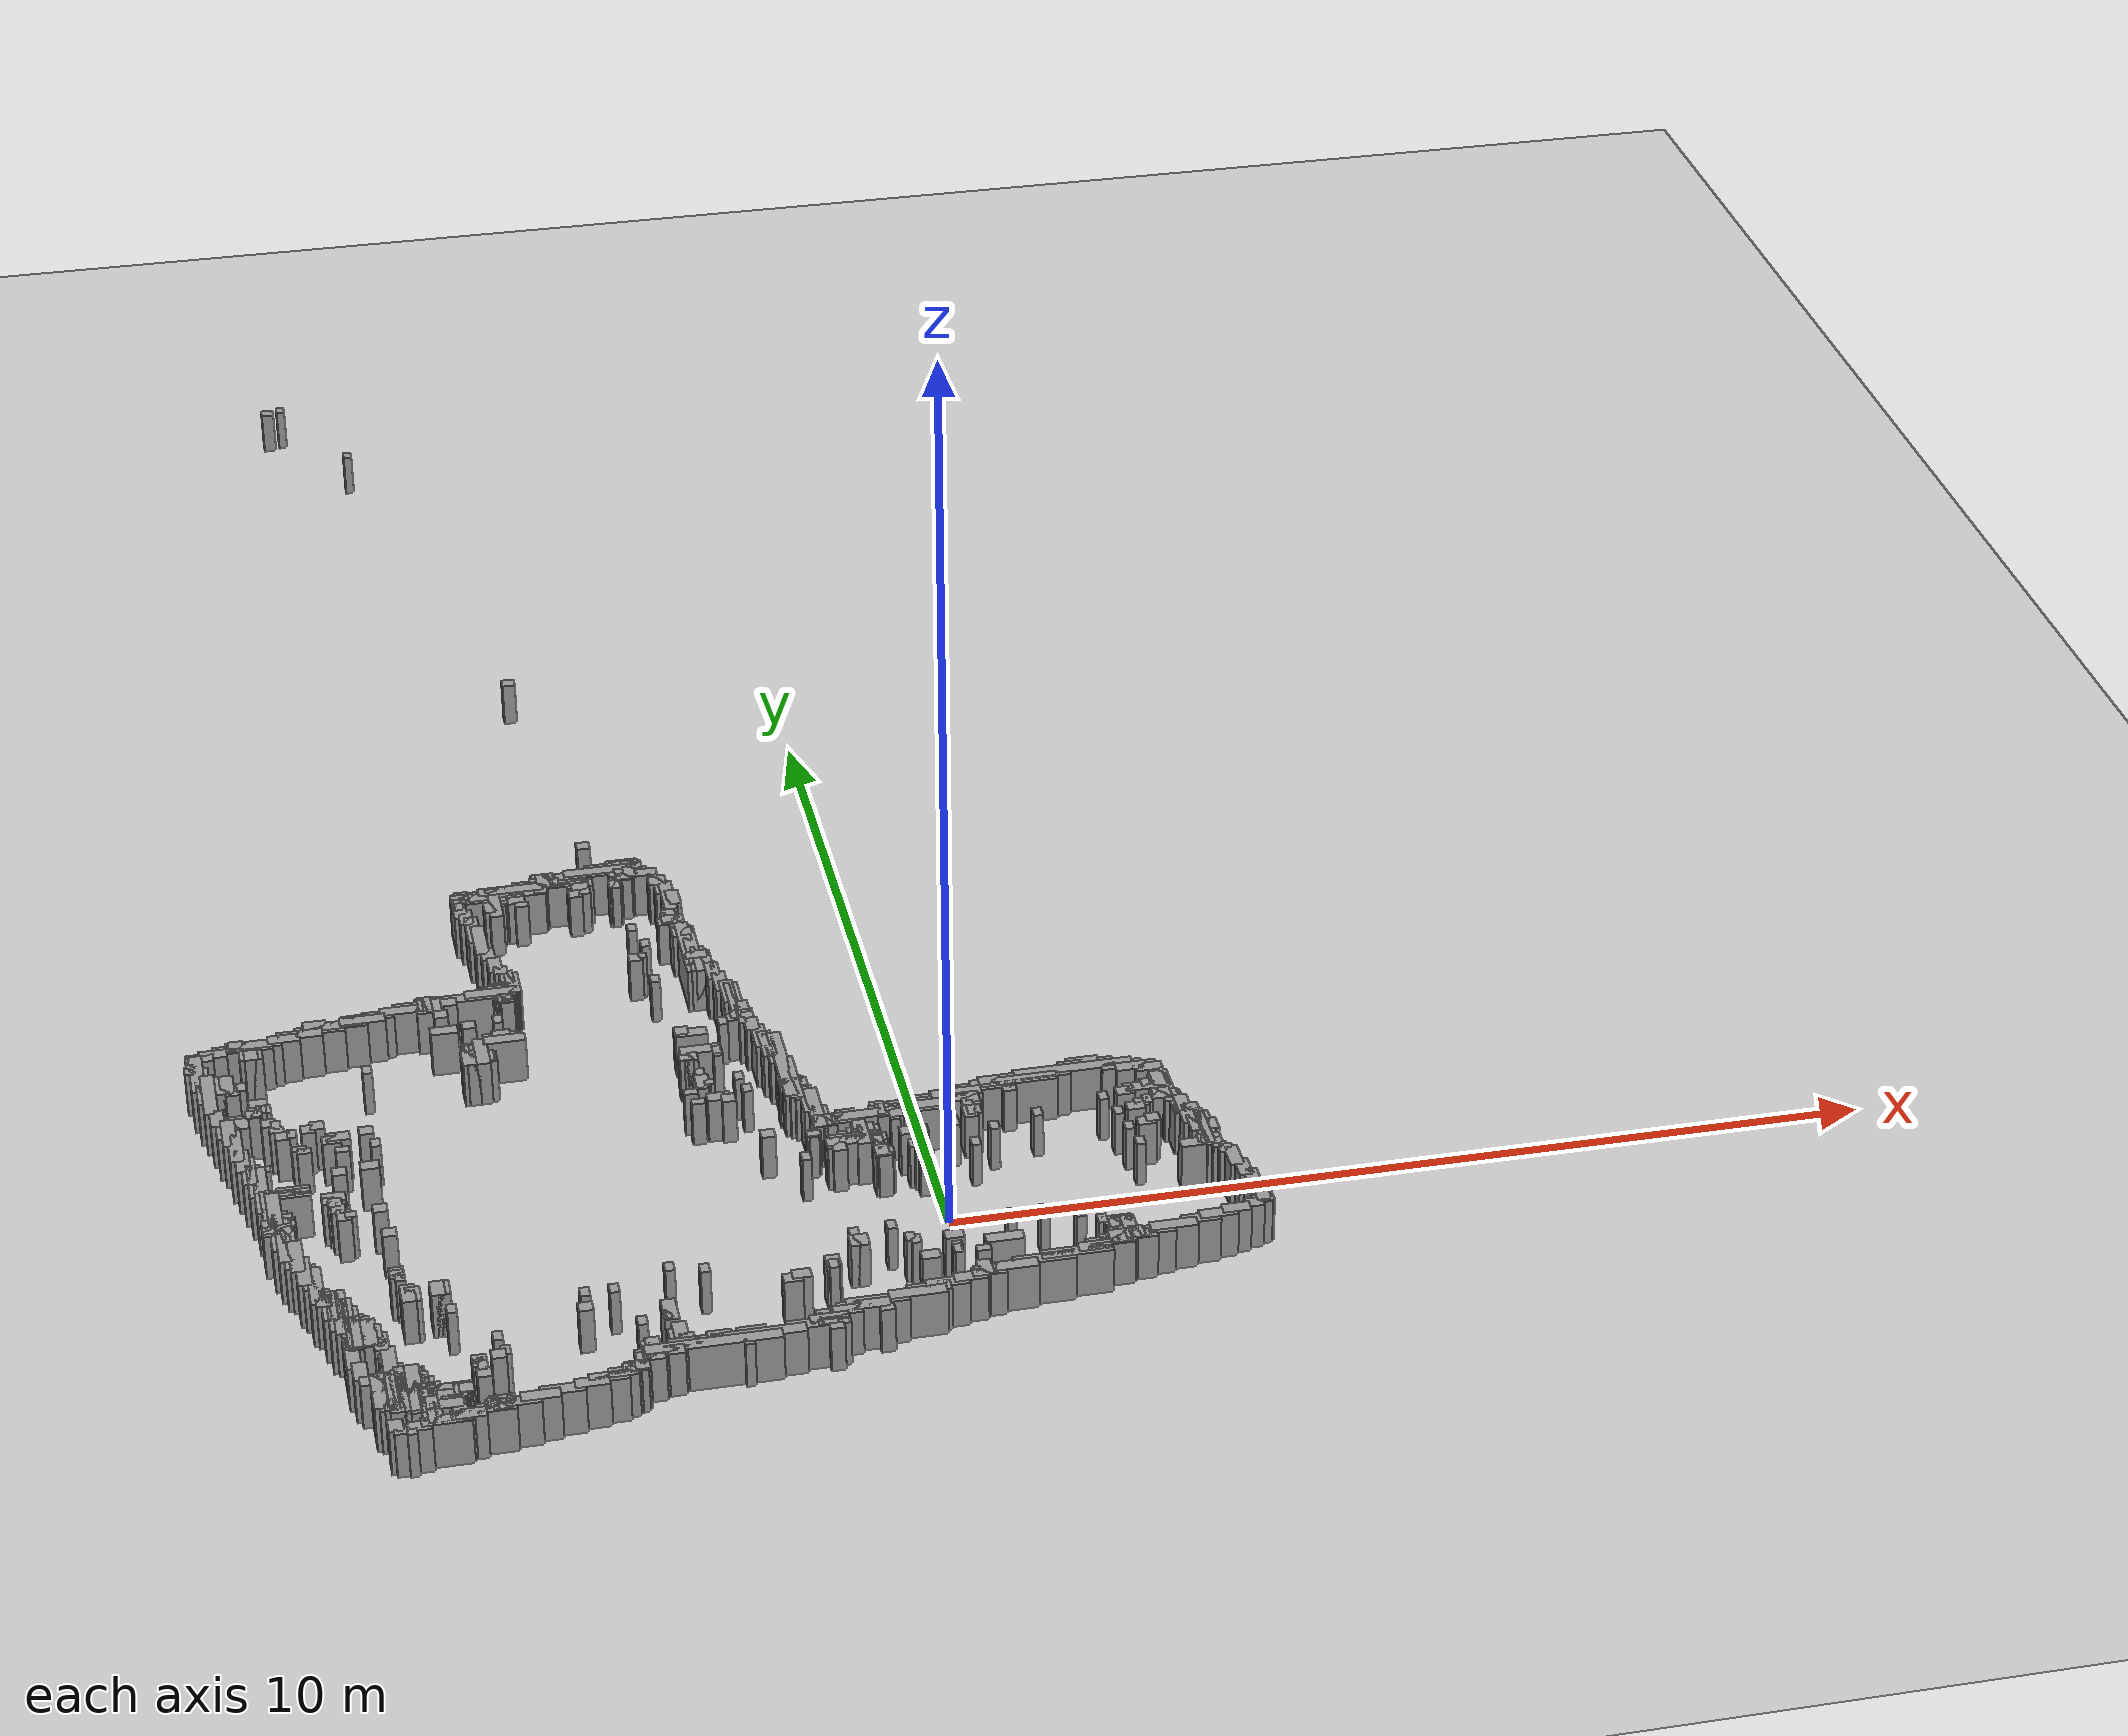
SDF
<sdf version="1.6">
  <world name="default">
    <include>
      <uri>model://sun</uri>
    </include>
    <include>
      <uri>model://ground_plane</uri>
    </include>
    <physics type="ode">
      <real_time_update_rate>1000.0</real_time_update_rate>
      <max_step_size>0.001</max_step_size>
      <real_time_factor>1</real_time_factor>
      <ode>
        <solver>
          <type>quick</type>
          <iters>150</iters>
          <precon_iters>0</precon_iters>
          <sor>1.400000</sor>
          <use_dynamic_moi_rescaling>1</use_dynamic_moi_rescaling>
        </solver>
        <constraints>
          <cfm>0.00001</cfm>
          <erp>0.2</erp>
          <contact_max_correcting_vel>2000.000000</contact_max_correcting_vel>
          <contact_surface_layer>0.01000</contact_surface_layer>
        </constraints>
      </ode>
    </physics>
    <scene>
      <ambient>0.4 0.4 0.4 1</ambient>
      <background>0.7 0.7 0.7 1</background>
      <shadows>true</shadows>
    </scene>
    <gui fullscreen="0">
      <camera name="user_camera">
        <pose>0.0 0.0 17.0 -1.5708 1.5708 0</pose>
        <view_controller>orbit</view_controller>
      </camera>
    </gui>
    <model name="obstacle">
      <static>1</static>
      <pose frame="">0 0 0 0 0 0</pose>
      <link name="obstacle">
        <collision name="obstacle_1">
          <pose>-5.2749979999999965 19.525002 0 0 0 0</pose>
          <geometry>
            <box>
              <size>0.1 0.15 1.0</size>
            </box>
          </geometry>
        </collision>
        <visual name="obstacle_1">
          <pose>-5.2749979999999965 19.525002 0 0 0 0</pose>
          <geometry>
            <box>
              <size>0.1 0.15 1.0</size>
            </box>
          </geometry>
          <material>
            <script>
              <uri>file://media/materials/scripts/gazebo.material</uri>
              <name>Gazebo/Grey</name>
            </script>
            <ambient>1 1 1 1</ambient>
          </material>
        </visual>
        <collision name="obstacle_3">
          <pose>-5.449997999999994 19.475002000000003 0 0 0 0</pose>
          <geometry>
            <box>
              <size>0.15000000000000002 0.15 1.0</size>
            </box>
          </geometry>
        </collision>
        <visual name="obstacle_3">
          <pose>-5.449997999999994 19.475002000000003 0 0 0 0</pose>
          <geometry>
            <box>
              <size>0.15000000000000002 0.15 1.0</size>
            </box>
          </geometry>
          <material>
            <script>
              <uri>file://media/materials/scripts/gazebo.material</uri>
              <name>Gazebo/Grey</name>
            </script>
            <ambient>1 1 1 1</ambient>
          </material>
        </visual>
        <collision name="obstacle_4">
          <pose>-4.5249979999999965 18.025002 0 0 0 0</pose>
          <geometry>
            <box>
              <size>0.1 0.15 1.0</size>
            </box>
          </geometry>
        </collision>
        <visual name="obstacle_4">
          <pose>-4.5249979999999965 18.025002 0 0 0 0</pose>
          <geometry>
            <box>
              <size>0.1 0.15 1.0</size>
            </box>
          </geometry>
          <material>
            <script>
              <uri>file://media/materials/scripts/gazebo.material</uri>
              <name>Gazebo/Grey</name>
            </script>
            <ambient>1 1 1 1</ambient>
          </material>
        </visual>
        <collision name="obstacle_5">
          <pose>-3.1999979999999937 11.525002 0 0 0 0</pose>
          <geometry>
            <box>
              <size>0.15000000000000002 0.15 1.0</size>
            </box>
          </geometry>
        </collision>
        <visual name="obstacle_5">
          <pose>-3.1999979999999937 11.525002 0 0 0 0</pose>
          <geometry>
            <box>
              <size>0.15000000000000002 0.15 1.0</size>
            </box>
          </geometry>
          <material>
            <script>
              <uri>file://media/materials/scripts/gazebo.material</uri>
              <name>Gazebo/Grey</name>
            </script>
            <ambient>1 1 1 1</ambient>
          </material>
        </visual>
        <collision name="obstacle_6">
          <pose>-2.8249979999999937 7.550002000000006 0 0 0 1.5708</pose>
          <geometry>
            <box>
              <size>0.15000000000000002 0.15 1.0</size>
            </box>
          </geometry>
        </collision>
        <visual name="obstacle_6">
          <pose>-2.8249979999999937 7.550002000000006 0 0 0 1.5708</pose>
          <geometry>
            <box>
              <size>0.15000000000000002 0.15 1.0</size>
            </box>
          </geometry>
          <material>
            <script>
              <uri>file://media/materials/scripts/gazebo.material</uri>
              <name>Gazebo/Grey</name>
            </script>
            <ambient>1 1 1 1</ambient>
          </material>
        </visual>
        <collision name="obstacle_7">
          <pose>-2.4749979999999994 6.925002000000006 0 0 0 1.5708</pose>
          <geometry>
            <box>
              <size>0.4 0.15 1.0</size>
            </box>
          </geometry>
        </collision>
        <visual name="obstacle_7">
          <pose>-2.4749979999999994 6.925002000000006 0 0 0 1.5708</pose>
          <geometry>
            <box>
              <size>0.4 0.15 1.0</size>
            </box>
          </geometry>
          <material>
            <script>
              <uri>file://media/materials/scripts/gazebo.material</uri>
              <name>Gazebo/Grey</name>
            </script>
            <ambient>1 1 1 1</ambient>
          </material>
        </visual>
        <collision name="obstacle_8">
          <pose>-2.424997999999995 6.925002000000006 0 0 0 1.5708</pose>
          <geometry>
            <box>
              <size>0.4 0.15 1.0</size>
            </box>
          </geometry>
        </collision>
        <visual name="obstacle_8">
          <pose>-2.424997999999995 6.925002000000006 0 0 0 1.5708</pose>
          <geometry>
            <box>
              <size>0.4 0.15 1.0</size>
            </box>
          </geometry>
          <material>
            <script>
              <uri>file://media/materials/scripts/gazebo.material</uri>
              <name>Gazebo/Grey</name>
            </script>
            <ambient>1 1 1 1</ambient>
          </material>
        </visual>
        <collision name="obstacle_9">
          <pose>-2.374997999999998 6.950002000000005 0 0 0 1.5708</pose>
          <geometry>
            <box>
              <size>0.35000000000000003 0.15 1.0</size>
            </box>
          </geometry>
        </collision>
        <visual name="obstacle_9">
          <pose>-2.374997999999998 6.950002000000005 0 0 0 1.5708</pose>
          <geometry>
            <box>
              <size>0.35000000000000003 0.15 1.0</size>
            </box>
          </geometry>
          <material>
            <script>
              <uri>file://media/materials/scripts/gazebo.material</uri>
              <name>Gazebo/Grey</name>
            </script>
            <ambient>1 1 1 1</ambient>
          </material>
        </visual>
        <collision name="obstacle_10">
          <pose>-2.3249979999999937 6.950002000000005 0 0 0 1.5708</pose>
          <geometry>
            <box>
              <size>0.35000000000000003 0.15 1.0</size>
            </box>
          </geometry>
        </collision>
        <visual name="obstacle_10">
          <pose>-2.3249979999999937 6.950002000000005 0 0 0 1.5708</pose>
          <geometry>
            <box>
              <size>0.35000000000000003 0.15 1.0</size>
            </box>
          </geometry>
          <material>
            <script>
              <uri>file://media/materials/scripts/gazebo.material</uri>
              <name>Gazebo/Grey</name>
            </script>
            <ambient>1 1 1 1</ambient>
          </material>
        </visual>
        <collision name="obstacle_11">
          <pose>-2.4499979999999937 7.075002000000005 0 0 0 0</pose>
          <geometry>
            <box>
              <size>0.35000000000000003 0.15 1.0</size>
            </box>
          </geometry>
        </collision>
        <visual name="obstacle_11">
          <pose>-2.4499979999999937 7.075002000000005 0 0 0 0</pose>
          <geometry>
            <box>
              <size>0.35000000000000003 0.15 1.0</size>
            </box>
          </geometry>
          <material>
            <script>
              <uri>file://media/materials/scripts/gazebo.material</uri>
              <name>Gazebo/Grey</name>
            </script>
            <ambient>1 1 1 1</ambient>
          </material>
        </visual>
        <collision name="obstacle_12">
          <pose>-3.424997999999995 6.825002000000005 0 0 0 1.5708</pose>
          <geometry>
            <box>
              <size>0.4 0.15 1.0</size>
            </box>
          </geometry>
        </collision>
        <visual name="obstacle_12">
          <pose>-3.424997999999995 6.825002000000005 0 0 0 1.5708</pose>
          <geometry>
            <box>
              <size>0.4 0.15 1.0</size>
            </box>
          </geometry>
          <material>
            <script>
              <uri>file://media/materials/scripts/gazebo.material</uri>
              <name>Gazebo/Grey</name>
            </script>
            <ambient>1 1 1 1</ambient>
          </material>
        </visual>
        <collision name="obstacle_13">
          <pose>-3.374997999999998 6.875002000000002 0 0 0 1.5708</pose>
          <geometry>
            <box>
              <size>0.30000000000000004 0.15 1.0</size>
            </box>
          </geometry>
        </collision>
        <visual name="obstacle_13">
          <pose>-3.374997999999998 6.875002000000002 0 0 0 1.5708</pose>
          <geometry>
            <box>
              <size>0.30000000000000004 0.15 1.0</size>
            </box>
          </geometry>
          <material>
            <script>
              <uri>file://media/materials/scripts/gazebo.material</uri>
              <name>Gazebo/Grey</name>
            </script>
            <ambient>1 1 1 1</ambient>
          </material>
        </visual>
        <collision name="obstacle_14">
          <pose>-3.3249979999999937 6.875002000000002 0 0 0 1.5708</pose>
          <geometry>
            <box>
              <size>0.30000000000000004 0.15 1.0</size>
            </box>
          </geometry>
        </collision>
        <visual name="obstacle_14">
          <pose>-3.3249979999999937 6.875002000000002 0 0 0 1.5708</pose>
          <geometry>
            <box>
              <size>0.30000000000000004 0.15 1.0</size>
            </box>
          </geometry>
          <material>
            <script>
              <uri>file://media/materials/scripts/gazebo.material</uri>
              <name>Gazebo/Grey</name>
            </script>
            <ambient>1 1 1 1</ambient>
          </material>
        </visual>
        <collision name="obstacle_15">
          <pose>-2.549997999999995 7.025002000000001 0 0 0 0</pose>
          <geometry>
            <box>
              <size>0.65 0.15 1.0</size>
            </box>
          </geometry>
        </collision>
        <visual name="obstacle_15">
          <pose>-2.549997999999995 7.025002000000001 0 0 0 0</pose>
          <geometry>
            <box>
              <size>0.65 0.15 1.0</size>
            </box>
          </geometry>
          <material>
            <script>
              <uri>file://media/materials/scripts/gazebo.material</uri>
              <name>Gazebo/Grey</name>
            </script>
            <ambient>1 1 1 1</ambient>
          </material>
        </visual>
        <collision name="obstacle_16">
          <pose>-3.2749979999999965 6.8500020000000035 0 0 0 1.5708</pose>
          <geometry>
            <box>
              <size>0.25 0.15 1.0</size>
            </box>
          </geometry>
        </collision>
        <visual name="obstacle_16">
          <pose>-3.2749979999999965 6.8500020000000035 0 0 0 1.5708</pose>
          <geometry>
            <box>
              <size>0.25 0.15 1.0</size>
            </box>
          </geometry>
          <material>
            <script>
              <uri>file://media/materials/scripts/gazebo.material</uri>
              <name>Gazebo/Grey</name>
            </script>
            <ambient>1 1 1 1</ambient>
          </material>
        </visual>
        <collision name="obstacle_17">
          <pose>-2.674997999999995 6.9750020000000035 0 0 0 0</pose>
          <geometry>
            <box>
              <size>0.9 0.15 1.0</size>
            </box>
          </geometry>
        </collision>
        <visual name="obstacle_17">
          <pose>-2.674997999999995 6.9750020000000035 0 0 0 0</pose>
          <geometry>
            <box>
              <size>0.9 0.15 1.0</size>
            </box>
          </geometry>
          <material>
            <script>
              <uri>file://media/materials/scripts/gazebo.material</uri>
              <name>Gazebo/Grey</name>
            </script>
            <ambient>1 1 1 1</ambient>
          </material>
        </visual>
        <collision name="obstacle_18">
          <pose>-2.7249979999999994 6.925002000000006 0 0 0 0</pose>
          <geometry>
            <box>
              <size>1.0 0.15 1.0</size>
            </box>
          </geometry>
        </collision>
        <visual name="obstacle_18">
          <pose>-2.7249979999999994 6.925002000000006 0 0 0 0</pose>
          <geometry>
            <box>
              <size>1.0 0.15 1.0</size>
            </box>
          </geometry>
          <material>
            <script>
              <uri>file://media/materials/scripts/gazebo.material</uri>
              <name>Gazebo/Grey</name>
            </script>
            <ambient>1 1 1 1</ambient>
          </material>
        </visual>
        <collision name="obstacle_19">
          <pose>-3.1999979999999937 6.875002000000002 0 0 0 0</pose>
          <geometry>
            <box>
              <size>0.65 0.15 1.0</size>
            </box>
          </geometry>
        </collision>
        <visual name="obstacle_19">
          <pose>-3.1999979999999937 6.875002000000002 0 0 0 0</pose>
          <geometry>
            <box>
              <size>0.65 0.15 1.0</size>
            </box>
          </geometry>
          <material>
            <script>
              <uri>file://media/materials/scripts/gazebo.material</uri>
              <name>Gazebo/Grey</name>
            </script>
            <ambient>1 1 1 1</ambient>
          </material>
        </visual>
        <collision name="obstacle_20">
          <pose>-2.3999979999999965 6.875002000000002 0 0 0 0</pose>
          <geometry>
            <box>
              <size>0.45 0.15 1.0</size>
            </box>
          </geometry>
        </collision>
        <visual name="obstacle_20">
          <pose>-2.3999979999999965 6.875002000000002 0 0 0 0</pose>
          <geometry>
            <box>
              <size>0.45 0.15 1.0</size>
            </box>
          </geometry>
          <material>
            <script>
              <uri>file://media/materials/scripts/gazebo.material</uri>
              <name>Gazebo/Grey</name>
            </script>
            <ambient>1 1 1 1</ambient>
          </material>
        </visual>
        <collision name="obstacle_21">
          <pose>-4.324997999999994 6.700002000000005 0 0 0 1.5708</pose>
          <geometry>
            <box>
              <size>0.25 0.15 1.0</size>
            </box>
          </geometry>
        </collision>
        <visual name="obstacle_21">
          <pose>-4.324997999999994 6.700002000000005 0 0 0 1.5708</pose>
          <geometry>
            <box>
              <size>0.25 0.15 1.0</size>
            </box>
          </geometry>
          <material>
            <script>
              <uri>file://media/materials/scripts/gazebo.material</uri>
              <name>Gazebo/Grey</name>
            </script>
            <ambient>1 1 1 1</ambient>
          </material>
        </visual>
        <collision name="obstacle_22">
          <pose>-4.0249979999999965 6.575002000000005 0 0 0 1.5708</pose>
          <geometry>
            <box>
              <size>0.5 0.15 1.0</size>
            </box>
          </geometry>
        </collision>
        <visual name="obstacle_22">
          <pose>-4.0249979999999965 6.575002000000005 0 0 0 1.5708</pose>
          <geometry>
            <box>
              <size>0.5 0.15 1.0</size>
            </box>
          </geometry>
          <material>
            <script>
              <uri>file://media/materials/scripts/gazebo.material</uri>
              <name>Gazebo/Grey</name>
            </script>
            <ambient>1 1 1 1</ambient>
          </material>
        </visual>
        <collision name="obstacle_23">
          <pose>-3.9749979999999994 6.525002000000001 0 0 0 1.5708</pose>
          <geometry>
            <box>
              <size>0.6000000000000001 0.15 1.0</size>
            </box>
          </geometry>
        </collision>
        <visual name="obstacle_23">
          <pose>-3.9749979999999994 6.525002000000001 0 0 0 1.5708</pose>
          <geometry>
            <box>
              <size>0.6000000000000001 0.15 1.0</size>
            </box>
          </geometry>
          <material>
            <script>
              <uri>file://media/materials/scripts/gazebo.material</uri>
              <name>Gazebo/Grey</name>
            </script>
            <ambient>1 1 1 1</ambient>
          </material>
        </visual>
        <collision name="obstacle_24">
          <pose>-3.924997999999995 6.625002000000002 0 0 0 1.5708</pose>
          <geometry>
            <box>
              <size>0.4 0.15 1.0</size>
            </box>
          </geometry>
        </collision>
        <visual name="obstacle_24">
          <pose>-3.924997999999995 6.625002000000002 0 0 0 1.5708</pose>
          <geometry>
            <box>
              <size>0.4 0.15 1.0</size>
            </box>
          </geometry>
          <material>
            <script>
              <uri>file://media/materials/scripts/gazebo.material</uri>
              <name>Gazebo/Grey</name>
            </script>
            <ambient>1 1 1 1</ambient>
          </material>
        </visual>
        <collision name="obstacle_25">
          <pose>-3.874997999999998 6.650002000000001 0 0 0 1.5708</pose>
          <geometry>
            <box>
              <size>0.35000000000000003 0.15 1.0</size>
            </box>
          </geometry>
        </collision>
        <visual name="obstacle_25">
          <pose>-3.874997999999998 6.650002000000001 0 0 0 1.5708</pose>
          <geometry>
            <box>
              <size>0.35000000000000003 0.15 1.0</size>
            </box>
          </geometry>
          <material>
            <script>
              <uri>file://media/materials/scripts/gazebo.material</uri>
              <name>Gazebo/Grey</name>
            </script>
            <ambient>1 1 1 1</ambient>
          </material>
        </visual>
        <collision name="obstacle_26">
          <pose>-3.299997999999995 6.825002000000005 0 0 0 0</pose>
          <geometry>
            <box>
              <size>0.8500000000000001 0.15 1.0</size>
            </box>
          </geometry>
        </collision>
        <visual name="obstacle_26">
          <pose>-3.299997999999995 6.825002000000005 0 0 0 0</pose>
          <geometry>
            <box>
              <size>0.8500000000000001 0.15 1.0</size>
            </box>
          </geometry>
          <material>
            <script>
              <uri>file://media/materials/scripts/gazebo.material</uri>
              <name>Gazebo/Grey</name>
            </script>
            <ambient>1 1 1 1</ambient>
          </material>
        </visual>
        <collision name="obstacle_27">
          <pose>-2.3249979999999937 6.825002000000005 0 0 0 0</pose>
          <geometry>
            <box>
              <size>0.5 0.15 1.0</size>
            </box>
          </geometry>
        </collision>
        <visual name="obstacle_27">
          <pose>-2.3249979999999937 6.825002000000005 0 0 0 0</pose>
          <geometry>
            <box>
              <size>0.5 0.15 1.0</size>
            </box>
          </geometry>
          <material>
            <script>
              <uri>file://media/materials/scripts/gazebo.material</uri>
              <name>Gazebo/Grey</name>
            </script>
            <ambient>1 1 1 1</ambient>
          </material>
        </visual>
        <collision name="obstacle_28">
          <pose>-4.374997999999998 6.525002000000001 0 0 0 1.5708</pose>
          <geometry>
            <box>
              <size>0.5 0.15 1.0</size>
            </box>
          </geometry>
        </collision>
        <visual name="obstacle_28">
          <pose>-4.374997999999998 6.525002000000001 0 0 0 1.5708</pose>
          <geometry>
            <box>
              <size>0.5 0.15 1.0</size>
            </box>
          </geometry>
          <material>
            <script>
              <uri>file://media/materials/scripts/gazebo.material</uri>
              <name>Gazebo/Grey</name>
            </script>
            <ambient>1 1 1 1</ambient>
          </material>
        </visual>
        <collision name="obstacle_29">
          <pose>-4.2749979999999965 6.675002000000006 0 0 0 1.5708</pose>
          <geometry>
            <box>
              <size>0.2 0.15 1.0</size>
            </box>
          </geometry>
        </collision>
        <visual name="obstacle_29">
          <pose>-4.2749979999999965 6.675002000000006 0 0 0 1.5708</pose>
          <geometry>
            <box>
              <size>0.2 0.15 1.0</size>
            </box>
          </geometry>
          <material>
            <script>
              <uri>file://media/materials/scripts/gazebo.material</uri>
              <name>Gazebo/Grey</name>
            </script>
            <ambient>1 1 1 1</ambient>
          </material>
        </visual>
        <collision name="obstacle_30">
          <pose>-3.499997999999998 6.775002000000001 0 0 0 0</pose>
          <geometry>
            <box>
              <size>1.25 0.15 1.0</size>
            </box>
          </geometry>
        </collision>
        <visual name="obstacle_30">
          <pose>-3.499997999999998 6.775002000000001 0 0 0 0</pose>
          <geometry>
            <box>
              <size>1.25 0.15 1.0</size>
            </box>
          </geometry>
          <material>
            <script>
              <uri>file://media/materials/scripts/gazebo.material</uri>
              <name>Gazebo/Grey</name>
            </script>
            <ambient>1 1 1 1</ambient>
          </material>
        </visual>
        <collision name="obstacle_31">
          <pose>-2.4749979999999994 6.775002000000001 0 0 0 0</pose>
          <geometry>
            <box>
              <size>0.2 0.15 1.0</size>
            </box>
          </geometry>
        </collision>
        <visual name="obstacle_31">
          <pose>-2.4749979999999994 6.775002000000001 0 0 0 0</pose>
          <geometry>
            <box>
              <size>0.2 0.15 1.0</size>
            </box>
          </geometry>
          <material>
            <script>
              <uri>file://media/materials/scripts/gazebo.material</uri>
              <name>Gazebo/Grey</name>
            </script>
            <ambient>1 1 1 1</ambient>
          </material>
        </visual>
        <collision name="obstacle_32">
          <pose>-2.124997999999998 6.775002000000001 0 0 0 0</pose>
          <geometry>
            <box>
              <size>0.1 0.15 1.0</size>
            </box>
          </geometry>
        </collision>
        <visual name="obstacle_32">
          <pose>-2.124997999999998 6.775002000000001 0 0 0 0</pose>
          <geometry>
            <box>
              <size>0.1 0.15 1.0</size>
            </box>
          </geometry>
          <material>
            <script>
              <uri>file://media/materials/scripts/gazebo.material</uri>
              <name>Gazebo/Grey</name>
            </script>
            <ambient>1 1 1 1</ambient>
          </material>
        </visual>
        <collision name="obstacle_33">
          <pose>-3.8999979999999965 6.7250020000000035 0 0 0 0</pose>
          <geometry>
            <box>
              <size>1.05 0.15 1.0</size>
            </box>
          </geometry>
        </collision>
        <visual name="obstacle_33">
          <pose>-3.8999979999999965 6.7250020000000035 0 0 0 0</pose>
          <geometry>
            <box>
              <size>1.05 0.15 1.0</size>
            </box>
          </geometry>
          <material>
            <script>
              <uri>file://media/materials/scripts/gazebo.material</uri>
              <name>Gazebo/Grey</name>
            </script>
            <ambient>1 1 1 1</ambient>
          </material>
        </visual>
        <collision name="obstacle_34">
          <pose>-2.9749979999999994 6.7250020000000035 0 0 0 0</pose>
          <geometry>
            <box>
              <size>0.30000000000000004 0.15 1.0</size>
            </box>
          </geometry>
        </collision>
        <visual name="obstacle_34">
          <pose>-2.9749979999999994 6.7250020000000035 0 0 0 0</pose>
          <geometry>
            <box>
              <size>0.30000000000000004 0.15 1.0</size>
            </box>
          </geometry>
          <material>
            <script>
              <uri>file://media/materials/scripts/gazebo.material</uri>
              <name>Gazebo/Grey</name>
            </script>
            <ambient>1 1 1 1</ambient>
          </material>
        </visual>
        <collision name="obstacle_35">
          <pose>-2.5749979999999937 6.650002000000001 0 0 0 1.5708</pose>
          <geometry>
            <box>
              <size>0.15000000000000002 0.15 1.0</size>
            </box>
          </geometry>
        </collision>
        <visual name="obstacle_35">
          <pose>-2.5749979999999937 6.650002000000001 0 0 0 1.5708</pose>
          <geometry>
            <box>
              <size>0.15000000000000002 0.15 1.0</size>
            </box>
          </geometry>
          <material>
            <script>
              <uri>file://media/materials/scripts/gazebo.material</uri>
              <name>Gazebo/Grey</name>
            </script>
            <ambient>1 1 1 1</ambient>
          </material>
        </visual>
        <collision name="obstacle_36">
          <pose>-2.124997999999998 6.625002000000002 0 0 0 1.5708</pose>
          <geometry>
            <box>
              <size>0.2 0.15 1.0</size>
            </box>
          </geometry>
        </collision>
        <visual name="obstacle_36">
          <pose>-2.124997999999998 6.625002000000002 0 0 0 1.5708</pose>
          <geometry>
            <box>
              <size>0.2 0.15 1.0</size>
            </box>
          </geometry>
          <material>
            <script>
              <uri>file://media/materials/scripts/gazebo.material</uri>
              <name>Gazebo/Grey</name>
            </script>
            <ambient>1 1 1 1</ambient>
          </material>
        </visual>
        <collision name="obstacle_37">
          <pose>-2.0749979999999937 6.525002000000001 0 0 0 1.5708</pose>
          <geometry>
            <box>
              <size>0.4 0.15 1.0</size>
            </box>
          </geometry>
        </collision>
        <visual name="obstacle_37">
          <pose>-2.0749979999999937 6.525002000000001 0 0 0 1.5708</pose>
          <geometry>
            <box>
              <size>0.4 0.15 1.0</size>
            </box>
          </geometry>
          <material>
            <script>
              <uri>file://media/materials/scripts/gazebo.material</uri>
              <name>Gazebo/Grey</name>
            </script>
            <ambient>1 1 1 1</ambient>
          </material>
        </visual>
        <collision name="obstacle_38">
          <pose>-3.8999979999999965 6.675002000000006 0 0 0 0</pose>
          <geometry>
            <box>
              <size>1.05 0.15 1.0</size>
            </box>
          </geometry>
        </collision>
        <visual name="obstacle_38">
          <pose>-3.8999979999999965 6.675002000000006 0 0 0 0</pose>
          <geometry>
            <box>
              <size>1.05 0.15 1.0</size>
            </box>
          </geometry>
          <material>
            <script>
              <uri>file://media/materials/scripts/gazebo.material</uri>
              <name>Gazebo/Grey</name>
            </script>
            <ambient>1 1 1 1</ambient>
          </material>
        </visual>
        <collision name="obstacle_39">
          <pose>-2.9749979999999994 6.675002000000006 0 0 0 0</pose>
          <geometry>
            <box>
              <size>0.2 0.15 1.0</size>
            </box>
          </geometry>
        </collision>
        <visual name="obstacle_39">
          <pose>-2.9749979999999994 6.675002000000006 0 0 0 0</pose>
          <geometry>
            <box>
              <size>0.2 0.15 1.0</size>
            </box>
          </geometry>
          <material>
            <script>
              <uri>file://media/materials/scripts/gazebo.material</uri>
              <name>Gazebo/Grey</name>
            </script>
            <ambient>1 1 1 1</ambient>
          </material>
        </visual>
        <collision name="obstacle_40">
          <pose>-4.0249979999999965 6.625002000000002 0 0 0 0</pose>
          <geometry>
            <box>
              <size>0.8 0.15 1.0</size>
            </box>
          </geometry>
        </collision>
        <visual name="obstacle_40">
          <pose>-4.0249979999999965 6.625002000000002 0 0 0 0</pose>
          <geometry>
            <box>
              <size>0.8 0.15 1.0</size>
            </box>
          </geometry>
          <material>
            <script>
              <uri>file://media/materials/scripts/gazebo.material</uri>
              <name>Gazebo/Grey</name>
            </script>
            <ambient>1 1 1 1</ambient>
          </material>
        </visual>
        <collision name="obstacle_41">
          <pose>-2.9749979999999994 6.625002000000002 0 0 0 0</pose>
          <geometry>
            <box>
              <size>0.2 0.15 1.0</size>
            </box>
          </geometry>
        </collision>
        <visual name="obstacle_41">
          <pose>-2.9749979999999994 6.625002000000002 0 0 0 0</pose>
          <geometry>
            <box>
              <size>0.2 0.15 1.0</size>
            </box>
          </geometry>
          <material>
            <script>
              <uri>file://media/materials/scripts/gazebo.material</uri>
              <name>Gazebo/Grey</name>
            </script>
            <ambient>1 1 1 1</ambient>
          </material>
        </visual>
        <collision name="obstacle_42">
          <pose>-2.5749979999999937 6.625002000000002 0 0 0 0</pose>
          <geometry>
            <box>
              <size>0.1 0.15 1.0</size>
            </box>
          </geometry>
        </collision>
        <visual name="obstacle_42">
          <pose>-2.5749979999999937 6.625002000000002 0 0 0 0</pose>
          <geometry>
            <box>
              <size>0.1 0.15 1.0</size>
            </box>
          </geometry>
          <material>
            <script>
              <uri>file://media/materials/scripts/gazebo.material</uri>
              <name>Gazebo/Grey</name>
            </script>
            <ambient>1 1 1 1</ambient>
          </material>
        </visual>
        <collision name="obstacle_43">
          <pose>-4.374997999999998 6.575002000000005 0 0 0 0</pose>
          <geometry>
            <box>
              <size>0.1 0.15 1.0</size>
            </box>
          </geometry>
        </collision>
        <visual name="obstacle_43">
          <pose>-4.374997999999998 6.575002000000005 0 0 0 0</pose>
          <geometry>
            <box>
              <size>0.1 0.15 1.0</size>
            </box>
          </geometry>
          <material>
            <script>
              <uri>file://media/materials/scripts/gazebo.material</uri>
              <name>Gazebo/Grey</name>
            </script>
            <ambient>1 1 1 1</ambient>
          </material>
        </visual>
        <collision name="obstacle_44">
          <pose>-3.7249979999999994 6.575002000000005 0 0 0 0</pose>
          <geometry>
            <box>
              <size>0.2 0.15 1.0</size>
            </box>
          </geometry>
        </collision>
        <visual name="obstacle_44">
          <pose>-3.7249979999999994 6.575002000000005 0 0 0 0</pose>
          <geometry>
            <box>
              <size>0.2 0.15 1.0</size>
            </box>
          </geometry>
          <material>
            <script>
              <uri>file://media/materials/scripts/gazebo.material</uri>
              <name>Gazebo/Grey</name>
            </script>
            <ambient>1 1 1 1</ambient>
          </material>
        </visual>
        <collision name="obstacle_45">
          <pose>-2.9749979999999994 6.575002000000005 0 0 0 0</pose>
          <geometry>
            <box>
              <size>0.2 0.15 1.0</size>
            </box>
          </geometry>
        </collision>
        <visual name="obstacle_45">
          <pose>-2.9749979999999994 6.575002000000005 0 0 0 0</pose>
          <geometry>
            <box>
              <size>0.2 0.15 1.0</size>
            </box>
          </geometry>
          <material>
            <script>
              <uri>file://media/materials/scripts/gazebo.material</uri>
              <name>Gazebo/Grey</name>
            </script>
            <ambient>1 1 1 1</ambient>
          </material>
        </visual>
        <collision name="obstacle_46">
          <pose>-2.0249979999999965 6.275002000000001 0 0 0 1.5708</pose>
          <geometry>
            <box>
              <size>0.6000000000000001 0.15 1.0</size>
            </box>
          </geometry>
        </collision>
        <visual name="obstacle_46">
          <pose>-2.0249979999999965 6.275002000000001 0 0 0 1.5708</pose>
          <geometry>
            <box>
              <size>0.6000000000000001 0.15 1.0</size>
            </box>
          </geometry>
          <material>
            <script>
              <uri>file://media/materials/scripts/gazebo.material</uri>
              <name>Gazebo/Grey</name>
            </script>
            <ambient>1 1 1 1</ambient>
          </material>
        </visual>
        <collision name="obstacle_47">
          <pose>-4.374997999999998 6.525002000000001 0 0 0 0</pose>
          <geometry>
            <box>
              <size>0.1 0.15 1.0</size>
            </box>
          </geometry>
        </collision>
        <visual name="obstacle_47">
          <pose>-4.374997999999998 6.525002000000001 0 0 0 0</pose>
          <geometry>
            <box>
              <size>0.1 0.15 1.0</size>
            </box>
          </geometry>
          <material>
            <script>
              <uri>file://media/materials/scripts/gazebo.material</uri>
              <name>Gazebo/Grey</name>
            </script>
            <ambient>1 1 1 1</ambient>
          </material>
        </visual>
        <collision name="obstacle_48">
          <pose>-3.7249979999999994 6.525002000000001 0 0 0 0</pose>
          <geometry>
            <box>
              <size>0.2 0.15 1.0</size>
            </box>
          </geometry>
        </collision>
        <visual name="obstacle_48">
          <pose>-3.7249979999999994 6.525002000000001 0 0 0 0</pose>
          <geometry>
            <box>
              <size>0.2 0.15 1.0</size>
            </box>
          </geometry>
          <material>
            <script>
              <uri>file://media/materials/scripts/gazebo.material</uri>
              <name>Gazebo/Grey</name>
            </script>
            <ambient>1 1 1 1</ambient>
          </material>
        </visual>
        <collision name="obstacle_49">
          <pose>-3.049997999999995 6.525002000000001 0 0 0 0</pose>
          <geometry>
            <box>
              <size>0.15000000000000002 0.15 1.0</size>
            </box>
          </geometry>
        </collision>
        <visual name="obstacle_49">
          <pose>-3.049997999999995 6.525002000000001 0 0 0 0</pose>
          <geometry>
            <box>
              <size>0.15000000000000002 0.15 1.0</size>
            </box>
          </geometry>
          <material>
            <script>
              <uri>file://media/materials/scripts/gazebo.material</uri>
              <name>Gazebo/Grey</name>
            </script>
            <ambient>1 1 1 1</ambient>
          </material>
        </visual>
        <collision name="obstacle_50">
          <pose>-3.674997999999995 6.425002000000006 0 0 0 1.5708</pose>
          <geometry>
            <box>
              <size>0.1 0.15 1.0</size>
            </box>
          </geometry>
        </collision>
        <visual name="obstacle_50">
          <pose>-3.674997999999995 6.425002000000006 0 0 0 1.5708</pose>
          <geometry>
            <box>
              <size>0.1 0.15 1.0</size>
            </box>
          </geometry>
          <material>
            <script>
              <uri>file://media/materials/scripts/gazebo.material</uri>
              <name>Gazebo/Grey</name>
            </script>
            <ambient>1 1 1 1</ambient>
          </material>
        </visual>
        <collision name="obstacle_51">
          <pose>-4.324997999999994 6.275002000000001 0 0 0 1.5708</pose>
          <geometry>
            <box>
              <size>0.30000000000000004 0.15 1.0</size>
            </box>
          </geometry>
        </collision>
        <visual name="obstacle_51">
          <pose>-4.324997999999994 6.275002000000001 0 0 0 1.5708</pose>
          <geometry>
            <box>
              <size>0.30000000000000004 0.15 1.0</size>
            </box>
          </geometry>
          <material>
            <script>
              <uri>file://media/materials/scripts/gazebo.material</uri>
              <name>Gazebo/Grey</name>
            </script>
            <ambient>1 1 1 1</ambient>
          </material>
        </visual>
        <collision name="obstacle_54">
          <pose>-1.9749979999999994 6.2250020000000035 0 0 0 1.5708</pose>
          <geometry>
            <box>
              <size>0.30000000000000004 0.15 1.0</size>
            </box>
          </geometry>
        </collision>
        <visual name="obstacle_54">
          <pose>-1.9749979999999994 6.2250020000000035 0 0 0 1.5708</pose>
          <geometry>
            <box>
              <size>0.30000000000000004 0.15 1.0</size>
            </box>
          </geometry>
          <material>
            <script>
              <uri>file://media/materials/scripts/gazebo.material</uri>
              <name>Gazebo/Grey</name>
            </script>
            <ambient>1 1 1 1</ambient>
          </material>
        </visual>
        <collision name="obstacle_56">
          <pose>-4.2749979999999965 6.000002000000002 0 0 0 1.5708</pose>
          <geometry>
            <box>
              <size>0.55 0.15 1.0</size>
            </box>
          </geometry>
        </collision>
        <visual name="obstacle_56">
          <pose>-4.2749979999999965 6.000002000000002 0 0 0 1.5708</pose>
          <geometry>
            <box>
              <size>0.55 0.15 1.0</size>
            </box>
          </geometry>
          <material>
            <script>
              <uri>file://media/materials/scripts/gazebo.material</uri>
              <name>Gazebo/Grey</name>
            </script>
            <ambient>1 1 1 1</ambient>
          </material>
        </visual>
        <collision name="obstacle_57">
          <pose>-4.224997999999999 5.775002000000001 0 0 0 1.5708</pose>
          <geometry>
            <box>
              <size>0.6000000000000001 0.15 1.0</size>
            </box>
          </geometry>
        </collision>
        <visual name="obstacle_57">
          <pose>-4.224997999999999 5.775002000000001 0 0 0 1.5708</pose>
          <geometry>
            <box>
              <size>0.6000000000000001 0.15 1.0</size>
            </box>
          </geometry>
          <material>
            <script>
              <uri>file://media/materials/scripts/gazebo.material</uri>
              <name>Gazebo/Grey</name>
            </script>
            <ambient>1 1 1 1</ambient>
          </material>
        </visual>
        <collision name="obstacle_58">
          <pose>-2.0749979999999937 5.825002000000005 0 0 0 1.5708</pose>
          <geometry>
            <box>
              <size>0.30000000000000004 0.15 1.0</size>
            </box>
          </geometry>
        </collision>
        <visual name="obstacle_58">
          <pose>-2.0749979999999937 5.825002000000005 0 0 0 1.5708</pose>
          <geometry>
            <box>
              <size>0.30000000000000004 0.15 1.0</size>
            </box>
          </geometry>
          <material>
            <script>
              <uri>file://media/materials/scripts/gazebo.material</uri>
              <name>Gazebo/Grey</name>
            </script>
            <ambient>1 1 1 1</ambient>
          </material>
        </visual>
        <collision name="obstacle_59">
          <pose>-2.0749979999999937 5.825002000000005 0 0 0 0</pose>
          <geometry>
            <box>
              <size>0.2 0.15 1.0</size>
            </box>
          </geometry>
        </collision>
        <visual name="obstacle_59">
          <pose>-2.0749979999999937 5.825002000000005 0 0 0 0</pose>
          <geometry>
            <box>
              <size>0.2 0.15 1.0</size>
            </box>
          </geometry>
          <material>
            <script>
              <uri>file://media/materials/scripts/gazebo.material</uri>
              <name>Gazebo/Grey</name>
            </script>
            <ambient>1 1 1 1</ambient>
          </material>
        </visual>
        <collision name="obstacle_60">
          <pose>-2.049997999999995 5.775002000000001 0 0 0 0</pose>
          <geometry>
            <box>
              <size>0.25 0.15 1.0</size>
            </box>
          </geometry>
        </collision>
        <visual name="obstacle_60">
          <pose>-2.049997999999995 5.775002000000001 0 0 0 0</pose>
          <geometry>
            <box>
              <size>0.25 0.15 1.0</size>
            </box>
          </geometry>
          <material>
            <script>
              <uri>file://media/materials/scripts/gazebo.material</uri>
              <name>Gazebo/Grey</name>
            </script>
            <ambient>1 1 1 1</ambient>
          </material>
        </visual>
        <collision name="obstacle_61">
          <pose>-2.0749979999999937 5.7250020000000035 0 0 0 0</pose>
          <geometry>
            <box>
              <size>0.30000000000000004 0.15 1.0</size>
            </box>
          </geometry>
        </collision>
        <visual name="obstacle_61">
          <pose>-2.0749979999999937 5.7250020000000035 0 0 0 0</pose>
          <geometry>
            <box>
              <size>0.30000000000000004 0.15 1.0</size>
            </box>
          </geometry>
          <material>
            <script>
              <uri>file://media/materials/scripts/gazebo.material</uri>
              <name>Gazebo/Grey</name>
            </script>
            <ambient>1 1 1 1</ambient>
          </material>
        </visual>
        <collision name="obstacle_62">
          <pose>-2.5249979999999965 5.675002000000006 0 0 0 0</pose>
          <geometry>
            <box>
              <size>0.1 0.15 1.0</size>
            </box>
          </geometry>
        </collision>
        <visual name="obstacle_62">
          <pose>-2.5249979999999965 5.675002000000006 0 0 0 0</pose>
          <geometry>
            <box>
              <size>0.1 0.15 1.0</size>
            </box>
          </geometry>
          <material>
            <script>
              <uri>file://media/materials/scripts/gazebo.material</uri>
              <name>Gazebo/Grey</name>
            </script>
            <ambient>1 1 1 1</ambient>
          </material>
        </visual>
        <collision name="obstacle_63">
          <pose>-2.0249979999999965 5.525002000000001 0 0 0 1.5708</pose>
          <geometry>
            <box>
              <size>0.30000000000000004 0.15 1.0</size>
            </box>
          </geometry>
        </collision>
        <visual name="obstacle_63">
          <pose>-2.0249979999999965 5.525002000000001 0 0 0 1.5708</pose>
          <geometry>
            <box>
              <size>0.30000000000000004 0.15 1.0</size>
            </box>
          </geometry>
          <material>
            <script>
              <uri>file://media/materials/scripts/gazebo.material</uri>
              <name>Gazebo/Grey</name>
            </script>
            <ambient>1 1 1 1</ambient>
          </material>
        </visual>
        <collision name="obstacle_64">
          <pose>-1.9749979999999994 5.150002000000001 0 0 0 1.5708</pose>
          <geometry>
            <box>
              <size>1.05 0.15 1.0</size>
            </box>
          </geometry>
        </collision>
        <visual name="obstacle_64">
          <pose>-1.9749979999999994 5.150002000000001 0 0 0 1.5708</pose>
          <geometry>
            <box>
              <size>1.05 0.15 1.0</size>
            </box>
          </geometry>
          <material>
            <script>
              <uri>file://media/materials/scripts/gazebo.material</uri>
              <name>Gazebo/Grey</name>
            </script>
            <ambient>1 1 1 1</ambient>
          </material>
        </visual>
        <collision name="obstacle_65">
          <pose>-4.174997999999995 5.450002000000005 0 0 0 1.5708</pose>
          <geometry>
            <box>
              <size>0.25 0.15 1.0</size>
            </box>
          </geometry>
        </collision>
        <visual name="obstacle_65">
          <pose>-4.174997999999995 5.450002000000005 0 0 0 1.5708</pose>
          <geometry>
            <box>
              <size>0.25 0.15 1.0</size>
            </box>
          </geometry>
          <material>
            <script>
              <uri>file://media/materials/scripts/gazebo.material</uri>
              <name>Gazebo/Grey</name>
            </script>
            <ambient>1 1 1 1</ambient>
          </material>
        </visual>
        <collision name="obstacle_66">
          <pose>-1.924997999999995 5.1000020000000035 0 0 0 1.5708</pose>
          <geometry>
            <box>
              <size>0.9500000000000001 0.15 1.0</size>
            </box>
          </geometry>
        </collision>
        <visual name="obstacle_66">
          <pose>-1.924997999999995 5.1000020000000035 0 0 0 1.5708</pose>
          <geometry>
            <box>
              <size>0.9500000000000001 0.15 1.0</size>
            </box>
          </geometry>
          <material>
            <script>
              <uri>file://media/materials/scripts/gazebo.material</uri>
              <name>Gazebo/Grey</name>
            </script>
            <ambient>1 1 1 1</ambient>
          </material>
        </visual>
        <collision name="obstacle_67">
          <pose>-1.9749979999999994 5.525002000000001 0 0 0 0</pose>
          <geometry>
            <box>
              <size>0.2 0.15 1.0</size>
            </box>
          </geometry>
        </collision>
        <visual name="obstacle_67">
          <pose>-1.9749979999999994 5.525002000000001 0 0 0 0</pose>
          <geometry>
            <box>
              <size>0.2 0.15 1.0</size>
            </box>
          </geometry>
          <material>
            <script>
              <uri>file://media/materials/scripts/gazebo.material</uri>
              <name>Gazebo/Grey</name>
            </script>
            <ambient>1 1 1 1</ambient>
          </material>
        </visual>
        <collision name="obstacle_68">
          <pose>-1.9749979999999994 5.4750020000000035 0 0 0 0</pose>
          <geometry>
            <box>
              <size>0.2 0.15 1.0</size>
            </box>
          </geometry>
        </collision>
        <visual name="obstacle_68">
          <pose>-1.9749979999999994 5.4750020000000035 0 0 0 0</pose>
          <geometry>
            <box>
              <size>0.2 0.15 1.0</size>
            </box>
          </geometry>
          <material>
            <script>
              <uri>file://media/materials/scripts/gazebo.material</uri>
              <name>Gazebo/Grey</name>
            </script>
            <ambient>1 1 1 1</ambient>
          </material>
        </visual>
        <collision name="obstacle_69">
          <pose>-4.124997999999998 5.2250020000000035 0 0 0 1.5708</pose>
          <geometry>
            <box>
              <size>0.30000000000000004 0.15 1.0</size>
            </box>
          </geometry>
        </collision>
        <visual name="obstacle_69">
          <pose>-4.124997999999998 5.2250020000000035 0 0 0 1.5708</pose>
          <geometry>
            <box>
              <size>0.30000000000000004 0.15 1.0</size>
            </box>
          </geometry>
          <material>
            <script>
              <uri>file://media/materials/scripts/gazebo.material</uri>
              <name>Gazebo/Grey</name>
            </script>
            <ambient>1 1 1 1</ambient>
          </material>
        </visual>
        <collision name="obstacle_70">
          <pose>-2.424997999999995 5.325002000000005 0 0 0 0</pose>
          <geometry>
            <box>
              <size>0.1 0.15 1.0</size>
            </box>
          </geometry>
        </collision>
        <visual name="obstacle_70">
          <pose>-2.424997999999995 5.325002000000005 0 0 0 0</pose>
          <geometry>
            <box>
              <size>0.1 0.15 1.0</size>
            </box>
          </geometry>
          <material>
            <script>
              <uri>file://media/materials/scripts/gazebo.material</uri>
              <name>Gazebo/Grey</name>
            </script>
            <ambient>1 1 1 1</ambient>
          </material>
        </visual>
        <collision name="obstacle_72">
          <pose>-4.074997999999994 5.1000020000000035 0 0 0 1.5708</pose>
          <geometry>
            <box>
              <size>0.15000000000000002 0.15 1.0</size>
            </box>
          </geometry>
        </collision>
        <visual name="obstacle_72">
          <pose>-4.074997999999994 5.1000020000000035 0 0 0 1.5708</pose>
          <geometry>
            <box>
              <size>0.15000000000000002 0.15 1.0</size>
            </box>
          </geometry>
          <material>
            <script>
              <uri>file://media/materials/scripts/gazebo.material</uri>
              <name>Gazebo/Grey</name>
            </script>
            <ambient>1 1 1 1</ambient>
          </material>
        </visual>
        <collision name="obstacle_73">
          <pose>-2.5749979999999937 5.050002000000006 0 0 0 1.5708</pose>
          <geometry>
            <box>
              <size>0.15000000000000002 0.15 1.0</size>
            </box>
          </geometry>
        </collision>
        <visual name="obstacle_73">
          <pose>-2.5749979999999937 5.050002000000006 0 0 0 1.5708</pose>
          <geometry>
            <box>
              <size>0.15000000000000002 0.15 1.0</size>
            </box>
          </geometry>
          <material>
            <script>
              <uri>file://media/materials/scripts/gazebo.material</uri>
              <name>Gazebo/Grey</name>
            </script>
            <ambient>1 1 1 1</ambient>
          </material>
        </visual>
        <collision name="obstacle_74">
          <pose>-2.5249979999999965 5.075002000000005 0 0 0 1.5708</pose>
          <geometry>
            <box>
              <size>0.1 0.15 1.0</size>
            </box>
          </geometry>
        </collision>
        <visual name="obstacle_74">
          <pose>-2.5249979999999965 5.075002000000005 0 0 0 1.5708</pose>
          <geometry>
            <box>
              <size>0.1 0.15 1.0</size>
            </box>
          </geometry>
          <material>
            <script>
              <uri>file://media/materials/scripts/gazebo.material</uri>
              <name>Gazebo/Grey</name>
            </script>
            <ambient>1 1 1 1</ambient>
          </material>
        </visual>
        <collision name="obstacle_75">
          <pose>-1.874997999999998 4.875002000000002 0 0 0 1.5708</pose>
          <geometry>
            <box>
              <size>0.5 0.15 1.0</size>
            </box>
          </geometry>
        </collision>
        <visual name="obstacle_75">
          <pose>-1.874997999999998 4.875002000000002 0 0 0 1.5708</pose>
          <geometry>
            <box>
              <size>0.5 0.15 1.0</size>
            </box>
          </geometry>
          <material>
            <script>
              <uri>file://media/materials/scripts/gazebo.material</uri>
              <name>Gazebo/Grey</name>
            </script>
            <ambient>1 1 1 1</ambient>
          </material>
        </visual>
        <collision name="obstacle_76">
          <pose>-4.0249979999999965 4.825002000000005 0 0 0 1.5708</pose>
          <geometry>
            <box>
              <size>0.5 0.15 1.0</size>
            </box>
          </geometry>
        </collision>
        <visual name="obstacle_76">
          <pose>-4.0249979999999965 4.825002000000005 0 0 0 1.5708</pose>
          <geometry>
            <box>
              <size>0.5 0.15 1.0</size>
            </box>
          </geometry>
          <material>
            <script>
              <uri>file://media/materials/scripts/gazebo.material</uri>
              <name>Gazebo/Grey</name>
            </script>
            <ambient>1 1 1 1</ambient>
          </material>
        </visual>
        <collision name="obstacle_77">
          <pose>-3.9749979999999994 4.825002000000005 0 0 0 1.5708</pose>
          <geometry>
            <box>
              <size>0.4 0.15 1.0</size>
            </box>
          </geometry>
        </collision>
        <visual name="obstacle_77">
          <pose>-3.9749979999999994 4.825002000000005 0 0 0 1.5708</pose>
          <geometry>
            <box>
              <size>0.4 0.15 1.0</size>
            </box>
          </geometry>
          <material>
            <script>
              <uri>file://media/materials/scripts/gazebo.material</uri>
              <name>Gazebo/Grey</name>
            </script>
            <ambient>1 1 1 1</ambient>
          </material>
        </visual>
        <collision name="obstacle_78">
          <pose>-1.8249979999999937 4.825002000000005 0 0 0 1.5708</pose>
          <geometry>
            <box>
              <size>0.4 0.15 1.0</size>
            </box>
          </geometry>
        </collision>
        <visual name="obstacle_78">
          <pose>-1.8249979999999937 4.825002000000005 0 0 0 1.5708</pose>
          <geometry>
            <box>
              <size>0.4 0.15 1.0</size>
            </box>
          </geometry>
          <material>
            <script>
              <uri>file://media/materials/scripts/gazebo.material</uri>
              <name>Gazebo/Grey</name>
            </script>
            <ambient>1 1 1 1</ambient>
          </material>
        </visual>
        <collision name="obstacle_79">
          <pose>-1.8999979999999965 4.9750020000000035 0 0 0 0</pose>
          <geometry>
            <box>
              <size>0.25 0.15 1.0</size>
            </box>
          </geometry>
        </collision>
        <visual name="obstacle_79">
          <pose>-1.8999979999999965 4.9750020000000035 0 0 0 0</pose>
          <geometry>
            <box>
              <size>0.25 0.15 1.0</size>
            </box>
          </geometry>
          <material>
            <script>
              <uri>file://media/materials/scripts/gazebo.material</uri>
              <name>Gazebo/Grey</name>
            </script>
            <ambient>1 1 1 1</ambient>
          </material>
        </visual>
        <collision name="obstacle_81">
          <pose>-4.124997999999998 4.650002000000001 0 0 0 1.5708</pose>
          <geometry>
            <box>
              <size>0.35000000000000003 0.15 1.0</size>
            </box>
          </geometry>
        </collision>
        <visual name="obstacle_81">
          <pose>-4.124997999999998 4.650002000000001 0 0 0 1.5708</pose>
          <geometry>
            <box>
              <size>0.35000000000000003 0.15 1.0</size>
            </box>
          </geometry>
          <material>
            <script>
              <uri>file://media/materials/scripts/gazebo.material</uri>
              <name>Gazebo/Grey</name>
            </script>
            <ambient>1 1 1 1</ambient>
          </material>
        </visual>
        <collision name="obstacle_82">
          <pose>-4.074997999999994 4.625002000000002 0 0 0 1.5708</pose>
          <geometry>
            <box>
              <size>0.4 0.15 1.0</size>
            </box>
          </geometry>
        </collision>
        <visual name="obstacle_82">
          <pose>-4.074997999999994 4.625002000000002 0 0 0 1.5708</pose>
          <geometry>
            <box>
              <size>0.4 0.15 1.0</size>
            </box>
          </geometry>
          <material>
            <script>
              <uri>file://media/materials/scripts/gazebo.material</uri>
              <name>Gazebo/Grey</name>
            </script>
            <ambient>1 1 1 1</ambient>
          </material>
        </visual>
        <collision name="obstacle_83">
          <pose>-4.074997999999994 4.775002000000001 0 0 0 0</pose>
          <geometry>
            <box>
              <size>0.30000000000000004 0.15 1.0</size>
            </box>
          </geometry>
        </collision>
        <visual name="obstacle_83">
          <pose>-4.074997999999994 4.775002000000001 0 0 0 0</pose>
          <geometry>
            <box>
              <size>0.30000000000000004 0.15 1.0</size>
            </box>
          </geometry>
          <material>
            <script>
              <uri>file://media/materials/scripts/gazebo.material</uri>
              <name>Gazebo/Grey</name>
            </script>
            <ambient>1 1 1 1</ambient>
          </material>
        </visual>
        <collision name="obstacle_84">
          <pose>-1.7749979999999965 4.6000020000000035 0 0 0 1.5708</pose>
          <geometry>
            <box>
              <size>0.35000000000000003 0.15 1.0</size>
            </box>
          </geometry>
        </collision>
        <visual name="obstacle_84">
          <pose>-1.7749979999999965 4.6000020000000035 0 0 0 1.5708</pose>
          <geometry>
            <box>
              <size>0.35000000000000003 0.15 1.0</size>
            </box>
          </geometry>
          <material>
            <script>
              <uri>file://media/materials/scripts/gazebo.material</uri>
              <name>Gazebo/Grey</name>
            </script>
            <ambient>1 1 1 1</ambient>
          </material>
        </visual>
        <collision name="obstacle_85">
          <pose>-4.974997999999999 4.575002000000005 0 0 0 1.5708</pose>
          <geometry>
            <box>
              <size>0.30000000000000004 0.15 1.0</size>
            </box>
          </geometry>
        </collision>
        <visual name="obstacle_85">
          <pose>-4.974997999999999 4.575002000000005 0 0 0 1.5708</pose>
          <geometry>
            <box>
              <size>0.30000000000000004 0.15 1.0</size>
            </box>
          </geometry>
          <material>
            <script>
              <uri>file://media/materials/scripts/gazebo.material</uri>
              <name>Gazebo/Grey</name>
            </script>
            <ambient>1 1 1 1</ambient>
          </material>
        </visual>
        <collision name="obstacle_86">
          <pose>-4.924997999999995 4.575002000000005 0 0 0 1.5708</pose>
          <geometry>
            <box>
              <size>0.30000000000000004 0.15 1.0</size>
            </box>
          </geometry>
        </collision>
        <visual name="obstacle_86">
          <pose>-4.924997999999995 4.575002000000005 0 0 0 1.5708</pose>
          <geometry>
            <box>
              <size>0.30000000000000004 0.15 1.0</size>
            </box>
          </geometry>
          <material>
            <script>
              <uri>file://media/materials/scripts/gazebo.material</uri>
              <name>Gazebo/Grey</name>
            </script>
            <ambient>1 1 1 1</ambient>
          </material>
        </visual>
        <collision name="obstacle_87">
          <pose>-4.124997999999998 4.7250020000000035 0 0 0 0</pose>
          <geometry>
            <box>
              <size>0.4 0.15 1.0</size>
            </box>
          </geometry>
        </collision>
        <visual name="obstacle_87">
          <pose>-4.124997999999998 4.7250020000000035 0 0 0 0</pose>
          <geometry>
            <box>
              <size>0.4 0.15 1.0</size>
            </box>
          </geometry>
          <material>
            <script>
              <uri>file://media/materials/scripts/gazebo.material</uri>
              <name>Gazebo/Grey</name>
            </script>
            <ambient>1 1 1 1</ambient>
          </material>
        </visual>
        <collision name="obstacle_88">
          <pose>-1.874997999999998 4.7250020000000035 0 0 0 0</pose>
          <geometry>
            <box>
              <size>0.30000000000000004 0.15 1.0</size>
            </box>
          </geometry>
        </collision>
        <visual name="obstacle_88">
          <pose>-1.874997999999998 4.7250020000000035 0 0 0 0</pose>
          <geometry>
            <box>
              <size>0.30000000000000004 0.15 1.0</size>
            </box>
          </geometry>
          <material>
            <script>
              <uri>file://media/materials/scripts/gazebo.material</uri>
              <name>Gazebo/Grey</name>
            </script>
            <ambient>1 1 1 1</ambient>
          </material>
        </visual>
        <collision name="obstacle_89">
          <pose>-4.874997999999998 4.550002000000006 0 0 0 1.5708</pose>
          <geometry>
            <box>
              <size>0.25 0.15 1.0</size>
            </box>
          </geometry>
        </collision>
        <visual name="obstacle_89">
          <pose>-4.874997999999998 4.550002000000006 0 0 0 1.5708</pose>
          <geometry>
            <box>
              <size>0.25 0.15 1.0</size>
            </box>
          </geometry>
          <material>
            <script>
              <uri>file://media/materials/scripts/gazebo.material</uri>
              <name>Gazebo/Grey</name>
            </script>
            <ambient>1 1 1 1</ambient>
          </material>
        </visual>
        <collision name="obstacle_90">
          <pose>-4.224997999999999 4.675002000000006 0 0 0 0</pose>
          <geometry>
            <box>
              <size>0.6000000000000001 0.15 1.0</size>
            </box>
          </geometry>
        </collision>
        <visual name="obstacle_90">
          <pose>-4.224997999999999 4.675002000000006 0 0 0 0</pose>
          <geometry>
            <box>
              <size>0.6000000000000001 0.15 1.0</size>
            </box>
          </geometry>
          <material>
            <script>
              <uri>file://media/materials/scripts/gazebo.material</uri>
              <name>Gazebo/Grey</name>
            </script>
            <ambient>1 1 1 1</ambient>
          </material>
        </visual>
        <collision name="obstacle_91">
          <pose>-4.5249979999999965 4.625002000000002 0 0 0 0</pose>
          <geometry>
            <box>
              <size>1.1 0.15 1.0</size>
            </box>
          </geometry>
        </collision>
        <visual name="obstacle_91">
          <pose>-4.5249979999999965 4.625002000000002 0 0 0 0</pose>
          <geometry>
            <box>
              <size>1.1 0.15 1.0</size>
            </box>
          </geometry>
          <material>
            <script>
              <uri>file://media/materials/scripts/gazebo.material</uri>
              <name>Gazebo/Grey</name>
            </script>
            <ambient>1 1 1 1</ambient>
          </material>
        </visual>
        <collision name="obstacle_92">
          <pose>-4.974997999999999 4.575002000000005 0 0 0 0</pose>
          <geometry>
            <box>
              <size>0.7000000000000001 0.15 1.0</size>
            </box>
          </geometry>
        </collision>
        <visual name="obstacle_92">
          <pose>-4.974997999999999 4.575002000000005 0 0 0 0</pose>
          <geometry>
            <box>
              <size>0.7000000000000001 0.15 1.0</size>
            </box>
          </geometry>
          <material>
            <script>
              <uri>file://media/materials/scripts/gazebo.material</uri>
              <name>Gazebo/Grey</name>
            </script>
            <ambient>1 1 1 1</ambient>
          </material>
        </visual>
        <collision name="obstacle_93">
          <pose>-4.124997999999998 4.575002000000005 0 0 0 0</pose>
          <geometry>
            <box>
              <size>0.2 0.15 1.0</size>
            </box>
          </geometry>
        </collision>
        <visual name="obstacle_93">
          <pose>-4.124997999999998 4.575002000000005 0 0 0 0</pose>
          <geometry>
            <box>
              <size>0.2 0.15 1.0</size>
            </box>
          </geometry>
          <material>
            <script>
              <uri>file://media/materials/scripts/gazebo.material</uri>
              <name>Gazebo/Grey</name>
            </script>
            <ambient>1 1 1 1</ambient>
          </material>
        </visual>
        <collision name="obstacle_94">
          <pose>-2.424997999999995 4.575002000000005 0 0 0 0</pose>
          <geometry>
            <box>
              <size>0.1 0.15 1.0</size>
            </box>
          </geometry>
        </collision>
        <visual name="obstacle_94">
          <pose>-2.424997999999995 4.575002000000005 0 0 0 0</pose>
          <geometry>
            <box>
              <size>0.1 0.15 1.0</size>
            </box>
          </geometry>
          <material>
            <script>
              <uri>file://media/materials/scripts/gazebo.material</uri>
              <name>Gazebo/Grey</name>
            </script>
            <ambient>1 1 1 1</ambient>
          </material>
        </visual>
        <collision name="obstacle_95">
          <pose>-1.7249979999999994 4.375002000000002 0 0 0 1.5708</pose>
          <geometry>
            <box>
              <size>0.4 0.15 1.0</size>
            </box>
          </geometry>
        </collision>
        <visual name="obstacle_95">
          <pose>-1.7249979999999994 4.375002000000002 0 0 0 1.5708</pose>
          <geometry>
            <box>
              <size>0.4 0.15 1.0</size>
            </box>
          </geometry>
          <material>
            <script>
              <uri>file://media/materials/scripts/gazebo.material</uri>
              <name>Gazebo/Grey</name>
            </script>
            <ambient>1 1 1 1</ambient>
          </material>
        </visual>
        <collision name="obstacle_96">
          <pose>-5.824997999999994 4.425002000000006 0 0 0 1.5708</pose>
          <geometry>
            <box>
              <size>0.2 0.15 1.0</size>
            </box>
          </geometry>
        </collision>
        <visual name="obstacle_96">
          <pose>-5.824997999999994 4.425002000000006 0 0 0 1.5708</pose>
          <geometry>
            <box>
              <size>0.2 0.15 1.0</size>
            </box>
          </geometry>
          <material>
            <script>
              <uri>file://media/materials/scripts/gazebo.material</uri>
              <name>Gazebo/Grey</name>
            </script>
            <ambient>1 1 1 1</ambient>
          </material>
        </visual>
        <collision name="obstacle_97">
          <pose>-5.7749979999999965 4.425002000000006 0 0 0 1.5708</pose>
          <geometry>
            <box>
              <size>0.2 0.15 1.0</size>
            </box>
          </geometry>
        </collision>
        <visual name="obstacle_97">
          <pose>-5.7749979999999965 4.425002000000006 0 0 0 1.5708</pose>
          <geometry>
            <box>
              <size>0.2 0.15 1.0</size>
            </box>
          </geometry>
          <material>
            <script>
              <uri>file://media/materials/scripts/gazebo.material</uri>
              <name>Gazebo/Grey</name>
            </script>
            <ambient>1 1 1 1</ambient>
          </material>
        </visual>
        <collision name="obstacle_98">
          <pose>-5.724997999999999 4.425002000000006 0 0 0 1.5708</pose>
          <geometry>
            <box>
              <size>0.2 0.15 1.0</size>
            </box>
          </geometry>
        </collision>
        <visual name="obstacle_98">
          <pose>-5.724997999999999 4.425002000000006 0 0 0 1.5708</pose>
          <geometry>
            <box>
              <size>0.2 0.15 1.0</size>
            </box>
          </geometry>
          <material>
            <script>
              <uri>file://media/materials/scripts/gazebo.material</uri>
              <name>Gazebo/Grey</name>
            </script>
            <ambient>1 1 1 1</ambient>
          </material>
        </visual>
        <collision name="obstacle_99">
          <pose>-5.124997999999998 4.525002000000001 0 0 0 0</pose>
          <geometry>
            <box>
              <size>0.7000000000000001 0.15 1.0</size>
            </box>
          </geometry>
        </collision>
        <visual name="obstacle_99">
          <pose>-5.124997999999998 4.525002000000001 0 0 0 0</pose>
          <geometry>
            <box>
              <size>0.7000000000000001 0.15 1.0</size>
            </box>
          </geometry>
          <material>
            <script>
              <uri>file://media/materials/scripts/gazebo.material</uri>
              <name>Gazebo/Grey</name>
            </script>
            <ambient>1 1 1 1</ambient>
          </material>
        </visual>
        <collision name="obstacle_100">
          <pose>-4.099997999999999 4.525002000000001 0 0 0 0</pose>
          <geometry>
            <box>
              <size>0.15000000000000002 0.15 1.0</size>
            </box>
          </geometry>
        </collision>
        <visual name="obstacle_100">
          <pose>-4.099997999999999 4.525002000000001 0 0 0 0</pose>
          <geometry>
            <box>
              <size>0.15000000000000002 0.15 1.0</size>
            </box>
          </geometry>
          <material>
            <script>
              <uri>file://media/materials/scripts/gazebo.material</uri>
              <name>Gazebo/Grey</name>
            </script>
            <ambient>1 1 1 1</ambient>
          </material>
        </visual>
        <collision name="obstacle_101">
          <pose>-5.499997999999998 4.4750020000000035 0 0 0 0</pose>
          <geometry>
            <box>
              <size>0.35000000000000003 0.15 1.0</size>
            </box>
          </geometry>
        </collision>
        <visual name="obstacle_101">
          <pose>-5.499997999999998 4.4750020000000035 0 0 0 0</pose>
          <geometry>
            <box>
              <size>0.35000000000000003 0.15 1.0</size>
            </box>
          </geometry>
          <material>
            <script>
              <uri>file://media/materials/scripts/gazebo.material</uri>
              <name>Gazebo/Grey</name>
            </script>
            <ambient>1 1 1 1</ambient>
          </material>
        </visual>
        <collision name="obstacle_102">
          <pose>-4.924997999999995 4.4750020000000035 0 0 0 0</pose>
          <geometry>
            <box>
              <size>0.30000000000000004 0.15 1.0</size>
            </box>
          </geometry>
        </collision>
        <visual name="obstacle_102">
          <pose>-4.924997999999995 4.4750020000000035 0 0 0 0</pose>
          <geometry>
            <box>
              <size>0.30000000000000004 0.15 1.0</size>
            </box>
          </geometry>
          <material>
            <script>
              <uri>file://media/materials/scripts/gazebo.material</uri>
              <name>Gazebo/Grey</name>
            </script>
            <ambient>1 1 1 1</ambient>
          </material>
        </visual>
        <collision name="obstacle_103">
          <pose>-6.199997999999994 4.425002000000006 0 0 0 0</pose>
          <geometry>
            <box>
              <size>0.25 0.15 1.0</size>
            </box>
          </geometry>
        </collision>
        <visual name="obstacle_103">
          <pose>-6.199997999999994 4.425002000000006 0 0 0 0</pose>
          <geometry>
            <box>
              <size>0.25 0.15 1.0</size>
            </box>
          </geometry>
          <material>
            <script>
              <uri>file://media/materials/scripts/gazebo.material</uri>
              <name>Gazebo/Grey</name>
            </script>
            <ambient>1 1 1 1</ambient>
          </material>
        </visual>
        <collision name="obstacle_104">
          <pose>-5.674997999999995 4.425002000000006 0 0 0 0</pose>
          <geometry>
            <box>
              <size>0.5 0.15 1.0</size>
            </box>
          </geometry>
        </collision>
        <visual name="obstacle_104">
          <pose>-5.674997999999995 4.425002000000006 0 0 0 0</pose>
          <geometry>
            <box>
              <size>0.5 0.15 1.0</size>
            </box>
          </geometry>
          <material>
            <script>
              <uri>file://media/materials/scripts/gazebo.material</uri>
              <name>Gazebo/Grey</name>
            </script>
            <ambient>1 1 1 1</ambient>
          </material>
        </visual>
        <collision name="obstacle_105">
          <pose>-4.824997999999994 4.3500020000000035 0 0 0 1.5708</pose>
          <geometry>
            <box>
              <size>0.15000000000000002 0.15 1.0</size>
            </box>
          </geometry>
        </collision>
        <visual name="obstacle_105">
          <pose>-4.824997999999994 4.3500020000000035 0 0 0 1.5708</pose>
          <geometry>
            <box>
              <size>0.15000000000000002 0.15 1.0</size>
            </box>
          </geometry>
          <material>
            <script>
              <uri>file://media/materials/scripts/gazebo.material</uri>
              <name>Gazebo/Grey</name>
            </script>
            <ambient>1 1 1 1</ambient>
          </material>
        </visual>
        <collision name="obstacle_106">
          <pose>-5.974997999999999 4.375002000000002 0 0 0 0</pose>
          <geometry>
            <box>
              <size>0.7000000000000001 0.15 1.0</size>
            </box>
          </geometry>
        </collision>
        <visual name="obstacle_106">
          <pose>-5.974997999999999 4.375002000000002 0 0 0 0</pose>
          <geometry>
            <box>
              <size>0.7000000000000001 0.15 1.0</size>
            </box>
          </geometry>
          <material>
            <script>
              <uri>file://media/materials/scripts/gazebo.material</uri>
              <name>Gazebo/Grey</name>
            </script>
            <ambient>1 1 1 1</ambient>
          </material>
        </visual>
        <collision name="obstacle_107">
          <pose>-1.674997999999995 4.150002000000001 0 0 0 1.5708</pose>
          <geometry>
            <box>
              <size>0.45 0.15 1.0</size>
            </box>
          </geometry>
        </collision>
        <visual name="obstacle_107">
          <pose>-1.674997999999995 4.150002000000001 0 0 0 1.5708</pose>
          <geometry>
            <box>
              <size>0.45 0.15 1.0</size>
            </box>
          </geometry>
          <material>
            <script>
              <uri>file://media/materials/scripts/gazebo.material</uri>
              <name>Gazebo/Grey</name>
            </script>
            <ambient>1 1 1 1</ambient>
          </material>
        </visual>
        <collision name="obstacle_108">
          <pose>-6.1499979999999965 4.325002000000005 0 0 0 0</pose>
          <geometry>
            <box>
              <size>0.55 0.15 1.0</size>
            </box>
          </geometry>
        </collision>
        <visual name="obstacle_108">
          <pose>-6.1499979999999965 4.325002000000005 0 0 0 0</pose>
          <geometry>
            <box>
              <size>0.55 0.15 1.0</size>
            </box>
          </geometry>
          <material>
            <script>
              <uri>file://media/materials/scripts/gazebo.material</uri>
              <name>Gazebo/Grey</name>
            </script>
            <ambient>1 1 1 1</ambient>
          </material>
        </visual>
        <collision name="obstacle_110">
          <pose>-1.624997999999998 3.950002000000005 0 0 0 1.5708</pose>
          <geometry>
            <box>
              <size>0.75 0.15 1.0</size>
            </box>
          </geometry>
        </collision>
        <visual name="obstacle_110">
          <pose>-1.624997999999998 3.950002000000005 0 0 0 1.5708</pose>
          <geometry>
            <box>
              <size>0.75 0.15 1.0</size>
            </box>
          </geometry>
          <material>
            <script>
              <uri>file://media/materials/scripts/gazebo.material</uri>
              <name>Gazebo/Grey</name>
            </script>
            <ambient>1 1 1 1</ambient>
          </material>
        </visual>
        <collision name="obstacle_111">
          <pose>-7.074997999999994 4.175002000000006 0 0 0 1.5708</pose>
          <geometry>
            <box>
              <size>0.2 0.15 1.0</size>
            </box>
          </geometry>
        </collision>
        <visual name="obstacle_111">
          <pose>-7.074997999999994 4.175002000000006 0 0 0 1.5708</pose>
          <geometry>
            <box>
              <size>0.2 0.15 1.0</size>
            </box>
          </geometry>
          <material>
            <script>
              <uri>file://media/materials/scripts/gazebo.material</uri>
              <name>Gazebo/Grey</name>
            </script>
            <ambient>1 1 1 1</ambient>
          </material>
        </visual>
        <collision name="obstacle_112">
          <pose>-6.374997999999998 4.275002000000001 0 0 0 0</pose>
          <geometry>
            <box>
              <size>0.5 0.15 1.0</size>
            </box>
          </geometry>
        </collision>
        <visual name="obstacle_112">
          <pose>-6.374997999999998 4.275002000000001 0 0 0 0</pose>
          <geometry>
            <box>
              <size>0.5 0.15 1.0</size>
            </box>
          </geometry>
          <material>
            <script>
              <uri>file://media/materials/scripts/gazebo.material</uri>
              <name>Gazebo/Grey</name>
            </script>
            <ambient>1 1 1 1</ambient>
          </material>
        </visual>
        <collision name="obstacle_113">
          <pose>-7.0249979999999965 4.150002000000001 0 0 0 1.5708</pose>
          <geometry>
            <box>
              <size>0.15000000000000002 0.15 1.0</size>
            </box>
          </geometry>
        </collision>
        <visual name="obstacle_113">
          <pose>-7.0249979999999965 4.150002000000001 0 0 0 1.5708</pose>
          <geometry>
            <box>
              <size>0.15000000000000002 0.15 1.0</size>
            </box>
          </geometry>
          <material>
            <script>
              <uri>file://media/materials/scripts/gazebo.material</uri>
              <name>Gazebo/Grey</name>
            </script>
            <ambient>1 1 1 1</ambient>
          </material>
        </visual>
        <collision name="obstacle_114">
          <pose>-6.549997999999995 4.2250020000000035 0 0 0 0</pose>
          <geometry>
            <box>
              <size>0.35000000000000003 0.15 1.0</size>
            </box>
          </geometry>
        </collision>
        <visual name="obstacle_114">
          <pose>-6.549997999999995 4.2250020000000035 0 0 0 0</pose>
          <geometry>
            <box>
              <size>0.35000000000000003 0.15 1.0</size>
            </box>
          </geometry>
          <material>
            <script>
              <uri>file://media/materials/scripts/gazebo.material</uri>
              <name>Gazebo/Grey</name>
            </script>
            <ambient>1 1 1 1</ambient>
          </material>
        </visual>
        <collision name="obstacle_115">
          <pose>-6.874997999999998 4.175002000000006 0 0 0 0</pose>
          <geometry>
            <box>
              <size>0.6000000000000001 0.15 1.0</size>
            </box>
          </geometry>
        </collision>
        <visual name="obstacle_115">
          <pose>-6.874997999999998 4.175002000000006 0 0 0 0</pose>
          <geometry>
            <box>
              <size>0.6000000000000001 0.15 1.0</size>
            </box>
          </geometry>
          <material>
            <script>
              <uri>file://media/materials/scripts/gazebo.material</uri>
              <name>Gazebo/Grey</name>
            </script>
            <ambient>1 1 1 1</ambient>
          </material>
        </visual>
        <collision name="obstacle_116">
          <pose>-6.999997999999998 4.125002000000002 0 0 0 0</pose>
          <geometry>
            <box>
              <size>0.65 0.15 1.0</size>
            </box>
          </geometry>
        </collision>
        <visual name="obstacle_116">
          <pose>-6.999997999999998 4.125002000000002 0 0 0 0</pose>
          <geometry>
            <box>
              <size>0.65 0.15 1.0</size>
            </box>
          </geometry>
          <material>
            <script>
              <uri>file://media/materials/scripts/gazebo.material</uri>
              <name>Gazebo/Grey</name>
            </script>
            <ambient>1 1 1 1</ambient>
          </material>
        </visual>
        <collision name="obstacle_117">
          <pose>-4.224997999999999 4.125002000000002 0 0 0 0</pose>
          <geometry>
            <box>
              <size>0.1 0.15 1.0</size>
            </box>
          </geometry>
        </collision>
        <visual name="obstacle_117">
          <pose>-4.224997999999999 4.125002000000002 0 0 0 0</pose>
          <geometry>
            <box>
              <size>0.1 0.15 1.0</size>
            </box>
          </geometry>
          <material>
            <script>
              <uri>file://media/materials/scripts/gazebo.material</uri>
              <name>Gazebo/Grey</name>
            </script>
            <ambient>1 1 1 1</ambient>
          </material>
        </visual>
        <collision name="obstacle_118">
          <pose>-7.5249979999999965 3.7250020000000035 0 0 0 1.5708</pose>
          <geometry>
            <box>
              <size>0.7000000000000001 0.15 1.0</size>
            </box>
          </geometry>
        </collision>
        <visual name="obstacle_118">
          <pose>-7.5249979999999965 3.7250020000000035 0 0 0 1.5708</pose>
          <geometry>
            <box>
              <size>0.7000000000000001 0.15 1.0</size>
            </box>
          </geometry>
          <material>
            <script>
              <uri>file://media/materials/scripts/gazebo.material</uri>
              <name>Gazebo/Grey</name>
            </script>
            <ambient>1 1 1 1</ambient>
          </material>
        </visual>
        <collision name="obstacle_119">
          <pose>-7.324997999999994 4.075002000000005 0 0 0 0</pose>
          <geometry>
            <box>
              <size>0.30000000000000004 0.15 1.0</size>
            </box>
          </geometry>
        </collision>
        <visual name="obstacle_119">
          <pose>-7.324997999999994 4.075002000000005 0 0 0 0</pose>
          <geometry>
            <box>
              <size>0.30000000000000004 0.15 1.0</size>
            </box>
          </geometry>
          <material>
            <script>
              <uri>file://media/materials/scripts/gazebo.material</uri>
              <name>Gazebo/Grey</name>
            </script>
            <ambient>1 1 1 1</ambient>
          </material>
        </visual>
        <collision name="obstacle_120">
          <pose>-6.974997999999999 3.9750020000000035 0 0 0 1.5708</pose>
          <geometry>
            <box>
              <size>0.2 0.15 1.0</size>
            </box>
          </geometry>
        </collision>
        <visual name="obstacle_120">
          <pose>-6.974997999999999 3.9750020000000035 0 0 0 1.5708</pose>
          <geometry>
            <box>
              <size>0.2 0.15 1.0</size>
            </box>
          </geometry>
          <material>
            <script>
              <uri>file://media/materials/scripts/gazebo.material</uri>
              <name>Gazebo/Grey</name>
            </script>
            <ambient>1 1 1 1</ambient>
          </material>
        </visual>
        <collision name="obstacle_121">
          <pose>-6.924997999999995 3.9750020000000035 0 0 0 1.5708</pose>
          <geometry>
            <box>
              <size>0.2 0.15 1.0</size>
            </box>
          </geometry>
        </collision>
        <visual name="obstacle_121">
          <pose>-6.924997999999995 3.9750020000000035 0 0 0 1.5708</pose>
          <geometry>
            <box>
              <size>0.2 0.15 1.0</size>
            </box>
          </geometry>
          <material>
            <script>
              <uri>file://media/materials/scripts/gazebo.material</uri>
              <name>Gazebo/Grey</name>
            </script>
            <ambient>1 1 1 1</ambient>
          </material>
        </visual>
        <collision name="obstacle_122">
          <pose>-6.874997999999998 3.9750020000000035 0 0 0 1.5708</pose>
          <geometry>
            <box>
              <size>0.2 0.15 1.0</size>
            </box>
          </geometry>
        </collision>
        <visual name="obstacle_122">
          <pose>-6.874997999999998 3.9750020000000035 0 0 0 1.5708</pose>
          <geometry>
            <box>
              <size>0.2 0.15 1.0</size>
            </box>
          </geometry>
          <material>
            <script>
              <uri>file://media/materials/scripts/gazebo.material</uri>
              <name>Gazebo/Grey</name>
            </script>
            <ambient>1 1 1 1</ambient>
          </material>
        </visual>
        <collision name="obstacle_123">
          <pose>-4.549997999999995 4.075002000000005 0 0 0 0</pose>
          <geometry>
            <box>
              <size>0.15000000000000002 0.15 1.0</size>
            </box>
          </geometry>
        </collision>
        <visual name="obstacle_123">
          <pose>-4.549997999999995 4.075002000000005 0 0 0 0</pose>
          <geometry>
            <box>
              <size>0.15000000000000002 0.15 1.0</size>
            </box>
          </geometry>
          <material>
            <script>
              <uri>file://media/materials/scripts/gazebo.material</uri>
              <name>Gazebo/Grey</name>
            </script>
            <ambient>1 1 1 1</ambient>
          </material>
        </visual>
        <collision name="obstacle_124">
          <pose>-7.474997999999999 4.025002000000001 0 0 0 0</pose>
          <geometry>
            <box>
              <size>0.30000000000000004 0.15 1.0</size>
            </box>
          </geometry>
        </collision>
        <visual name="obstacle_124">
          <pose>-7.474997999999999 4.025002000000001 0 0 0 0</pose>
          <geometry>
            <box>
              <size>0.30000000000000004 0.15 1.0</size>
            </box>
          </geometry>
          <material>
            <script>
              <uri>file://media/materials/scripts/gazebo.material</uri>
              <name>Gazebo/Grey</name>
            </script>
            <ambient>1 1 1 1</ambient>
          </material>
        </visual>
        <collision name="obstacle_125">
          <pose>-4.824997999999994 4.025002000000001 0 0 0 0</pose>
          <geometry>
            <box>
              <size>0.30000000000000004 0.15 1.0</size>
            </box>
          </geometry>
        </collision>
        <visual name="obstacle_125">
          <pose>-4.824997999999994 4.025002000000001 0 0 0 0</pose>
          <geometry>
            <box>
              <size>0.30000000000000004 0.15 1.0</size>
            </box>
          </geometry>
          <material>
            <script>
              <uri>file://media/materials/scripts/gazebo.material</uri>
              <name>Gazebo/Grey</name>
            </script>
            <ambient>1 1 1 1</ambient>
          </material>
        </visual>
        <collision name="obstacle_126">
          <pose>-7.549997999999995 3.9750020000000035 0 0 0 0</pose>
          <geometry>
            <box>
              <size>0.15000000000000002 0.15 1.0</size>
            </box>
          </geometry>
        </collision>
        <visual name="obstacle_126">
          <pose>-7.549997999999995 3.9750020000000035 0 0 0 0</pose>
          <geometry>
            <box>
              <size>0.15000000000000002 0.15 1.0</size>
            </box>
          </geometry>
          <material>
            <script>
              <uri>file://media/materials/scripts/gazebo.material</uri>
              <name>Gazebo/Grey</name>
            </script>
            <ambient>1 1 1 1</ambient>
          </material>
        </visual>
        <collision name="obstacle_127">
          <pose>-7.549997999999995 3.9250020000000063 0 0 0 0</pose>
          <geometry>
            <box>
              <size>0.15000000000000002 0.15 1.0</size>
            </box>
          </geometry>
        </collision>
        <visual name="obstacle_127">
          <pose>-7.549997999999995 3.9250020000000063 0 0 0 0</pose>
          <geometry>
            <box>
              <size>0.15000000000000002 0.15 1.0</size>
            </box>
          </geometry>
          <material>
            <script>
              <uri>file://media/materials/scripts/gazebo.material</uri>
              <name>Gazebo/Grey</name>
            </script>
            <ambient>1 1 1 1</ambient>
          </material>
        </visual>
        <collision name="obstacle_128">
          <pose>-1.5749979999999937 3.700002000000005 0 0 0 1.5708</pose>
          <geometry>
            <box>
              <size>0.45 0.15 1.0</size>
            </box>
          </geometry>
        </collision>
        <visual name="obstacle_128">
          <pose>-1.5749979999999937 3.700002000000005 0 0 0 1.5708</pose>
          <geometry>
            <box>
              <size>0.45 0.15 1.0</size>
            </box>
          </geometry>
          <material>
            <script>
              <uri>file://media/materials/scripts/gazebo.material</uri>
              <name>Gazebo/Grey</name>
            </script>
            <ambient>1 1 1 1</ambient>
          </material>
        </visual>
        <collision name="obstacle_129">
          <pose>-7.574997999999994 3.8000020000000063 0 0 0 1.5708</pose>
          <geometry>
            <box>
              <size>0.15000000000000002 0.15 1.0</size>
            </box>
          </geometry>
        </collision>
        <visual name="obstacle_129">
          <pose>-7.574997999999994 3.8000020000000063 0 0 0 1.5708</pose>
          <geometry>
            <box>
              <size>0.15000000000000002 0.15 1.0</size>
            </box>
          </geometry>
          <material>
            <script>
              <uri>file://media/materials/scripts/gazebo.material</uri>
              <name>Gazebo/Grey</name>
            </script>
            <ambient>1 1 1 1</ambient>
          </material>
        </visual>
        <collision name="obstacle_130">
          <pose>-7.474997999999999 3.4750020000000035 0 0 0 1.5708</pose>
          <geometry>
            <box>
              <size>0.7000000000000001 0.15 1.0</size>
            </box>
          </geometry>
        </collision>
        <visual name="obstacle_130">
          <pose>-7.474997999999999 3.4750020000000035 0 0 0 1.5708</pose>
          <geometry>
            <box>
              <size>0.7000000000000001 0.15 1.0</size>
            </box>
          </geometry>
          <material>
            <script>
              <uri>file://media/materials/scripts/gazebo.material</uri>
              <name>Gazebo/Grey</name>
            </script>
            <ambient>1 1 1 1</ambient>
          </material>
        </visual>
        <collision name="obstacle_131">
          <pose>-4.224997999999999 3.825002000000005 0 0 0 0</pose>
          <geometry>
            <box>
              <size>0.2 0.15 1.0</size>
            </box>
          </geometry>
        </collision>
        <visual name="obstacle_131">
          <pose>-4.224997999999999 3.825002000000005 0 0 0 0</pose>
          <geometry>
            <box>
              <size>0.2 0.15 1.0</size>
            </box>
          </geometry>
          <material>
            <script>
              <uri>file://media/materials/scripts/gazebo.material</uri>
              <name>Gazebo/Grey</name>
            </script>
            <ambient>1 1 1 1</ambient>
          </material>
        </visual>
        <collision name="obstacle_132">
          <pose>-4.474997999999999 3.5250020000000006 0 0 0 1.5708</pose>
          <geometry>
            <box>
              <size>0.5 0.15 1.0</size>
            </box>
          </geometry>
        </collision>
        <visual name="obstacle_132">
          <pose>-4.474997999999999 3.5250020000000006 0 0 0 1.5708</pose>
          <geometry>
            <box>
              <size>0.5 0.15 1.0</size>
            </box>
          </geometry>
          <material>
            <script>
              <uri>file://media/materials/scripts/gazebo.material</uri>
              <name>Gazebo/Grey</name>
            </script>
            <ambient>1 1 1 1</ambient>
          </material>
        </visual>
        <collision name="obstacle_133">
          <pose>-4.224997999999999 3.7750020000000006 0 0 0 0</pose>
          <geometry>
            <box>
              <size>0.4 0.15 1.0</size>
            </box>
          </geometry>
        </collision>
        <visual name="obstacle_133">
          <pose>-4.224997999999999 3.7750020000000006 0 0 0 0</pose>
          <geometry>
            <box>
              <size>0.4 0.15 1.0</size>
            </box>
          </geometry>
          <material>
            <script>
              <uri>file://media/materials/scripts/gazebo.material</uri>
              <name>Gazebo/Grey</name>
            </script>
            <ambient>1 1 1 1</ambient>
          </material>
        </visual>
        <collision name="obstacle_134">
          <pose>-4.199997999999994 3.7250020000000035 0 0 0 0</pose>
          <geometry>
            <box>
              <size>0.45 0.15 1.0</size>
            </box>
          </geometry>
        </collision>
        <visual name="obstacle_134">
          <pose>-4.199997999999994 3.7250020000000035 0 0 0 0</pose>
          <geometry>
            <box>
              <size>0.45 0.15 1.0</size>
            </box>
          </geometry>
          <material>
            <script>
              <uri>file://media/materials/scripts/gazebo.material</uri>
              <name>Gazebo/Grey</name>
            </script>
            <ambient>1 1 1 1</ambient>
          </material>
        </visual>
        <collision name="obstacle_135">
          <pose>-7.424997999999995 3.3000020000000063 0 0 0 1.5708</pose>
          <geometry>
            <box>
              <size>0.75 0.15 1.0</size>
            </box>
          </geometry>
        </collision>
        <visual name="obstacle_135">
          <pose>-7.424997999999995 3.3000020000000063 0 0 0 1.5708</pose>
          <geometry>
            <box>
              <size>0.75 0.15 1.0</size>
            </box>
          </geometry>
          <material>
            <script>
              <uri>file://media/materials/scripts/gazebo.material</uri>
              <name>Gazebo/Grey</name>
            </script>
            <ambient>1 1 1 1</ambient>
          </material>
        </visual>
        <collision name="obstacle_136">
          <pose>-4.574997999999994 3.4750020000000035 0 0 0 1.5708</pose>
          <geometry>
            <box>
              <size>0.4 0.15 1.0</size>
            </box>
          </geometry>
        </collision>
        <visual name="obstacle_136">
          <pose>-4.574997999999994 3.4750020000000035 0 0 0 1.5708</pose>
          <geometry>
            <box>
              <size>0.4 0.15 1.0</size>
            </box>
          </geometry>
          <material>
            <script>
              <uri>file://media/materials/scripts/gazebo.material</uri>
              <name>Gazebo/Grey</name>
            </script>
            <ambient>1 1 1 1</ambient>
          </material>
        </visual>
        <collision name="obstacle_137">
          <pose>-4.5249979999999965 3.4750020000000035 0 0 0 1.5708</pose>
          <geometry>
            <box>
              <size>0.4 0.15 1.0</size>
            </box>
          </geometry>
        </collision>
        <visual name="obstacle_137">
          <pose>-4.5249979999999965 3.4750020000000035 0 0 0 1.5708</pose>
          <geometry>
            <box>
              <size>0.4 0.15 1.0</size>
            </box>
          </geometry>
          <material>
            <script>
              <uri>file://media/materials/scripts/gazebo.material</uri>
              <name>Gazebo/Grey</name>
            </script>
            <ambient>1 1 1 1</ambient>
          </material>
        </visual>
        <collision name="obstacle_138">
          <pose>-1.5999979999999994 3.6750020000000063 0 0 0 0</pose>
          <geometry>
            <box>
              <size>0.25 0.15 1.0</size>
            </box>
          </geometry>
        </collision>
        <visual name="obstacle_138">
          <pose>-1.5999979999999994 3.6750020000000063 0 0 0 0</pose>
          <geometry>
            <box>
              <size>0.25 0.15 1.0</size>
            </box>
          </geometry>
          <material>
            <script>
              <uri>file://media/materials/scripts/gazebo.material</uri>
              <name>Gazebo/Grey</name>
            </script>
            <ambient>1 1 1 1</ambient>
          </material>
        </visual>
        <collision name="obstacle_139">
          <pose>-7.374997999999998 3.450002000000005 0 0 0 1.5708</pose>
          <geometry>
            <box>
              <size>0.35000000000000003 0.15 1.0</size>
            </box>
          </geometry>
        </collision>
        <visual name="obstacle_139">
          <pose>-7.374997999999998 3.450002000000005 0 0 0 1.5708</pose>
          <geometry>
            <box>
              <size>0.35000000000000003 0.15 1.0</size>
            </box>
          </geometry>
          <material>
            <script>
              <uri>file://media/materials/scripts/gazebo.material</uri>
              <name>Gazebo/Grey</name>
            </script>
            <ambient>1 1 1 1</ambient>
          </material>
        </visual>
        <collision name="obstacle_140">
          <pose>-7.324997999999994 3.450002000000005 0 0 0 1.5708</pose>
          <geometry>
            <box>
              <size>0.35000000000000003 0.15 1.0</size>
            </box>
          </geometry>
        </collision>
        <visual name="obstacle_140">
          <pose>-7.324997999999994 3.450002000000005 0 0 0 1.5708</pose>
          <geometry>
            <box>
              <size>0.35000000000000003 0.15 1.0</size>
            </box>
          </geometry>
          <material>
            <script>
              <uri>file://media/materials/scripts/gazebo.material</uri>
              <name>Gazebo/Grey</name>
            </script>
            <ambient>1 1 1 1</ambient>
          </material>
        </visual>
        <collision name="obstacle_141">
          <pose>-7.2749979999999965 3.450002000000005 0 0 0 1.5708</pose>
          <geometry>
            <box>
              <size>0.35000000000000003 0.15 1.0</size>
            </box>
          </geometry>
        </collision>
        <visual name="obstacle_141">
          <pose>-7.2749979999999965 3.450002000000005 0 0 0 1.5708</pose>
          <geometry>
            <box>
              <size>0.35000000000000003 0.15 1.0</size>
            </box>
          </geometry>
          <material>
            <script>
              <uri>file://media/materials/scripts/gazebo.material</uri>
              <name>Gazebo/Grey</name>
            </script>
            <ambient>1 1 1 1</ambient>
          </material>
        </visual>
        <collision name="obstacle_142">
          <pose>-7.224997999999999 3.450002000000005 0 0 0 1.5708</pose>
          <geometry>
            <box>
              <size>0.35000000000000003 0.15 1.0</size>
            </box>
          </geometry>
        </collision>
        <visual name="obstacle_142">
          <pose>-7.224997999999999 3.450002000000005 0 0 0 1.5708</pose>
          <geometry>
            <box>
              <size>0.35000000000000003 0.15 1.0</size>
            </box>
          </geometry>
          <material>
            <script>
              <uri>file://media/materials/scripts/gazebo.material</uri>
              <name>Gazebo/Grey</name>
            </script>
            <ambient>1 1 1 1</ambient>
          </material>
        </visual>
        <collision name="obstacle_143">
          <pose>-4.549997999999995 3.625002000000002 0 0 0 0</pose>
          <geometry>
            <box>
              <size>0.25 0.15 1.0</size>
            </box>
          </geometry>
        </collision>
        <visual name="obstacle_143">
          <pose>-4.549997999999995 3.625002000000002 0 0 0 0</pose>
          <geometry>
            <box>
              <size>0.25 0.15 1.0</size>
            </box>
          </geometry>
          <material>
            <script>
              <uri>file://media/materials/scripts/gazebo.material</uri>
              <name>Gazebo/Grey</name>
            </script>
            <ambient>1 1 1 1</ambient>
          </material>
        </visual>
        <collision name="obstacle_144">
          <pose>-1.624997999999998 3.625002000000002 0 0 0 0</pose>
          <geometry>
            <box>
              <size>0.30000000000000004 0.15 1.0</size>
            </box>
          </geometry>
        </collision>
        <visual name="obstacle_144">
          <pose>-1.624997999999998 3.625002000000002 0 0 0 0</pose>
          <geometry>
            <box>
              <size>0.30000000000000004 0.15 1.0</size>
            </box>
          </geometry>
          <material>
            <script>
              <uri>file://media/materials/scripts/gazebo.material</uri>
              <name>Gazebo/Grey</name>
            </script>
            <ambient>1 1 1 1</ambient>
          </material>
        </visual>
        <collision name="obstacle_145">
          <pose>-4.624997999999998 3.4250020000000063 0 0 0 1.5708</pose>
          <geometry>
            <box>
              <size>0.30000000000000004 0.15 1.0</size>
            </box>
          </geometry>
        </collision>
        <visual name="obstacle_145">
          <pose>-4.624997999999998 3.4250020000000063 0 0 0 1.5708</pose>
          <geometry>
            <box>
              <size>0.30000000000000004 0.15 1.0</size>
            </box>
          </geometry>
          <material>
            <script>
              <uri>file://media/materials/scripts/gazebo.material</uri>
              <name>Gazebo/Grey</name>
            </script>
            <ambient>1 1 1 1</ambient>
          </material>
        </visual>
        <collision name="obstacle_146">
          <pose>-1.8249979999999937 3.575002000000005 0 0 0 0</pose>
          <geometry>
            <box>
              <size>0.1 0.15 1.0</size>
            </box>
          </geometry>
        </collision>
        <visual name="obstacle_146">
          <pose>-1.8249979999999937 3.575002000000005 0 0 0 0</pose>
          <geometry>
            <box>
              <size>0.1 0.15 1.0</size>
            </box>
          </geometry>
          <material>
            <script>
              <uri>file://media/materials/scripts/gazebo.material</uri>
              <name>Gazebo/Grey</name>
            </script>
            <ambient>1 1 1 1</ambient>
          </material>
        </visual>
        <collision name="obstacle_147">
          <pose>-1.5249979999999965 3.450002000000005 0 0 0 1.5708</pose>
          <geometry>
            <box>
              <size>0.25 0.15 1.0</size>
            </box>
          </geometry>
        </collision>
        <visual name="obstacle_147">
          <pose>-1.5249979999999965 3.450002000000005 0 0 0 1.5708</pose>
          <geometry>
            <box>
              <size>0.25 0.15 1.0</size>
            </box>
          </geometry>
          <material>
            <script>
              <uri>file://media/materials/scripts/gazebo.material</uri>
              <name>Gazebo/Grey</name>
            </script>
            <ambient>1 1 1 1</ambient>
          </material>
        </visual>
        <collision name="obstacle_148">
          <pose>-4.424997999999995 3.4250020000000063 0 0 0 1.5708</pose>
          <geometry>
            <box>
              <size>0.2 0.15 1.0</size>
            </box>
          </geometry>
        </collision>
        <visual name="obstacle_148">
          <pose>-4.424997999999995 3.4250020000000063 0 0 0 1.5708</pose>
          <geometry>
            <box>
              <size>0.2 0.15 1.0</size>
            </box>
          </geometry>
          <material>
            <script>
              <uri>file://media/materials/scripts/gazebo.material</uri>
              <name>Gazebo/Grey</name>
            </script>
            <ambient>1 1 1 1</ambient>
          </material>
        </visual>
        <collision name="obstacle_149">
          <pose>-2.299997999999995 3.4750020000000035 0 0 0 0</pose>
          <geometry>
            <box>
              <size>0.15000000000000002 0.15 1.0</size>
            </box>
          </geometry>
        </collision>
        <visual name="obstacle_149">
          <pose>-2.299997999999995 3.4750020000000035 0 0 0 0</pose>
          <geometry>
            <box>
              <size>0.15000000000000002 0.15 1.0</size>
            </box>
          </geometry>
          <material>
            <script>
              <uri>file://media/materials/scripts/gazebo.material</uri>
              <name>Gazebo/Grey</name>
            </script>
            <ambient>1 1 1 1</ambient>
          </material>
        </visual>
        <collision name="obstacle_151">
          <pose>-7.174997999999995 3.325002000000005 0 0 0 1.5708</pose>
          <geometry>
            <box>
              <size>0.2 0.15 1.0</size>
            </box>
          </geometry>
        </collision>
        <visual name="obstacle_151">
          <pose>-7.174997999999995 3.325002000000005 0 0 0 1.5708</pose>
          <geometry>
            <box>
              <size>0.2 0.15 1.0</size>
            </box>
          </geometry>
          <material>
            <script>
              <uri>file://media/materials/scripts/gazebo.material</uri>
              <name>Gazebo/Grey</name>
            </script>
            <ambient>1 1 1 1</ambient>
          </material>
        </visual>
        <collision name="obstacle_152">
          <pose>-5.724997999999999 3.4250020000000063 0 0 0 0</pose>
          <geometry>
            <box>
              <size>0.1 0.15 1.0</size>
            </box>
          </geometry>
        </collision>
        <visual name="obstacle_152">
          <pose>-5.724997999999999 3.4250020000000063 0 0 0 0</pose>
          <geometry>
            <box>
              <size>0.1 0.15 1.0</size>
            </box>
          </geometry>
          <material>
            <script>
              <uri>file://media/materials/scripts/gazebo.material</uri>
              <name>Gazebo/Grey</name>
            </script>
            <ambient>1 1 1 1</ambient>
          </material>
        </visual>
        <collision name="obstacle_153">
          <pose>-4.499997999999998 3.4250020000000063 0 0 0 0</pose>
          <geometry>
            <box>
              <size>0.35000000000000003 0.15 1.0</size>
            </box>
          </geometry>
        </collision>
        <visual name="obstacle_153">
          <pose>-4.499997999999998 3.4250020000000063 0 0 0 0</pose>
          <geometry>
            <box>
              <size>0.35000000000000003 0.15 1.0</size>
            </box>
          </geometry>
          <material>
            <script>
              <uri>file://media/materials/scripts/gazebo.material</uri>
              <name>Gazebo/Grey</name>
            </script>
            <ambient>1 1 1 1</ambient>
          </material>
        </visual>
        <collision name="obstacle_154">
          <pose>-2.1999979999999937 3.4250020000000063 0 0 0 0</pose>
          <geometry>
            <box>
              <size>0.35000000000000003 0.15 1.0</size>
            </box>
          </geometry>
        </collision>
        <visual name="obstacle_154">
          <pose>-2.1999979999999937 3.4250020000000063 0 0 0 0</pose>
          <geometry>
            <box>
              <size>0.35000000000000003 0.15 1.0</size>
            </box>
          </geometry>
          <material>
            <script>
              <uri>file://media/materials/scripts/gazebo.material</uri>
              <name>Gazebo/Grey</name>
            </script>
            <ambient>1 1 1 1</ambient>
          </material>
        </visual>
        <collision name="obstacle_155">
          <pose>-1.4749979999999994 3.200002000000005 0 0 0 1.5708</pose>
          <geometry>
            <box>
              <size>0.45 0.15 1.0</size>
            </box>
          </geometry>
        </collision>
        <visual name="obstacle_155">
          <pose>-1.4749979999999994 3.200002000000005 0 0 0 1.5708</pose>
          <geometry>
            <box>
              <size>0.45 0.15 1.0</size>
            </box>
          </geometry>
          <material>
            <script>
              <uri>file://media/materials/scripts/gazebo.material</uri>
              <name>Gazebo/Grey</name>
            </script>
            <ambient>1 1 1 1</ambient>
          </material>
        </visual>
        <collision name="obstacle_156">
          <pose>-7.074997999999994 3.375002000000002 0 0 0 0</pose>
          <geometry>
            <box>
              <size>0.1 0.15 1.0</size>
            </box>
          </geometry>
        </collision>
        <visual name="obstacle_156">
          <pose>-7.074997999999994 3.375002000000002 0 0 0 0</pose>
          <geometry>
            <box>
              <size>0.1 0.15 1.0</size>
            </box>
          </geometry>
          <material>
            <script>
              <uri>file://media/materials/scripts/gazebo.material</uri>
              <name>Gazebo/Grey</name>
            </script>
            <ambient>1 1 1 1</ambient>
          </material>
        </visual>
        <collision name="obstacle_157">
          <pose>-4.499997999999998 3.375002000000002 0 0 0 0</pose>
          <geometry>
            <box>
              <size>0.35000000000000003 0.15 1.0</size>
            </box>
          </geometry>
        </collision>
        <visual name="obstacle_157">
          <pose>-4.499997999999998 3.375002000000002 0 0 0 0</pose>
          <geometry>
            <box>
              <size>0.35000000000000003 0.15 1.0</size>
            </box>
          </geometry>
          <material>
            <script>
              <uri>file://media/materials/scripts/gazebo.material</uri>
              <name>Gazebo/Grey</name>
            </script>
            <ambient>1 1 1 1</ambient>
          </material>
        </visual>
        <collision name="obstacle_159">
          <pose>-1.424997999999995 3.0250020000000006 0 0 0 1.5708</pose>
          <geometry>
            <box>
              <size>0.5 0.15 1.0</size>
            </box>
          </geometry>
        </collision>
        <visual name="obstacle_159">
          <pose>-1.424997999999995 3.0250020000000006 0 0 0 1.5708</pose>
          <geometry>
            <box>
              <size>0.5 0.15 1.0</size>
            </box>
          </geometry>
          <material>
            <script>
              <uri>file://media/materials/scripts/gazebo.material</uri>
              <name>Gazebo/Grey</name>
            </script>
            <ambient>1 1 1 1</ambient>
          </material>
        </visual>
        <collision name="obstacle_160">
          <pose>-1.374997999999998 2.9250020000000063 0 0 0 1.5708</pose>
          <geometry>
            <box>
              <size>0.6000000000000001 0.15 1.0</size>
            </box>
          </geometry>
        </collision>
        <visual name="obstacle_160">
          <pose>-1.374997999999998 2.9250020000000063 0 0 0 1.5708</pose>
          <geometry>
            <box>
              <size>0.6000000000000001 0.15 1.0</size>
            </box>
          </geometry>
          <material>
            <script>
              <uri>file://media/materials/scripts/gazebo.material</uri>
              <name>Gazebo/Grey</name>
            </script>
            <ambient>1 1 1 1</ambient>
          </material>
        </visual>
        <collision name="obstacle_161">
          <pose>-1.3249979999999937 2.6000020000000035 0 0 0 1.5708</pose>
          <geometry>
            <box>
              <size>1.25 0.15 1.0</size>
            </box>
          </geometry>
        </collision>
        <visual name="obstacle_161">
          <pose>-1.3249979999999937 2.6000020000000035 0 0 0 1.5708</pose>
          <geometry>
            <box>
              <size>1.25 0.15 1.0</size>
            </box>
          </geometry>
          <material>
            <script>
              <uri>file://media/materials/scripts/gazebo.material</uri>
              <name>Gazebo/Grey</name>
            </script>
            <ambient>1 1 1 1</ambient>
          </material>
        </visual>
        <collision name="obstacle_162">
          <pose>-2.1499979999999965 3.075002000000005 0 0 0 0</pose>
          <geometry>
            <box>
              <size>0.45 0.15 1.0</size>
            </box>
          </geometry>
        </collision>
        <visual name="obstacle_162">
          <pose>-2.1499979999999965 3.075002000000005 0 0 0 0</pose>
          <geometry>
            <box>
              <size>0.45 0.15 1.0</size>
            </box>
          </geometry>
          <material>
            <script>
              <uri>file://media/materials/scripts/gazebo.material</uri>
              <name>Gazebo/Grey</name>
            </script>
            <ambient>1 1 1 1</ambient>
          </material>
        </visual>
        <collision name="obstacle_163">
          <pose>-6.924997999999995 3.0250020000000006 0 0 0 0</pose>
          <geometry>
            <box>
              <size>0.2 0.15 1.0</size>
            </box>
          </geometry>
        </collision>
        <visual name="obstacle_163">
          <pose>-6.924997999999995 3.0250020000000006 0 0 0 0</pose>
          <geometry>
            <box>
              <size>0.2 0.15 1.0</size>
            </box>
          </geometry>
          <material>
            <script>
              <uri>file://media/materials/scripts/gazebo.material</uri>
              <name>Gazebo/Grey</name>
            </script>
            <ambient>1 1 1 1</ambient>
          </material>
        </visual>
        <collision name="obstacle_164">
          <pose>-2.3249979999999937 2.950002000000005 0 0 0 1.5708</pose>
          <geometry>
            <box>
              <size>0.15000000000000002 0.15 1.0</size>
            </box>
          </geometry>
        </collision>
        <visual name="obstacle_164">
          <pose>-2.3249979999999937 2.950002000000005 0 0 0 1.5708</pose>
          <geometry>
            <box>
              <size>0.15000000000000002 0.15 1.0</size>
            </box>
          </geometry>
          <material>
            <script>
              <uri>file://media/materials/scripts/gazebo.material</uri>
              <name>Gazebo/Grey</name>
            </script>
            <ambient>1 1 1 1</ambient>
          </material>
        </visual>
        <collision name="obstacle_165">
          <pose>-2.2749979999999965 2.950002000000005 0 0 0 1.5708</pose>
          <geometry>
            <box>
              <size>0.15000000000000002 0.15 1.0</size>
            </box>
          </geometry>
        </collision>
        <visual name="obstacle_165">
          <pose>-2.2749979999999965 2.950002000000005 0 0 0 1.5708</pose>
          <geometry>
            <box>
              <size>0.15000000000000002 0.15 1.0</size>
            </box>
          </geometry>
          <material>
            <script>
              <uri>file://media/materials/scripts/gazebo.material</uri>
              <name>Gazebo/Grey</name>
            </script>
            <ambient>1 1 1 1</ambient>
          </material>
        </visual>
        <collision name="obstacle_166">
          <pose>-1.9749979999999994 3.0250020000000006 0 0 0 0</pose>
          <geometry>
            <box>
              <size>0.1 0.15 1.0</size>
            </box>
          </geometry>
        </collision>
        <visual name="obstacle_166">
          <pose>-1.9749979999999994 3.0250020000000006 0 0 0 0</pose>
          <geometry>
            <box>
              <size>0.1 0.15 1.0</size>
            </box>
          </geometry>
          <material>
            <script>
              <uri>file://media/materials/scripts/gazebo.material</uri>
              <name>Gazebo/Grey</name>
            </script>
            <ambient>1 1 1 1</ambient>
          </material>
        </visual>
        <collision name="obstacle_167">
          <pose>-7.374997999999998 2.825002000000005 0 0 0 1.5708</pose>
          <geometry>
            <box>
              <size>0.30000000000000004 0.15 1.0</size>
            </box>
          </geometry>
        </collision>
        <visual name="obstacle_167">
          <pose>-7.374997999999998 2.825002000000005 0 0 0 1.5708</pose>
          <geometry>
            <box>
              <size>0.30000000000000004 0.15 1.0</size>
            </box>
          </geometry>
          <material>
            <script>
              <uri>file://media/materials/scripts/gazebo.material</uri>
              <name>Gazebo/Grey</name>
            </script>
            <ambient>1 1 1 1</ambient>
          </material>
        </visual>
        <collision name="obstacle_168">
          <pose>-6.974997999999999 2.875002000000002 0 0 0 1.5708</pose>
          <geometry>
            <box>
              <size>0.2 0.15 1.0</size>
            </box>
          </geometry>
        </collision>
        <visual name="obstacle_168">
          <pose>-6.974997999999999 2.875002000000002 0 0 0 1.5708</pose>
          <geometry>
            <box>
              <size>0.2 0.15 1.0</size>
            </box>
          </geometry>
          <material>
            <script>
              <uri>file://media/materials/scripts/gazebo.material</uri>
              <name>Gazebo/Grey</name>
            </script>
            <ambient>1 1 1 1</ambient>
          </material>
        </visual>
        <collision name="obstacle_169">
          <pose>-6.924997999999995 2.9000020000000006 0 0 0 1.5708</pose>
          <geometry>
            <box>
              <size>0.15000000000000002 0.15 1.0</size>
            </box>
          </geometry>
        </collision>
        <visual name="obstacle_169">
          <pose>-6.924997999999995 2.9000020000000006 0 0 0 1.5708</pose>
          <geometry>
            <box>
              <size>0.15000000000000002 0.15 1.0</size>
            </box>
          </geometry>
          <material>
            <script>
              <uri>file://media/materials/scripts/gazebo.material</uri>
              <name>Gazebo/Grey</name>
            </script>
            <ambient>1 1 1 1</ambient>
          </material>
        </visual>
        <collision name="obstacle_170">
          <pose>-6.874997999999998 2.9000020000000006 0 0 0 1.5708</pose>
          <geometry>
            <box>
              <size>0.15000000000000002 0.15 1.0</size>
            </box>
          </geometry>
        </collision>
        <visual name="obstacle_170">
          <pose>-6.874997999999998 2.9000020000000006 0 0 0 1.5708</pose>
          <geometry>
            <box>
              <size>0.15000000000000002 0.15 1.0</size>
            </box>
          </geometry>
          <material>
            <script>
              <uri>file://media/materials/scripts/gazebo.material</uri>
              <name>Gazebo/Grey</name>
            </script>
            <ambient>1 1 1 1</ambient>
          </material>
        </visual>
        <collision name="obstacle_171">
          <pose>-1.9749979999999994 2.9750020000000035 0 0 0 0</pose>
          <geometry>
            <box>
              <size>0.1 0.15 1.0</size>
            </box>
          </geometry>
        </collision>
        <visual name="obstacle_171">
          <pose>-1.9749979999999994 2.9750020000000035 0 0 0 0</pose>
          <geometry>
            <box>
              <size>0.1 0.15 1.0</size>
            </box>
          </geometry>
          <material>
            <script>
              <uri>file://media/materials/scripts/gazebo.material</uri>
              <name>Gazebo/Grey</name>
            </script>
            <ambient>1 1 1 1</ambient>
          </material>
        </visual>
        <collision name="obstacle_173">
          <pose>-7.324997999999994 2.625002000000002 0 0 0 1.5708</pose>
          <geometry>
            <box>
              <size>0.4 0.15 1.0</size>
            </box>
          </geometry>
        </collision>
        <visual name="obstacle_173">
          <pose>-7.324997999999994 2.625002000000002 0 0 0 1.5708</pose>
          <geometry>
            <box>
              <size>0.4 0.15 1.0</size>
            </box>
          </geometry>
          <material>
            <script>
              <uri>file://media/materials/scripts/gazebo.material</uri>
              <name>Gazebo/Grey</name>
            </script>
            <ambient>1 1 1 1</ambient>
          </material>
        </visual>
        <collision name="obstacle_174">
          <pose>-7.174997999999995 2.700002000000005 0 0 0 1.5708</pose>
          <geometry>
            <box>
              <size>0.25 0.15 1.0</size>
            </box>
          </geometry>
        </collision>
        <visual name="obstacle_174">
          <pose>-7.174997999999995 2.700002000000005 0 0 0 1.5708</pose>
          <geometry>
            <box>
              <size>0.25 0.15 1.0</size>
            </box>
          </geometry>
          <material>
            <script>
              <uri>file://media/materials/scripts/gazebo.material</uri>
              <name>Gazebo/Grey</name>
            </script>
            <ambient>1 1 1 1</ambient>
          </material>
        </visual>
        <collision name="obstacle_175">
          <pose>-6.999997999999998 2.825002000000005 0 0 0 0</pose>
          <geometry>
            <box>
              <size>0.15000000000000002 0.15 1.0</size>
            </box>
          </geometry>
        </collision>
        <visual name="obstacle_175">
          <pose>-6.999997999999998 2.825002000000005 0 0 0 0</pose>
          <geometry>
            <box>
              <size>0.15000000000000002 0.15 1.0</size>
            </box>
          </geometry>
          <material>
            <script>
              <uri>file://media/materials/scripts/gazebo.material</uri>
              <name>Gazebo/Grey</name>
            </script>
            <ambient>1 1 1 1</ambient>
          </material>
        </visual>
        <collision name="obstacle_176">
          <pose>-7.2749979999999965 2.5250020000000006 0 0 0 1.5708</pose>
          <geometry>
            <box>
              <size>0.5 0.15 1.0</size>
            </box>
          </geometry>
        </collision>
        <visual name="obstacle_176">
          <pose>-7.2749979999999965 2.5250020000000006 0 0 0 1.5708</pose>
          <geometry>
            <box>
              <size>0.5 0.15 1.0</size>
            </box>
          </geometry>
          <material>
            <script>
              <uri>file://media/materials/scripts/gazebo.material</uri>
              <name>Gazebo/Grey</name>
            </script>
            <ambient>1 1 1 1</ambient>
          </material>
        </visual>
        <collision name="obstacle_177">
          <pose>-7.224997999999999 2.375002000000002 0 0 0 1.5708</pose>
          <geometry>
            <box>
              <size>0.8 0.15 1.0</size>
            </box>
          </geometry>
        </collision>
        <visual name="obstacle_177">
          <pose>-7.224997999999999 2.375002000000002 0 0 0 1.5708</pose>
          <geometry>
            <box>
              <size>0.8 0.15 1.0</size>
            </box>
          </geometry>
          <material>
            <script>
              <uri>file://media/materials/scripts/gazebo.material</uri>
              <name>Gazebo/Grey</name>
            </script>
            <ambient>1 1 1 1</ambient>
          </material>
        </visual>
        <collision name="obstacle_178">
          <pose>-7.124997999999998 2.6750020000000063 0 0 0 1.5708</pose>
          <geometry>
            <box>
              <size>0.2 0.15 1.0</size>
            </box>
          </geometry>
        </collision>
        <visual name="obstacle_178">
          <pose>-7.124997999999998 2.6750020000000063 0 0 0 1.5708</pose>
          <geometry>
            <box>
              <size>0.2 0.15 1.0</size>
            </box>
          </geometry>
          <material>
            <script>
              <uri>file://media/materials/scripts/gazebo.material</uri>
              <name>Gazebo/Grey</name>
            </script>
            <ambient>1 1 1 1</ambient>
          </material>
        </visual>
        <collision name="obstacle_179">
          <pose>-1.2749979999999965 2.325002000000005 0 0 0 1.5708</pose>
          <geometry>
            <box>
              <size>0.8 0.15 1.0</size>
            </box>
          </geometry>
        </collision>
        <visual name="obstacle_179">
          <pose>-1.2749979999999965 2.325002000000005 0 0 0 1.5708</pose>
          <geometry>
            <box>
              <size>0.8 0.15 1.0</size>
            </box>
          </geometry>
          <material>
            <script>
              <uri>file://media/materials/scripts/gazebo.material</uri>
              <name>Gazebo/Grey</name>
            </script>
            <ambient>1 1 1 1</ambient>
          </material>
        </visual>
        <collision name="obstacle_181">
          <pose>-6.849997999999999 2.625002000000002 0 0 0 0</pose>
          <geometry>
            <box>
              <size>0.15000000000000002 0.15 1.0</size>
            </box>
          </geometry>
        </collision>
        <visual name="obstacle_181">
          <pose>-6.849997999999999 2.625002000000002 0 0 0 0</pose>
          <geometry>
            <box>
              <size>0.15000000000000002 0.15 1.0</size>
            </box>
          </geometry>
          <material>
            <script>
              <uri>file://media/materials/scripts/gazebo.material</uri>
              <name>Gazebo/Grey</name>
            </script>
            <ambient>1 1 1 1</ambient>
          </material>
        </visual>
        <collision name="obstacle_182">
          <pose>-2.2249979999999994 2.625002000000002 0 0 0 0</pose>
          <geometry>
            <box>
              <size>0.1 0.15 1.0</size>
            </box>
          </geometry>
        </collision>
        <visual name="obstacle_182">
          <pose>-2.2249979999999994 2.625002000000002 0 0 0 0</pose>
          <geometry>
            <box>
              <size>0.1 0.15 1.0</size>
            </box>
          </geometry>
          <material>
            <script>
              <uri>file://media/materials/scripts/gazebo.material</uri>
              <name>Gazebo/Grey</name>
            </script>
            <ambient>1 1 1 1</ambient>
          </material>
        </visual>
        <collision name="obstacle_184">
          <pose>-6.7749979999999965 2.575002000000005 0 0 0 0</pose>
          <geometry>
            <box>
              <size>0.1 0.15 1.0</size>
            </box>
          </geometry>
        </collision>
        <visual name="obstacle_184">
          <pose>-6.7749979999999965 2.575002000000005 0 0 0 0</pose>
          <geometry>
            <box>
              <size>0.1 0.15 1.0</size>
            </box>
          </geometry>
          <material>
            <script>
              <uri>file://media/materials/scripts/gazebo.material</uri>
              <name>Gazebo/Grey</name>
            </script>
            <ambient>1 1 1 1</ambient>
          </material>
        </visual>
        <collision name="obstacle_185">
          <pose>-2.2249979999999994 2.450002000000005 0 0 0 1.5708</pose>
          <geometry>
            <box>
              <size>0.25 0.15 1.0</size>
            </box>
          </geometry>
        </collision>
        <visual name="obstacle_185">
          <pose>-2.2249979999999994 2.450002000000005 0 0 0 1.5708</pose>
          <geometry>
            <box>
              <size>0.25 0.15 1.0</size>
            </box>
          </geometry>
          <material>
            <script>
              <uri>file://media/materials/scripts/gazebo.material</uri>
              <name>Gazebo/Grey</name>
            </script>
            <ambient>1 1 1 1</ambient>
          </material>
        </visual>
        <collision name="obstacle_186">
          <pose>-6.7749979999999965 2.4750020000000035 0 0 0 1.5708</pose>
          <geometry>
            <box>
              <size>0.1 0.15 1.0</size>
            </box>
          </geometry>
        </collision>
        <visual name="obstacle_186">
          <pose>-6.7749979999999965 2.4750020000000035 0 0 0 1.5708</pose>
          <geometry>
            <box>
              <size>0.1 0.15 1.0</size>
            </box>
          </geometry>
          <material>
            <script>
              <uri>file://media/materials/scripts/gazebo.material</uri>
              <name>Gazebo/Grey</name>
            </script>
            <ambient>1 1 1 1</ambient>
          </material>
        </visual>
        <collision name="obstacle_187">
          <pose>-6.349997999999999 2.4750020000000035 0 0 0 0</pose>
          <geometry>
            <box>
              <size>0.15000000000000002 0.15 1.0</size>
            </box>
          </geometry>
        </collision>
        <visual name="obstacle_187">
          <pose>-6.349997999999999 2.4750020000000035 0 0 0 0</pose>
          <geometry>
            <box>
              <size>0.15000000000000002 0.15 1.0</size>
            </box>
          </geometry>
          <material>
            <script>
              <uri>file://media/materials/scripts/gazebo.material</uri>
              <name>Gazebo/Grey</name>
            </script>
            <ambient>1 1 1 1</ambient>
          </material>
        </visual>
        <collision name="obstacle_188">
          <pose>-2.174997999999995 2.4250020000000063 0 0 0 1.5708</pose>
          <geometry>
            <box>
              <size>0.1 0.15 1.0</size>
            </box>
          </geometry>
        </collision>
        <visual name="obstacle_188">
          <pose>-2.174997999999995 2.4250020000000063 0 0 0 1.5708</pose>
          <geometry>
            <box>
              <size>0.1 0.15 1.0</size>
            </box>
          </geometry>
          <material>
            <script>
              <uri>file://media/materials/scripts/gazebo.material</uri>
              <name>Gazebo/Grey</name>
            </script>
            <ambient>1 1 1 1</ambient>
          </material>
        </visual>
        <collision name="obstacle_189">
          <pose>-1.8249979999999937 2.4750020000000035 0 0 0 0</pose>
          <geometry>
            <box>
              <size>0.1 0.15 1.0</size>
            </box>
          </geometry>
        </collision>
        <visual name="obstacle_189">
          <pose>-1.8249979999999937 2.4750020000000035 0 0 0 0</pose>
          <geometry>
            <box>
              <size>0.1 0.15 1.0</size>
            </box>
          </geometry>
          <material>
            <script>
              <uri>file://media/materials/scripts/gazebo.material</uri>
              <name>Gazebo/Grey</name>
            </script>
            <ambient>1 1 1 1</ambient>
          </material>
        </visual>
        <collision name="obstacle_190">
          <pose>-6.724997999999999 2.3500020000000035 0 0 0 1.5708</pose>
          <geometry>
            <box>
              <size>0.15000000000000002 0.15 1.0</size>
            </box>
          </geometry>
        </collision>
        <visual name="obstacle_190">
          <pose>-6.724997999999999 2.3500020000000035 0 0 0 1.5708</pose>
          <geometry>
            <box>
              <size>0.15000000000000002 0.15 1.0</size>
            </box>
          </geometry>
          <material>
            <script>
              <uri>file://media/materials/scripts/gazebo.material</uri>
              <name>Gazebo/Grey</name>
            </script>
            <ambient>1 1 1 1</ambient>
          </material>
        </visual>
        <collision name="obstacle_191">
          <pose>-6.449997999999994 2.4250020000000063 0 0 0 0</pose>
          <geometry>
            <box>
              <size>0.15000000000000002 0.15 1.0</size>
            </box>
          </geometry>
        </collision>
        <visual name="obstacle_191">
          <pose>-6.449997999999994 2.4250020000000063 0 0 0 0</pose>
          <geometry>
            <box>
              <size>0.15000000000000002 0.15 1.0</size>
            </box>
          </geometry>
          <material>
            <script>
              <uri>file://media/materials/scripts/gazebo.material</uri>
              <name>Gazebo/Grey</name>
            </script>
            <ambient>1 1 1 1</ambient>
          </material>
        </visual>
        <collision name="obstacle_194">
          <pose>-6.624997999999998 2.375002000000002 0 0 0 0</pose>
          <geometry>
            <box>
              <size>0.1 0.15 1.0</size>
            </box>
          </geometry>
        </collision>
        <visual name="obstacle_194">
          <pose>-6.624997999999998 2.375002000000002 0 0 0 0</pose>
          <geometry>
            <box>
              <size>0.1 0.15 1.0</size>
            </box>
          </geometry>
          <material>
            <script>
              <uri>file://media/materials/scripts/gazebo.material</uri>
              <name>Gazebo/Grey</name>
            </script>
            <ambient>1 1 1 1</ambient>
          </material>
        </visual>
        <collision name="obstacle_195">
          <pose>-2.249997999999998 2.375002000000002 0 0 0 0</pose>
          <geometry>
            <box>
              <size>0.15000000000000002 0.15 1.0</size>
            </box>
          </geometry>
        </collision>
        <visual name="obstacle_195">
          <pose>-2.249997999999998 2.375002000000002 0 0 0 0</pose>
          <geometry>
            <box>
              <size>0.15000000000000002 0.15 1.0</size>
            </box>
          </geometry>
          <material>
            <script>
              <uri>file://media/materials/scripts/gazebo.material</uri>
              <name>Gazebo/Grey</name>
            </script>
            <ambient>1 1 1 1</ambient>
          </material>
        </visual>
        <collision name="obstacle_196">
          <pose>-2.374997999999998 2.2750020000000006 0 0 0 1.5708</pose>
          <geometry>
            <box>
              <size>0.1 0.15 1.0</size>
            </box>
          </geometry>
        </collision>
        <visual name="obstacle_196">
          <pose>-2.374997999999998 2.2750020000000006 0 0 0 1.5708</pose>
          <geometry>
            <box>
              <size>0.1 0.15 1.0</size>
            </box>
          </geometry>
          <material>
            <script>
              <uri>file://media/materials/scripts/gazebo.material</uri>
              <name>Gazebo/Grey</name>
            </script>
            <ambient>1 1 1 1</ambient>
          </material>
        </visual>
        <collision name="obstacle_197">
          <pose>-1.2249979999999994 2.1000020000000035 0 0 0 1.5708</pose>
          <geometry>
            <box>
              <size>0.45 0.15 1.0</size>
            </box>
          </geometry>
        </collision>
        <visual name="obstacle_197">
          <pose>-1.2249979999999994 2.1000020000000035 0 0 0 1.5708</pose>
          <geometry>
            <box>
              <size>0.45 0.15 1.0</size>
            </box>
          </geometry>
          <material>
            <script>
              <uri>file://media/materials/scripts/gazebo.material</uri>
              <name>Gazebo/Grey</name>
            </script>
            <ambient>1 1 1 1</ambient>
          </material>
        </visual>
        <collision name="obstacle_198">
          <pose>-5.849997999999999 2.2750020000000006 0 0 0 0</pose>
          <geometry>
            <box>
              <size>0.15000000000000002 0.15 1.0</size>
            </box>
          </geometry>
        </collision>
        <visual name="obstacle_198">
          <pose>-5.849997999999999 2.2750020000000006 0 0 0 0</pose>
          <geometry>
            <box>
              <size>0.15000000000000002 0.15 1.0</size>
            </box>
          </geometry>
          <material>
            <script>
              <uri>file://media/materials/scripts/gazebo.material</uri>
              <name>Gazebo/Grey</name>
            </script>
            <ambient>1 1 1 1</ambient>
          </material>
        </visual>
        <collision name="obstacle_199">
          <pose>-1.2749979999999965 2.2750020000000006 0 0 0 0</pose>
          <geometry>
            <box>
              <size>0.2 0.15 1.0</size>
            </box>
          </geometry>
        </collision>
        <visual name="obstacle_199">
          <pose>-1.2749979999999965 2.2750020000000006 0 0 0 0</pose>
          <geometry>
            <box>
              <size>0.2 0.15 1.0</size>
            </box>
          </geometry>
          <material>
            <script>
              <uri>file://media/materials/scripts/gazebo.material</uri>
              <name>Gazebo/Grey</name>
            </script>
            <ambient>1 1 1 1</ambient>
          </material>
        </visual>
        <collision name="obstacle_200">
          <pose>-6.1499979999999965 2.2250020000000035 0 0 0 0</pose>
          <geometry>
            <box>
              <size>0.25 0.15 1.0</size>
            </box>
          </geometry>
        </collision>
        <visual name="obstacle_200">
          <pose>-6.1499979999999965 2.2250020000000035 0 0 0 0</pose>
          <geometry>
            <box>
              <size>0.25 0.15 1.0</size>
            </box>
          </geometry>
          <material>
            <script>
              <uri>file://media/materials/scripts/gazebo.material</uri>
              <name>Gazebo/Grey</name>
            </script>
            <ambient>1 1 1 1</ambient>
          </material>
        </visual>
        <collision name="obstacle_201">
          <pose>-1.7749979999999965 2.2250020000000035 0 0 0 0</pose>
          <geometry>
            <box>
              <size>0.1 0.15 1.0</size>
            </box>
          </geometry>
        </collision>
        <visual name="obstacle_201">
          <pose>-1.7749979999999965 2.2250020000000035 0 0 0 0</pose>
          <geometry>
            <box>
              <size>0.1 0.15 1.0</size>
            </box>
          </geometry>
          <material>
            <script>
              <uri>file://media/materials/scripts/gazebo.material</uri>
              <name>Gazebo/Grey</name>
            </script>
            <ambient>1 1 1 1</ambient>
          </material>
        </visual>
        <collision name="obstacle_202">
          <pose>-1.2749979999999965 2.2250020000000035 0 0 0 0</pose>
          <geometry>
            <box>
              <size>0.30000000000000004 0.15 1.0</size>
            </box>
          </geometry>
        </collision>
        <visual name="obstacle_202">
          <pose>-1.2749979999999965 2.2250020000000035 0 0 0 0</pose>
          <geometry>
            <box>
              <size>0.30000000000000004 0.15 1.0</size>
            </box>
          </geometry>
          <material>
            <script>
              <uri>file://media/materials/scripts/gazebo.material</uri>
              <name>Gazebo/Grey</name>
            </script>
            <ambient>1 1 1 1</ambient>
          </material>
        </visual>
        <collision name="obstacle_203">
          <pose>-7.174997999999995 1.9750020000000035 0 0 0 1.5708</pose>
          <geometry>
            <box>
              <size>0.4 0.15 1.0</size>
            </box>
          </geometry>
        </collision>
        <visual name="obstacle_203">
          <pose>-7.174997999999995 1.9750020000000035 0 0 0 1.5708</pose>
          <geometry>
            <box>
              <size>0.4 0.15 1.0</size>
            </box>
          </geometry>
          <material>
            <script>
              <uri>file://media/materials/scripts/gazebo.material</uri>
              <name>Gazebo/Grey</name>
            </script>
            <ambient>1 1 1 1</ambient>
          </material>
        </visual>
        <collision name="obstacle_204">
          <pose>-6.224997999999999 2.1750020000000063 0 0 0 0</pose>
          <geometry>
            <box>
              <size>0.2 0.15 1.0</size>
            </box>
          </geometry>
        </collision>
        <visual name="obstacle_204">
          <pose>-6.224997999999999 2.1750020000000063 0 0 0 0</pose>
          <geometry>
            <box>
              <size>0.2 0.15 1.0</size>
            </box>
          </geometry>
          <material>
            <script>
              <uri>file://media/materials/scripts/gazebo.material</uri>
              <name>Gazebo/Grey</name>
            </script>
            <ambient>1 1 1 1</ambient>
          </material>
        </visual>
        <collision name="obstacle_205">
          <pose>-1.249997999999998 2.1750020000000063 0 0 0 0</pose>
          <geometry>
            <box>
              <size>0.25 0.15 1.0</size>
            </box>
          </geometry>
        </collision>
        <visual name="obstacle_205">
          <pose>-1.249997999999998 2.1750020000000063 0 0 0 0</pose>
          <geometry>
            <box>
              <size>0.25 0.15 1.0</size>
            </box>
          </geometry>
          <material>
            <script>
              <uri>file://media/materials/scripts/gazebo.material</uri>
              <name>Gazebo/Grey</name>
            </script>
            <ambient>1 1 1 1</ambient>
          </material>
        </visual>
        <collision name="obstacle_206">
          <pose>-6.574997999999994 2.075002000000005 0 0 0 1.5708</pose>
          <geometry>
            <box>
              <size>0.1 0.15 1.0</size>
            </box>
          </geometry>
        </collision>
        <visual name="obstacle_206">
          <pose>-6.574997999999994 2.075002000000005 0 0 0 1.5708</pose>
          <geometry>
            <box>
              <size>0.1 0.15 1.0</size>
            </box>
          </geometry>
          <material>
            <script>
              <uri>file://media/materials/scripts/gazebo.material</uri>
              <name>Gazebo/Grey</name>
            </script>
            <ambient>1 1 1 1</ambient>
          </material>
        </visual>
        <collision name="obstacle_207">
          <pose>-2.3249979999999937 2.075002000000005 0 0 0 1.5708</pose>
          <geometry>
            <box>
              <size>0.1 0.15 1.0</size>
            </box>
          </geometry>
        </collision>
        <visual name="obstacle_207">
          <pose>-2.3249979999999937 2.075002000000005 0 0 0 1.5708</pose>
          <geometry>
            <box>
              <size>0.1 0.15 1.0</size>
            </box>
          </geometry>
          <material>
            <script>
              <uri>file://media/materials/scripts/gazebo.material</uri>
              <name>Gazebo/Grey</name>
            </script>
            <ambient>1 1 1 1</ambient>
          </material>
        </visual>
        <collision name="obstacle_208">
          <pose>-2.0999979999999994 2.125002000000002 0 0 0 0</pose>
          <geometry>
            <box>
              <size>0.25 0.15 1.0</size>
            </box>
          </geometry>
        </collision>
        <visual name="obstacle_208">
          <pose>-2.0999979999999994 2.125002000000002 0 0 0 0</pose>
          <geometry>
            <box>
              <size>0.25 0.15 1.0</size>
            </box>
          </geometry>
          <material>
            <script>
              <uri>file://media/materials/scripts/gazebo.material</uri>
              <name>Gazebo/Grey</name>
            </script>
            <ambient>1 1 1 1</ambient>
          </material>
        </visual>
        <collision name="obstacle_209">
          <pose>-1.174997999999995 1.875002000000002 0 0 0 1.5708</pose>
          <geometry>
            <box>
              <size>0.5 0.15 1.0</size>
            </box>
          </geometry>
        </collision>
        <visual name="obstacle_209">
          <pose>-1.174997999999995 1.875002000000002 0 0 0 1.5708</pose>
          <geometry>
            <box>
              <size>0.5 0.15 1.0</size>
            </box>
          </geometry>
          <material>
            <script>
              <uri>file://media/materials/scripts/gazebo.material</uri>
              <name>Gazebo/Grey</name>
            </script>
            <ambient>1 1 1 1</ambient>
          </material>
        </visual>
        <collision name="obstacle_210">
          <pose>-6.5249979999999965 2.0250020000000006 0 0 0 1.5708</pose>
          <geometry>
            <box>
              <size>0.1 0.15 1.0</size>
            </box>
          </geometry>
        </collision>
        <visual name="obstacle_210">
          <pose>-6.5249979999999965 2.0250020000000006 0 0 0 1.5708</pose>
          <geometry>
            <box>
              <size>0.1 0.15 1.0</size>
            </box>
          </geometry>
          <material>
            <script>
              <uri>file://media/materials/scripts/gazebo.material</uri>
              <name>Gazebo/Grey</name>
            </script>
            <ambient>1 1 1 1</ambient>
          </material>
        </visual>
        <collision name="obstacle_211">
          <pose>-1.999997999999998 2.075002000000005 0 0 0 0</pose>
          <geometry>
            <box>
              <size>0.15000000000000002 0.15 1.0</size>
            </box>
          </geometry>
        </collision>
        <visual name="obstacle_211">
          <pose>-1.999997999999998 2.075002000000005 0 0 0 0</pose>
          <geometry>
            <box>
              <size>0.15000000000000002 0.15 1.0</size>
            </box>
          </geometry>
          <material>
            <script>
              <uri>file://media/materials/scripts/gazebo.material</uri>
              <name>Gazebo/Grey</name>
            </script>
            <ambient>1 1 1 1</ambient>
          </material>
        </visual>
        <collision name="obstacle_212">
          <pose>-1.124997999999998 1.700002000000005 0 0 0 1.5708</pose>
          <geometry>
            <box>
              <size>0.75 0.15 1.0</size>
            </box>
          </geometry>
        </collision>
        <visual name="obstacle_212">
          <pose>-1.124997999999998 1.700002000000005 0 0 0 1.5708</pose>
          <geometry>
            <box>
              <size>0.75 0.15 1.0</size>
            </box>
          </geometry>
          <material>
            <script>
              <uri>file://media/materials/scripts/gazebo.material</uri>
              <name>Gazebo/Grey</name>
            </script>
            <ambient>1 1 1 1</ambient>
          </material>
        </visual>
        <collision name="obstacle_213">
          <pose>-7.124997999999998 1.7750020000000006 0 0 0 1.5708</pose>
          <geometry>
            <box>
              <size>0.5 0.15 1.0</size>
            </box>
          </geometry>
        </collision>
        <visual name="obstacle_213">
          <pose>-7.124997999999998 1.7750020000000006 0 0 0 1.5708</pose>
          <geometry>
            <box>
              <size>0.5 0.15 1.0</size>
            </box>
          </geometry>
          <material>
            <script>
              <uri>file://media/materials/scripts/gazebo.material</uri>
              <name>Gazebo/Grey</name>
            </script>
            <ambient>1 1 1 1</ambient>
          </material>
        </visual>
        <collision name="obstacle_214">
          <pose>-6.124997999999998 1.9750020000000035 0 0 0 1.5708</pose>
          <geometry>
            <box>
              <size>0.1 0.15 1.0</size>
            </box>
          </geometry>
        </collision>
        <visual name="obstacle_214">
          <pose>-6.124997999999998 1.9750020000000035 0 0 0 1.5708</pose>
          <geometry>
            <box>
              <size>0.1 0.15 1.0</size>
            </box>
          </geometry>
          <material>
            <script>
              <uri>file://media/materials/scripts/gazebo.material</uri>
              <name>Gazebo/Grey</name>
            </script>
            <ambient>1 1 1 1</ambient>
          </material>
        </visual>
        <collision name="obstacle_215">
          <pose>-5.7749979999999965 2.0250020000000006 0 0 0 0</pose>
          <geometry>
            <box>
              <size>0.1 0.15 1.0</size>
            </box>
          </geometry>
        </collision>
        <visual name="obstacle_215">
          <pose>-5.7749979999999965 2.0250020000000006 0 0 0 0</pose>
          <geometry>
            <box>
              <size>0.1 0.15 1.0</size>
            </box>
          </geometry>
          <material>
            <script>
              <uri>file://media/materials/scripts/gazebo.material</uri>
              <name>Gazebo/Grey</name>
            </script>
            <ambient>1 1 1 1</ambient>
          </material>
        </visual>
        <collision name="obstacle_217">
          <pose>1.8500020000000035 1.9750020000000035 0 0 0 0</pose>
          <geometry>
            <box>
              <size>0.35000000000000003 0.15 1.0</size>
            </box>
          </geometry>
        </collision>
        <visual name="obstacle_217">
          <pose>1.8500020000000035 1.9750020000000035 0 0 0 0</pose>
          <geometry>
            <box>
              <size>0.35000000000000003 0.15 1.0</size>
            </box>
          </geometry>
          <material>
            <script>
              <uri>file://media/materials/scripts/gazebo.material</uri>
              <name>Gazebo/Grey</name>
            </script>
            <ambient>1 1 1 1</ambient>
          </material>
        </visual>
        <collision name="obstacle_219">
          <pose>1.875002000000002 1.9250020000000063 0 0 0 0</pose>
          <geometry>
            <box>
              <size>0.6000000000000001 0.15 1.0</size>
            </box>
          </geometry>
        </collision>
        <visual name="obstacle_219">
          <pose>1.875002000000002 1.9250020000000063 0 0 0 0</pose>
          <geometry>
            <box>
              <size>0.6000000000000001 0.15 1.0</size>
            </box>
          </geometry>
          <material>
            <script>
              <uri>file://media/materials/scripts/gazebo.material</uri>
              <name>Gazebo/Grey</name>
            </script>
            <ambient>1 1 1 1</ambient>
          </material>
        </visual>
        <collision name="obstacle_220">
          <pose>-7.074997999999994 1.575002000000005 0 0 0 1.5708</pose>
          <geometry>
            <box>
              <size>0.6000000000000001 0.15 1.0</size>
            </box>
          </geometry>
        </collision>
        <visual name="obstacle_220">
          <pose>-7.074997999999994 1.575002000000005 0 0 0 1.5708</pose>
          <geometry>
            <box>
              <size>0.6000000000000001 0.15 1.0</size>
            </box>
          </geometry>
          <material>
            <script>
              <uri>file://media/materials/scripts/gazebo.material</uri>
              <name>Gazebo/Grey</name>
            </script>
            <ambient>1 1 1 1</ambient>
          </material>
        </visual>
        <collision name="obstacle_221">
          <pose>1.7250020000000035 1.875002000000002 0 0 0 0</pose>
          <geometry>
            <box>
              <size>1.3 0.15 1.0</size>
            </box>
          </geometry>
        </collision>
        <visual name="obstacle_221">
          <pose>1.7250020000000035 1.875002000000002 0 0 0 0</pose>
          <geometry>
            <box>
              <size>1.3 0.15 1.0</size>
            </box>
          </geometry>
          <material>
            <script>
              <uri>file://media/materials/scripts/gazebo.material</uri>
              <name>Gazebo/Grey</name>
            </script>
            <ambient>1 1 1 1</ambient>
          </material>
        </visual>
        <collision name="obstacle_222">
          <pose>-7.0249979999999965 1.4000020000000006 0 0 0 1.5708</pose>
          <geometry>
            <box>
              <size>0.8500000000000001 0.15 1.0</size>
            </box>
          </geometry>
        </collision>
        <visual name="obstacle_222">
          <pose>-7.0249979999999965 1.4000020000000006 0 0 0 1.5708</pose>
          <geometry>
            <box>
              <size>0.8500000000000001 0.15 1.0</size>
            </box>
          </geometry>
          <material>
            <script>
              <uri>file://media/materials/scripts/gazebo.material</uri>
              <name>Gazebo/Grey</name>
            </script>
            <ambient>1 1 1 1</ambient>
          </material>
        </visual>
        <collision name="obstacle_223">
          <pose>-6.974997999999999 1.7750020000000006 0 0 0 1.5708</pose>
          <geometry>
            <box>
              <size>0.1 0.15 1.0</size>
            </box>
          </geometry>
        </collision>
        <visual name="obstacle_223">
          <pose>-6.974997999999999 1.7750020000000006 0 0 0 1.5708</pose>
          <geometry>
            <box>
              <size>0.1 0.15 1.0</size>
            </box>
          </geometry>
          <material>
            <script>
              <uri>file://media/materials/scripts/gazebo.material</uri>
              <name>Gazebo/Grey</name>
            </script>
            <ambient>1 1 1 1</ambient>
          </material>
        </visual>
        <collision name="obstacle_224">
          <pose>1.1750020000000063 1.825002000000005 0 0 0 0</pose>
          <geometry>
            <box>
              <size>1.0 0.15 1.0</size>
            </box>
          </geometry>
        </collision>
        <visual name="obstacle_224">
          <pose>1.1750020000000063 1.825002000000005 0 0 0 0</pose>
          <geometry>
            <box>
              <size>1.0 0.15 1.0</size>
            </box>
          </geometry>
          <material>
            <script>
              <uri>file://media/materials/scripts/gazebo.material</uri>
              <name>Gazebo/Grey</name>
            </script>
            <ambient>1 1 1 1</ambient>
          </material>
        </visual>
        <collision name="obstacle_225">
          <pose>2.250002000000002 1.825002000000005 0 0 0 0</pose>
          <geometry>
            <box>
              <size>0.45 0.15 1.0</size>
            </box>
          </geometry>
        </collision>
        <visual name="obstacle_225">
          <pose>2.250002000000002 1.825002000000005 0 0 0 0</pose>
          <geometry>
            <box>
              <size>0.45 0.15 1.0</size>
            </box>
          </geometry>
          <material>
            <script>
              <uri>file://media/materials/scripts/gazebo.material</uri>
              <name>Gazebo/Grey</name>
            </script>
            <ambient>1 1 1 1</ambient>
          </material>
        </visual>
        <collision name="obstacle_226">
          <pose>1.0500020000000063 1.7750020000000006 0 0 0 0</pose>
          <geometry>
            <box>
              <size>0.9500000000000001 0.15 1.0</size>
            </box>
          </geometry>
        </collision>
        <visual name="obstacle_226">
          <pose>1.0500020000000063 1.7750020000000006 0 0 0 0</pose>
          <geometry>
            <box>
              <size>0.9500000000000001 0.15 1.0</size>
            </box>
          </geometry>
          <material>
            <script>
              <uri>file://media/materials/scripts/gazebo.material</uri>
              <name>Gazebo/Grey</name>
            </script>
            <ambient>1 1 1 1</ambient>
          </material>
        </visual>
        <collision name="obstacle_227">
          <pose>2.4000020000000006 1.7750020000000006 0 0 0 0</pose>
          <geometry>
            <box>
              <size>0.45 0.15 1.0</size>
            </box>
          </geometry>
        </collision>
        <visual name="obstacle_227">
          <pose>2.4000020000000006 1.7750020000000006 0 0 0 0</pose>
          <geometry>
            <box>
              <size>0.45 0.15 1.0</size>
            </box>
          </geometry>
          <material>
            <script>
              <uri>file://media/materials/scripts/gazebo.material</uri>
              <name>Gazebo/Grey</name>
            </script>
            <ambient>1 1 1 1</ambient>
          </material>
        </visual>
        <collision name="obstacle_228">
          <pose>-1.0749979999999937 1.5250020000000006 0 0 0 1.5708</pose>
          <geometry>
            <box>
              <size>0.4 0.15 1.0</size>
            </box>
          </geometry>
        </collision>
        <visual name="obstacle_228">
          <pose>-1.0749979999999937 1.5250020000000006 0 0 0 1.5708</pose>
          <geometry>
            <box>
              <size>0.4 0.15 1.0</size>
            </box>
          </geometry>
          <material>
            <script>
              <uri>file://media/materials/scripts/gazebo.material</uri>
              <name>Gazebo/Grey</name>
            </script>
            <ambient>1 1 1 1</ambient>
          </material>
        </visual>
        <collision name="obstacle_229">
          <pose>0.7250020000000035 1.7250020000000035 0 0 0 0</pose>
          <geometry>
            <box>
              <size>0.6000000000000001 0.15 1.0</size>
            </box>
          </geometry>
        </collision>
        <visual name="obstacle_229">
          <pose>0.7250020000000035 1.7250020000000035 0 0 0 0</pose>
          <geometry>
            <box>
              <size>0.6000000000000001 0.15 1.0</size>
            </box>
          </geometry>
          <material>
            <script>
              <uri>file://media/materials/scripts/gazebo.material</uri>
              <name>Gazebo/Grey</name>
            </script>
            <ambient>1 1 1 1</ambient>
          </material>
        </visual>
        <collision name="obstacle_230">
          <pose>2.5250020000000006 1.7250020000000035 0 0 0 0</pose>
          <geometry>
            <box>
              <size>0.30000000000000004 0.15 1.0</size>
            </box>
          </geometry>
        </collision>
        <visual name="obstacle_230">
          <pose>2.5250020000000006 1.7250020000000035 0 0 0 0</pose>
          <geometry>
            <box>
              <size>0.30000000000000004 0.15 1.0</size>
            </box>
          </geometry>
          <material>
            <script>
              <uri>file://media/materials/scripts/gazebo.material</uri>
              <name>Gazebo/Grey</name>
            </script>
            <ambient>1 1 1 1</ambient>
          </material>
        </visual>
        <collision name="obstacle_231">
          <pose>-0.47499799999999937 1.5500020000000063 0 0 0 1.5708</pose>
          <geometry>
            <box>
              <size>0.25 0.15 1.0</size>
            </box>
          </geometry>
        </collision>
        <visual name="obstacle_231">
          <pose>-0.47499799999999937 1.5500020000000063 0 0 0 1.5708</pose>
          <geometry>
            <box>
              <size>0.25 0.15 1.0</size>
            </box>
          </geometry>
          <material>
            <script>
              <uri>file://media/materials/scripts/gazebo.material</uri>
              <name>Gazebo/Grey</name>
            </script>
            <ambient>1 1 1 1</ambient>
          </material>
        </visual>
        <collision name="obstacle_232">
          <pose>0.40000200000000063 1.6750020000000063 0 0 0 0</pose>
          <geometry>
            <box>
              <size>0.55 0.15 1.0</size>
            </box>
          </geometry>
        </collision>
        <visual name="obstacle_232">
          <pose>0.40000200000000063 1.6750020000000063 0 0 0 0</pose>
          <geometry>
            <box>
              <size>0.55 0.15 1.0</size>
            </box>
          </geometry>
          <material>
            <script>
              <uri>file://media/materials/scripts/gazebo.material</uri>
              <name>Gazebo/Grey</name>
            </script>
            <ambient>1 1 1 1</ambient>
          </material>
        </visual>
        <collision name="obstacle_233">
          <pose>0.9750020000000035 1.625002000000002 0 0 0 1.5708</pose>
          <geometry>
            <box>
              <size>0.1 0.15 1.0</size>
            </box>
          </geometry>
        </collision>
        <visual name="obstacle_233">
          <pose>0.9750020000000035 1.625002000000002 0 0 0 1.5708</pose>
          <geometry>
            <box>
              <size>0.1 0.15 1.0</size>
            </box>
          </geometry>
          <material>
            <script>
              <uri>file://media/materials/scripts/gazebo.material</uri>
              <name>Gazebo/Grey</name>
            </script>
            <ambient>1 1 1 1</ambient>
          </material>
        </visual>
        <collision name="obstacle_234">
          <pose>2.6000020000000035 1.6750020000000063 0 0 0 0</pose>
          <geometry>
            <box>
              <size>0.15000000000000002 0.15 1.0</size>
            </box>
          </geometry>
        </collision>
        <visual name="obstacle_234">
          <pose>2.6000020000000035 1.6750020000000063 0 0 0 0</pose>
          <geometry>
            <box>
              <size>0.15000000000000002 0.15 1.0</size>
            </box>
          </geometry>
          <material>
            <script>
              <uri>file://media/materials/scripts/gazebo.material</uri>
              <name>Gazebo/Grey</name>
            </script>
            <ambient>1 1 1 1</ambient>
          </material>
        </visual>
        <collision name="obstacle_235">
          <pose>-5.874997999999998 1.625002000000002 0 0 0 0</pose>
          <geometry>
            <box>
              <size>0.2 0.15 1.0</size>
            </box>
          </geometry>
        </collision>
        <visual name="obstacle_235">
          <pose>-5.874997999999998 1.625002000000002 0 0 0 0</pose>
          <geometry>
            <box>
              <size>0.2 0.15 1.0</size>
            </box>
          </geometry>
          <material>
            <script>
              <uri>file://media/materials/scripts/gazebo.material</uri>
              <name>Gazebo/Grey</name>
            </script>
            <ambient>1 1 1 1</ambient>
          </material>
        </visual>
        <collision name="obstacle_236">
          <pose>-0.4249979999999951 1.500002000000002 0 0 0 1.5708</pose>
          <geometry>
            <box>
              <size>0.25 0.15 1.0</size>
            </box>
          </geometry>
        </collision>
        <visual name="obstacle_236">
          <pose>-0.4249979999999951 1.500002000000002 0 0 0 1.5708</pose>
          <geometry>
            <box>
              <size>0.25 0.15 1.0</size>
            </box>
          </geometry>
          <material>
            <script>
              <uri>file://media/materials/scripts/gazebo.material</uri>
              <name>Gazebo/Grey</name>
            </script>
            <ambient>1 1 1 1</ambient>
          </material>
        </visual>
        <collision name="obstacle_237">
          <pose>0.25000200000000206 1.625002000000002 0 0 0 0</pose>
          <geometry>
            <box>
              <size>0.75 0.15 1.0</size>
            </box>
          </geometry>
        </collision>
        <visual name="obstacle_237">
          <pose>0.25000200000000206 1.625002000000002 0 0 0 0</pose>
          <geometry>
            <box>
              <size>0.75 0.15 1.0</size>
            </box>
          </geometry>
          <material>
            <script>
              <uri>file://media/materials/scripts/gazebo.material</uri>
              <name>Gazebo/Grey</name>
            </script>
            <ambient>1 1 1 1</ambient>
          </material>
        </visual>
        <collision name="obstacle_238">
          <pose>2.575002000000005 1.375002000000002 0 0 0 1.5708</pose>
          <geometry>
            <box>
              <size>0.5 0.15 1.0</size>
            </box>
          </geometry>
        </collision>
        <visual name="obstacle_238">
          <pose>2.575002000000005 1.375002000000002 0 0 0 1.5708</pose>
          <geometry>
            <box>
              <size>0.5 0.15 1.0</size>
            </box>
          </geometry>
          <material>
            <script>
              <uri>file://media/materials/scripts/gazebo.material</uri>
              <name>Gazebo/Grey</name>
            </script>
            <ambient>1 1 1 1</ambient>
          </material>
        </visual>
        <collision name="obstacle_239">
          <pose>2.625002000000002 1.325002000000005 0 0 0 1.5708</pose>
          <geometry>
            <box>
              <size>0.6000000000000001 0.15 1.0</size>
            </box>
          </geometry>
        </collision>
        <visual name="obstacle_239">
          <pose>2.625002000000002 1.325002000000005 0 0 0 1.5708</pose>
          <geometry>
            <box>
              <size>0.6000000000000001 0.15 1.0</size>
            </box>
          </geometry>
          <material>
            <script>
              <uri>file://media/materials/scripts/gazebo.material</uri>
              <name>Gazebo/Grey</name>
            </script>
            <ambient>1 1 1 1</ambient>
          </material>
        </visual>
        <collision name="obstacle_241">
          <pose>-6.199997999999994 1.575002000000005 0 0 0 0</pose>
          <geometry>
            <box>
              <size>0.15000000000000002 0.15 1.0</size>
            </box>
          </geometry>
        </collision>
        <visual name="obstacle_241">
          <pose>-6.199997999999994 1.575002000000005 0 0 0 0</pose>
          <geometry>
            <box>
              <size>0.15000000000000002 0.15 1.0</size>
            </box>
          </geometry>
          <material>
            <script>
              <uri>file://media/materials/scripts/gazebo.material</uri>
              <name>Gazebo/Grey</name>
            </script>
            <ambient>1 1 1 1</ambient>
          </material>
        </visual>
        <collision name="obstacle_243">
          <pose>0.12500200000000206 1.575002000000005 0 0 0 0</pose>
          <geometry>
            <box>
              <size>1.0 0.15 1.0</size>
            </box>
          </geometry>
        </collision>
        <visual name="obstacle_243">
          <pose>0.12500200000000206 1.575002000000005 0 0 0 0</pose>
          <geometry>
            <box>
              <size>1.0 0.15 1.0</size>
            </box>
          </geometry>
          <material>
            <script>
              <uri>file://media/materials/scripts/gazebo.material</uri>
              <name>Gazebo/Grey</name>
            </script>
            <ambient>1 1 1 1</ambient>
          </material>
        </visual>
        <collision name="obstacle_244">
          <pose>-1.0249979999999965 1.4250020000000063 0 0 0 1.5708</pose>
          <geometry>
            <box>
              <size>0.2 0.15 1.0</size>
            </box>
          </geometry>
        </collision>
        <visual name="obstacle_244">
          <pose>-1.0249979999999965 1.4250020000000063 0 0 0 1.5708</pose>
          <geometry>
            <box>
              <size>0.2 0.15 1.0</size>
            </box>
          </geometry>
          <material>
            <script>
              <uri>file://media/materials/scripts/gazebo.material</uri>
              <name>Gazebo/Grey</name>
            </script>
            <ambient>1 1 1 1</ambient>
          </material>
        </visual>
        <collision name="obstacle_245">
          <pose>-0.8249979999999937 1.5250020000000006 0 0 0 0</pose>
          <geometry>
            <box>
              <size>0.2 0.15 1.0</size>
            </box>
          </geometry>
        </collision>
        <visual name="obstacle_245">
          <pose>-0.8249979999999937 1.5250020000000006 0 0 0 0</pose>
          <geometry>
            <box>
              <size>0.2 0.15 1.0</size>
            </box>
          </geometry>
          <material>
            <script>
              <uri>file://media/materials/scripts/gazebo.material</uri>
              <name>Gazebo/Grey</name>
            </script>
            <ambient>1 1 1 1</ambient>
          </material>
        </visual>
        <collision name="obstacle_246">
          <pose>-0.1749979999999951 1.5250020000000006 0 0 0 0</pose>
          <geometry>
            <box>
              <size>0.8 0.15 1.0</size>
            </box>
          </geometry>
        </collision>
        <visual name="obstacle_246">
          <pose>-0.1749979999999951 1.5250020000000006 0 0 0 0</pose>
          <geometry>
            <box>
              <size>0.8 0.15 1.0</size>
            </box>
          </geometry>
          <material>
            <script>
              <uri>file://media/materials/scripts/gazebo.material</uri>
              <name>Gazebo/Grey</name>
            </script>
            <ambient>1 1 1 1</ambient>
          </material>
        </visual>
        <collision name="obstacle_247">
          <pose>0.5250020000000006 1.5250020000000006 0 0 0 0</pose>
          <geometry>
            <box>
              <size>0.2 0.15 1.0</size>
            </box>
          </geometry>
        </collision>
        <visual name="obstacle_247">
          <pose>0.5250020000000006 1.5250020000000006 0 0 0 0</pose>
          <geometry>
            <box>
              <size>0.2 0.15 1.0</size>
            </box>
          </geometry>
          <material>
            <script>
              <uri>file://media/materials/scripts/gazebo.material</uri>
              <name>Gazebo/Grey</name>
            </script>
            <ambient>1 1 1 1</ambient>
          </material>
        </visual>
        <collision name="obstacle_248">
          <pose>-0.47499799999999937 1.4750020000000035 0 0 0 0</pose>
          <geometry>
            <box>
              <size>1.4000000000000001 0.15 1.0</size>
            </box>
          </geometry>
        </collision>
        <visual name="obstacle_248">
          <pose>-0.47499799999999937 1.4750020000000035 0 0 0 0</pose>
          <geometry>
            <box>
              <size>1.4000000000000001 0.15 1.0</size>
            </box>
          </geometry>
          <material>
            <script>
              <uri>file://media/materials/scripts/gazebo.material</uri>
              <name>Gazebo/Grey</name>
            </script>
            <ambient>1 1 1 1</ambient>
          </material>
        </visual>
        <collision name="obstacle_249">
          <pose>0.5250020000000006 1.4750020000000035 0 0 0 0</pose>
          <geometry>
            <box>
              <size>0.2 0.15 1.0</size>
            </box>
          </geometry>
        </collision>
        <visual name="obstacle_249">
          <pose>0.5250020000000006 1.4750020000000035 0 0 0 0</pose>
          <geometry>
            <box>
              <size>0.2 0.15 1.0</size>
            </box>
          </geometry>
          <material>
            <script>
              <uri>file://media/materials/scripts/gazebo.material</uri>
              <name>Gazebo/Grey</name>
            </script>
            <ambient>1 1 1 1</ambient>
          </material>
        </visual>
        <collision name="obstacle_250">
          <pose>2.575002000000005 1.4750020000000035 0 0 0 0</pose>
          <geometry>
            <box>
              <size>0.2 0.15 1.0</size>
            </box>
          </geometry>
        </collision>
        <visual name="obstacle_250">
          <pose>2.575002000000005 1.4750020000000035 0 0 0 0</pose>
          <geometry>
            <box>
              <size>0.2 0.15 1.0</size>
            </box>
          </geometry>
          <material>
            <script>
              <uri>file://media/materials/scripts/gazebo.material</uri>
              <name>Gazebo/Grey</name>
            </script>
            <ambient>1 1 1 1</ambient>
          </material>
        </visual>
        <collision name="obstacle_252">
          <pose>-0.8249979999999937 1.4250020000000063 0 0 0 0</pose>
          <geometry>
            <box>
              <size>0.30000000000000004 0.15 1.0</size>
            </box>
          </geometry>
        </collision>
        <visual name="obstacle_252">
          <pose>-0.8249979999999937 1.4250020000000063 0 0 0 0</pose>
          <geometry>
            <box>
              <size>0.30000000000000004 0.15 1.0</size>
            </box>
          </geometry>
          <material>
            <script>
              <uri>file://media/materials/scripts/gazebo.material</uri>
              <name>Gazebo/Grey</name>
            </script>
            <ambient>1 1 1 1</ambient>
          </material>
        </visual>
        <collision name="obstacle_253">
          <pose>-0.2999979999999951 1.4250020000000063 0 0 0 0</pose>
          <geometry>
            <box>
              <size>0.15000000000000002 0.15 1.0</size>
            </box>
          </geometry>
        </collision>
        <visual name="obstacle_253">
          <pose>-0.2999979999999951 1.4250020000000063 0 0 0 0</pose>
          <geometry>
            <box>
              <size>0.15000000000000002 0.15 1.0</size>
            </box>
          </geometry>
          <material>
            <script>
              <uri>file://media/materials/scripts/gazebo.material</uri>
              <name>Gazebo/Grey</name>
            </script>
            <ambient>1 1 1 1</ambient>
          </material>
        </visual>
        <collision name="obstacle_254">
          <pose>0.4750020000000035 1.3000020000000063 0 0 0 1.5708</pose>
          <geometry>
            <box>
              <size>0.25 0.15 1.0</size>
            </box>
          </geometry>
        </collision>
        <visual name="obstacle_254">
          <pose>0.4750020000000035 1.3000020000000063 0 0 0 1.5708</pose>
          <geometry>
            <box>
              <size>0.25 0.15 1.0</size>
            </box>
          </geometry>
          <material>
            <script>
              <uri>file://media/materials/scripts/gazebo.material</uri>
              <name>Gazebo/Grey</name>
            </script>
            <ambient>1 1 1 1</ambient>
          </material>
        </visual>
        <collision name="obstacle_255">
          <pose>0.5250020000000006 1.325002000000005 0 0 0 1.5708</pose>
          <geometry>
            <box>
              <size>0.2 0.15 1.0</size>
            </box>
          </geometry>
        </collision>
        <visual name="obstacle_255">
          <pose>0.5250020000000006 1.325002000000005 0 0 0 1.5708</pose>
          <geometry>
            <box>
              <size>0.2 0.15 1.0</size>
            </box>
          </geometry>
          <material>
            <script>
              <uri>file://media/materials/scripts/gazebo.material</uri>
              <name>Gazebo/Grey</name>
            </script>
            <ambient>1 1 1 1</ambient>
          </material>
        </visual>
        <collision name="obstacle_257">
          <pose>2.5250020000000006 1.4250020000000063 0 0 0 0</pose>
          <geometry>
            <box>
              <size>0.30000000000000004 0.15 1.0</size>
            </box>
          </geometry>
        </collision>
        <visual name="obstacle_257">
          <pose>2.5250020000000006 1.4250020000000063 0 0 0 0</pose>
          <geometry>
            <box>
              <size>0.30000000000000004 0.15 1.0</size>
            </box>
          </geometry>
          <material>
            <script>
              <uri>file://media/materials/scripts/gazebo.material</uri>
              <name>Gazebo/Grey</name>
            </script>
            <ambient>1 1 1 1</ambient>
          </material>
        </visual>
        <collision name="obstacle_258">
          <pose>-6.974997999999999 0.9750020000000035 0 0 0 1.5708</pose>
          <geometry>
            <box>
              <size>0.8 0.15 1.0</size>
            </box>
          </geometry>
        </collision>
        <visual name="obstacle_258">
          <pose>-6.974997999999999 0.9750020000000035 0 0 0 1.5708</pose>
          <geometry>
            <box>
              <size>0.8 0.15 1.0</size>
            </box>
          </geometry>
          <material>
            <script>
              <uri>file://media/materials/scripts/gazebo.material</uri>
              <name>Gazebo/Grey</name>
            </script>
            <ambient>1 1 1 1</ambient>
          </material>
        </visual>
        <collision name="obstacle_260">
          <pose>-0.7249979999999994 1.1500020000000006 0 0 0 1.5708</pose>
          <geometry>
            <box>
              <size>0.45 0.15 1.0</size>
            </box>
          </geometry>
        </collision>
        <visual name="obstacle_260">
          <pose>-0.7249979999999994 1.1500020000000006 0 0 0 1.5708</pose>
          <geometry>
            <box>
              <size>0.45 0.15 1.0</size>
            </box>
          </geometry>
          <material>
            <script>
              <uri>file://media/materials/scripts/gazebo.material</uri>
              <name>Gazebo/Grey</name>
            </script>
            <ambient>1 1 1 1</ambient>
          </material>
        </visual>
        <collision name="obstacle_261">
          <pose>-0.3249979999999937 1.375002000000002 0 0 0 0</pose>
          <geometry>
            <box>
              <size>0.1 0.15 1.0</size>
            </box>
          </geometry>
        </collision>
        <visual name="obstacle_261">
          <pose>-0.3249979999999937 1.375002000000002 0 0 0 0</pose>
          <geometry>
            <box>
              <size>0.1 0.15 1.0</size>
            </box>
          </geometry>
          <material>
            <script>
              <uri>file://media/materials/scripts/gazebo.material</uri>
              <name>Gazebo/Grey</name>
            </script>
            <ambient>1 1 1 1</ambient>
          </material>
        </visual>
        <collision name="obstacle_262">
          <pose>2.4250020000000063 1.375002000000002 0 0 0 0</pose>
          <geometry>
            <box>
              <size>0.5 0.15 1.0</size>
            </box>
          </geometry>
        </collision>
        <visual name="obstacle_262">
          <pose>2.4250020000000063 1.375002000000002 0 0 0 0</pose>
          <geometry>
            <box>
              <size>0.5 0.15 1.0</size>
            </box>
          </geometry>
          <material>
            <script>
              <uri>file://media/materials/scripts/gazebo.material</uri>
              <name>Gazebo/Grey</name>
            </script>
            <ambient>1 1 1 1</ambient>
          </material>
        </visual>
        <collision name="obstacle_263">
          <pose>-6.924997999999995 0.8000020000000063 0 0 0 1.5708</pose>
          <geometry>
            <box>
              <size>1.05 0.15 1.0</size>
            </box>
          </geometry>
        </collision>
        <visual name="obstacle_263">
          <pose>-6.924997999999995 0.8000020000000063 0 0 0 1.5708</pose>
          <geometry>
            <box>
              <size>1.05 0.15 1.0</size>
            </box>
          </geometry>
          <material>
            <script>
              <uri>file://media/materials/scripts/gazebo.material</uri>
              <name>Gazebo/Grey</name>
            </script>
            <ambient>1 1 1 1</ambient>
          </material>
        </visual>
        <collision name="obstacle_264">
          <pose>-6.699997999999994 1.325002000000005 0 0 0 0</pose>
          <geometry>
            <box>
              <size>0.35000000000000003 0.15 1.0</size>
            </box>
          </geometry>
        </collision>
        <visual name="obstacle_264">
          <pose>-6.699997999999994 1.325002000000005 0 0 0 0</pose>
          <geometry>
            <box>
              <size>0.35000000000000003 0.15 1.0</size>
            </box>
          </geometry>
          <material>
            <script>
              <uri>file://media/materials/scripts/gazebo.material</uri>
              <name>Gazebo/Grey</name>
            </script>
            <ambient>1 1 1 1</ambient>
          </material>
        </visual>
        <collision name="obstacle_265">
          <pose>-1.6999979999999937 1.325002000000005 0 0 0 0</pose>
          <geometry>
            <box>
              <size>0.15000000000000002 0.15 1.0</size>
            </box>
          </geometry>
        </collision>
        <visual name="obstacle_265">
          <pose>-1.6999979999999937 1.325002000000005 0 0 0 0</pose>
          <geometry>
            <box>
              <size>0.15000000000000002 0.15 1.0</size>
            </box>
          </geometry>
          <material>
            <script>
              <uri>file://media/materials/scripts/gazebo.material</uri>
              <name>Gazebo/Grey</name>
            </script>
            <ambient>1 1 1 1</ambient>
          </material>
        </visual>
        <collision name="obstacle_266">
          <pose>2.1750020000000063 1.325002000000005 0 0 0 0</pose>
          <geometry>
            <box>
              <size>0.2 0.15 1.0</size>
            </box>
          </geometry>
        </collision>
        <visual name="obstacle_266">
          <pose>2.1750020000000063 1.325002000000005 0 0 0 0</pose>
          <geometry>
            <box>
              <size>0.2 0.15 1.0</size>
            </box>
          </geometry>
          <material>
            <script>
              <uri>file://media/materials/scripts/gazebo.material</uri>
              <name>Gazebo/Grey</name>
            </script>
            <ambient>1 1 1 1</ambient>
          </material>
        </visual>
        <collision name="obstacle_267">
          <pose>2.5250020000000006 1.2250020000000035 0 0 0 1.5708</pose>
          <geometry>
            <box>
              <size>0.2 0.15 1.0</size>
            </box>
          </geometry>
        </collision>
        <visual name="obstacle_267">
          <pose>2.5250020000000006 1.2250020000000035 0 0 0 1.5708</pose>
          <geometry>
            <box>
              <size>0.2 0.15 1.0</size>
            </box>
          </geometry>
          <material>
            <script>
              <uri>file://media/materials/scripts/gazebo.material</uri>
              <name>Gazebo/Grey</name>
            </script>
            <ambient>1 1 1 1</ambient>
          </material>
        </visual>
        <collision name="obstacle_268">
          <pose>-6.699997999999994 1.2750020000000006 0 0 0 0</pose>
          <geometry>
            <box>
              <size>0.35000000000000003 0.15 1.0</size>
            </box>
          </geometry>
        </collision>
        <visual name="obstacle_268">
          <pose>-6.699997999999994 1.2750020000000006 0 0 0 0</pose>
          <geometry>
            <box>
              <size>0.35000000000000003 0.15 1.0</size>
            </box>
          </geometry>
          <material>
            <script>
              <uri>file://media/materials/scripts/gazebo.material</uri>
              <name>Gazebo/Grey</name>
            </script>
            <ambient>1 1 1 1</ambient>
          </material>
        </visual>
        <collision name="obstacle_270">
          <pose>-1.2249979999999994 1.2250020000000035 0 0 0 1.5708</pose>
          <geometry>
            <box>
              <size>0.1 0.15 1.0</size>
            </box>
          </geometry>
        </collision>
        <visual name="obstacle_270">
          <pose>-1.2249979999999994 1.2250020000000035 0 0 0 1.5708</pose>
          <geometry>
            <box>
              <size>0.1 0.15 1.0</size>
            </box>
          </geometry>
          <material>
            <script>
              <uri>file://media/materials/scripts/gazebo.material</uri>
              <name>Gazebo/Grey</name>
            </script>
            <ambient>1 1 1 1</ambient>
          </material>
        </visual>
        <collision name="obstacle_271">
          <pose>-0.6749979999999951 1.1000020000000035 0 0 0 1.5708</pose>
          <geometry>
            <box>
              <size>0.35000000000000003 0.15 1.0</size>
            </box>
          </geometry>
        </collision>
        <visual name="obstacle_271">
          <pose>-0.6749979999999951 1.1000020000000035 0 0 0 1.5708</pose>
          <geometry>
            <box>
              <size>0.35000000000000003 0.15 1.0</size>
            </box>
          </geometry>
          <material>
            <script>
              <uri>file://media/materials/scripts/gazebo.material</uri>
              <name>Gazebo/Grey</name>
            </script>
            <ambient>1 1 1 1</ambient>
          </material>
        </visual>
        <collision name="obstacle_272">
          <pose>1.9250020000000063 1.2750020000000006 0 0 0 0</pose>
          <geometry>
            <box>
              <size>0.1 0.15 1.0</size>
            </box>
          </geometry>
        </collision>
        <visual name="obstacle_272">
          <pose>1.9250020000000063 1.2750020000000006 0 0 0 0</pose>
          <geometry>
            <box>
              <size>0.1 0.15 1.0</size>
            </box>
          </geometry>
          <material>
            <script>
              <uri>file://media/materials/scripts/gazebo.material</uri>
              <name>Gazebo/Grey</name>
            </script>
            <ambient>1 1 1 1</ambient>
          </material>
        </visual>
        <collision name="obstacle_273">
          <pose>-1.2249979999999994 1.2250020000000035 0 0 0 0</pose>
          <geometry>
            <box>
              <size>0.1 0.15 1.0</size>
            </box>
          </geometry>
        </collision>
        <visual name="obstacle_273">
          <pose>-1.2249979999999994 1.2250020000000035 0 0 0 0</pose>
          <geometry>
            <box>
              <size>0.1 0.15 1.0</size>
            </box>
          </geometry>
          <material>
            <script>
              <uri>file://media/materials/scripts/gazebo.material</uri>
              <name>Gazebo/Grey</name>
            </script>
            <ambient>1 1 1 1</ambient>
          </material>
        </visual>
        <collision name="obstacle_274">
          <pose>-0.6999979999999937 1.2250020000000035 0 0 0 0</pose>
          <geometry>
            <box>
              <size>0.25 0.15 1.0</size>
            </box>
          </geometry>
        </collision>
        <visual name="obstacle_274">
          <pose>-0.6999979999999937 1.2250020000000035 0 0 0 0</pose>
          <geometry>
            <box>
              <size>0.25 0.15 1.0</size>
            </box>
          </geometry>
          <material>
            <script>
              <uri>file://media/materials/scripts/gazebo.material</uri>
              <name>Gazebo/Grey</name>
            </script>
            <ambient>1 1 1 1</ambient>
          </material>
        </visual>
        <collision name="obstacle_275">
          <pose>2.6750020000000063 1.000002000000002 0 0 0 1.5708</pose>
          <geometry>
            <box>
              <size>0.45 0.15 1.0</size>
            </box>
          </geometry>
        </collision>
        <visual name="obstacle_275">
          <pose>2.6750020000000063 1.000002000000002 0 0 0 1.5708</pose>
          <geometry>
            <box>
              <size>0.45 0.15 1.0</size>
            </box>
          </geometry>
          <material>
            <script>
              <uri>file://media/materials/scripts/gazebo.material</uri>
              <name>Gazebo/Grey</name>
            </script>
            <ambient>1 1 1 1</ambient>
          </material>
        </visual>
        <collision name="obstacle_276">
          <pose>-0.6999979999999937 1.1750020000000063 0 0 0 0</pose>
          <geometry>
            <box>
              <size>0.35000000000000003 0.15 1.0</size>
            </box>
          </geometry>
        </collision>
        <visual name="obstacle_276">
          <pose>-0.6999979999999937 1.1750020000000063 0 0 0 0</pose>
          <geometry>
            <box>
              <size>0.35000000000000003 0.15 1.0</size>
            </box>
          </geometry>
          <material>
            <script>
              <uri>file://media/materials/scripts/gazebo.material</uri>
              <name>Gazebo/Grey</name>
            </script>
            <ambient>1 1 1 1</ambient>
          </material>
        </visual>
        <collision name="obstacle_277">
          <pose>0.27500200000000063 1.1750020000000063 0 0 0 0</pose>
          <geometry>
            <box>
              <size>0.1 0.15 1.0</size>
            </box>
          </geometry>
        </collision>
        <visual name="obstacle_277">
          <pose>0.27500200000000063 1.1750020000000063 0 0 0 0</pose>
          <geometry>
            <box>
              <size>0.1 0.15 1.0</size>
            </box>
          </geometry>
          <material>
            <script>
              <uri>file://media/materials/scripts/gazebo.material</uri>
              <name>Gazebo/Grey</name>
            </script>
            <ambient>1 1 1 1</ambient>
          </material>
        </visual>
        <collision name="obstacle_278">
          <pose>2.575002000000005 1.1750020000000063 0 0 0 0</pose>
          <geometry>
            <box>
              <size>0.30000000000000004 0.15 1.0</size>
            </box>
          </geometry>
        </collision>
        <visual name="obstacle_278">
          <pose>2.575002000000005 1.1750020000000063 0 0 0 0</pose>
          <geometry>
            <box>
              <size>0.30000000000000004 0.15 1.0</size>
            </box>
          </geometry>
          <material>
            <script>
              <uri>file://media/materials/scripts/gazebo.material</uri>
              <name>Gazebo/Grey</name>
            </script>
            <ambient>1 1 1 1</ambient>
          </material>
        </visual>
        <collision name="obstacle_279">
          <pose>-6.299997999999995 1.125002000000002 0 0 0 0</pose>
          <geometry>
            <box>
              <size>0.25 0.15 1.0</size>
            </box>
          </geometry>
        </collision>
        <visual name="obstacle_279">
          <pose>-6.299997999999995 1.125002000000002 0 0 0 0</pose>
          <geometry>
            <box>
              <size>0.25 0.15 1.0</size>
            </box>
          </geometry>
          <material>
            <script>
              <uri>file://media/materials/scripts/gazebo.material</uri>
              <name>Gazebo/Grey</name>
            </script>
            <ambient>1 1 1 1</ambient>
          </material>
        </visual>
        <collision name="obstacle_280">
          <pose>-0.7499979999999979 1.125002000000002 0 0 0 0</pose>
          <geometry>
            <box>
              <size>0.45 0.15 1.0</size>
            </box>
          </geometry>
        </collision>
        <visual name="obstacle_280">
          <pose>-0.7499979999999979 1.125002000000002 0 0 0 0</pose>
          <geometry>
            <box>
              <size>0.45 0.15 1.0</size>
            </box>
          </geometry>
          <material>
            <script>
              <uri>file://media/materials/scripts/gazebo.material</uri>
              <name>Gazebo/Grey</name>
            </script>
            <ambient>1 1 1 1</ambient>
          </material>
        </visual>
        <collision name="obstacle_281">
          <pose>0.27500200000000063 1.125002000000002 0 0 0 0</pose>
          <geometry>
            <box>
              <size>0.1 0.15 1.0</size>
            </box>
          </geometry>
        </collision>
        <visual name="obstacle_281">
          <pose>0.27500200000000063 1.125002000000002 0 0 0 0</pose>
          <geometry>
            <box>
              <size>0.1 0.15 1.0</size>
            </box>
          </geometry>
          <material>
            <script>
              <uri>file://media/materials/scripts/gazebo.material</uri>
              <name>Gazebo/Grey</name>
            </script>
            <ambient>1 1 1 1</ambient>
          </material>
        </visual>
        <collision name="obstacle_282">
          <pose>1.1750020000000063 1.125002000000002 0 0 0 0</pose>
          <geometry>
            <box>
              <size>0.1 0.15 1.0</size>
            </box>
          </geometry>
        </collision>
        <visual name="obstacle_282">
          <pose>1.1750020000000063 1.125002000000002 0 0 0 0</pose>
          <geometry>
            <box>
              <size>0.1 0.15 1.0</size>
            </box>
          </geometry>
          <material>
            <script>
              <uri>file://media/materials/scripts/gazebo.material</uri>
              <name>Gazebo/Grey</name>
            </script>
            <ambient>1 1 1 1</ambient>
          </material>
        </visual>
        <collision name="obstacle_283">
          <pose>2.375002000000002 1.125002000000002 0 0 0 0</pose>
          <geometry>
            <box>
              <size>0.1 0.15 1.0</size>
            </box>
          </geometry>
        </collision>
        <visual name="obstacle_283">
          <pose>2.375002000000002 1.125002000000002 0 0 0 0</pose>
          <geometry>
            <box>
              <size>0.1 0.15 1.0</size>
            </box>
          </geometry>
          <material>
            <script>
              <uri>file://media/materials/scripts/gazebo.material</uri>
              <name>Gazebo/Grey</name>
            </script>
            <ambient>1 1 1 1</ambient>
          </material>
        </visual>
        <collision name="obstacle_284">
          <pose>2.7250020000000035 0.8500020000000035 0 0 0 1.5708</pose>
          <geometry>
            <box>
              <size>0.55 0.15 1.0</size>
            </box>
          </geometry>
        </collision>
        <visual name="obstacle_284">
          <pose>2.7250020000000035 0.8500020000000035 0 0 0 1.5708</pose>
          <geometry>
            <box>
              <size>0.55 0.15 1.0</size>
            </box>
          </geometry>
          <material>
            <script>
              <uri>file://media/materials/scripts/gazebo.material</uri>
              <name>Gazebo/Grey</name>
            </script>
            <ambient>1 1 1 1</ambient>
          </material>
        </visual>
        <collision name="obstacle_285">
          <pose>-6.324997999999994 1.075002000000005 0 0 0 0</pose>
          <geometry>
            <box>
              <size>0.2 0.15 1.0</size>
            </box>
          </geometry>
        </collision>
        <visual name="obstacle_285">
          <pose>-6.324997999999994 1.075002000000005 0 0 0 0</pose>
          <geometry>
            <box>
              <size>0.2 0.15 1.0</size>
            </box>
          </geometry>
          <material>
            <script>
              <uri>file://media/materials/scripts/gazebo.material</uri>
              <name>Gazebo/Grey</name>
            </script>
            <ambient>1 1 1 1</ambient>
          </material>
        </visual>
        <collision name="obstacle_286">
          <pose>-0.7999979999999951 1.075002000000005 0 0 0 0</pose>
          <geometry>
            <box>
              <size>0.55 0.15 1.0</size>
            </box>
          </geometry>
        </collision>
        <visual name="obstacle_286">
          <pose>-0.7999979999999951 1.075002000000005 0 0 0 0</pose>
          <geometry>
            <box>
              <size>0.55 0.15 1.0</size>
            </box>
          </geometry>
          <material>
            <script>
              <uri>file://media/materials/scripts/gazebo.material</uri>
              <name>Gazebo/Grey</name>
            </script>
            <ambient>1 1 1 1</ambient>
          </material>
        </visual>
        <collision name="obstacle_287">
          <pose>-0.1749979999999951 1.075002000000005 0 0 0 0</pose>
          <geometry>
            <box>
              <size>0.30000000000000004 0.15 1.0</size>
            </box>
          </geometry>
        </collision>
        <visual name="obstacle_287">
          <pose>-0.1749979999999951 1.075002000000005 0 0 0 0</pose>
          <geometry>
            <box>
              <size>0.30000000000000004 0.15 1.0</size>
            </box>
          </geometry>
          <material>
            <script>
              <uri>file://media/materials/scripts/gazebo.material</uri>
              <name>Gazebo/Grey</name>
            </script>
            <ambient>1 1 1 1</ambient>
          </material>
        </visual>
        <collision name="obstacle_288">
          <pose>2.3000020000000063 1.075002000000005 0 0 0 0</pose>
          <geometry>
            <box>
              <size>0.15000000000000002 0.15 1.0</size>
            </box>
          </geometry>
        </collision>
        <visual name="obstacle_288">
          <pose>2.3000020000000063 1.075002000000005 0 0 0 0</pose>
          <geometry>
            <box>
              <size>0.15000000000000002 0.15 1.0</size>
            </box>
          </geometry>
          <material>
            <script>
              <uri>file://media/materials/scripts/gazebo.material</uri>
              <name>Gazebo/Grey</name>
            </script>
            <ambient>1 1 1 1</ambient>
          </material>
        </visual>
        <collision name="obstacle_289">
          <pose>-6.299997999999995 1.0250020000000006 0 0 0 0</pose>
          <geometry>
            <box>
              <size>0.15000000000000002 0.15 1.0</size>
            </box>
          </geometry>
        </collision>
        <visual name="obstacle_289">
          <pose>-6.299997999999995 1.0250020000000006 0 0 0 0</pose>
          <geometry>
            <box>
              <size>0.15000000000000002 0.15 1.0</size>
            </box>
          </geometry>
          <material>
            <script>
              <uri>file://media/materials/scripts/gazebo.material</uri>
              <name>Gazebo/Grey</name>
            </script>
            <ambient>1 1 1 1</ambient>
          </material>
        </visual>
        <collision name="obstacle_290">
          <pose>-0.7999979999999951 1.0250020000000006 0 0 0 0</pose>
          <geometry>
            <box>
              <size>0.65 0.15 1.0</size>
            </box>
          </geometry>
        </collision>
        <visual name="obstacle_290">
          <pose>-0.7999979999999951 1.0250020000000006 0 0 0 0</pose>
          <geometry>
            <box>
              <size>0.65 0.15 1.0</size>
            </box>
          </geometry>
          <material>
            <script>
              <uri>file://media/materials/scripts/gazebo.material</uri>
              <name>Gazebo/Grey</name>
            </script>
            <ambient>1 1 1 1</ambient>
          </material>
        </visual>
        <collision name="obstacle_292">
          <pose>2.2250020000000035 1.0250020000000006 0 0 0 0</pose>
          <geometry>
            <box>
              <size>0.2 0.15 1.0</size>
            </box>
          </geometry>
        </collision>
        <visual name="obstacle_292">
          <pose>2.2250020000000035 1.0250020000000006 0 0 0 0</pose>
          <geometry>
            <box>
              <size>0.2 0.15 1.0</size>
            </box>
          </geometry>
          <material>
            <script>
              <uri>file://media/materials/scripts/gazebo.material</uri>
              <name>Gazebo/Grey</name>
            </script>
            <ambient>1 1 1 1</ambient>
          </material>
        </visual>
        <collision name="obstacle_293">
          <pose>-6.874997999999998 0.5250020000000006 0 0 0 1.5708</pose>
          <geometry>
            <box>
              <size>0.9 0.15 1.0</size>
            </box>
          </geometry>
        </collision>
        <visual name="obstacle_293">
          <pose>-6.874997999999998 0.5250020000000006 0 0 0 1.5708</pose>
          <geometry>
            <box>
              <size>0.9 0.15 1.0</size>
            </box>
          </geometry>
          <material>
            <script>
              <uri>file://media/materials/scripts/gazebo.material</uri>
              <name>Gazebo/Grey</name>
            </script>
            <ambient>1 1 1 1</ambient>
          </material>
        </visual>
        <collision name="obstacle_294">
          <pose>-6.2749979999999965 0.9000020000000006 0 0 0 1.5708</pose>
          <geometry>
            <box>
              <size>0.15000000000000002 0.15 1.0</size>
            </box>
          </geometry>
        </collision>
        <visual name="obstacle_294">
          <pose>-6.2749979999999965 0.9000020000000006 0 0 0 1.5708</pose>
          <geometry>
            <box>
              <size>0.15000000000000002 0.15 1.0</size>
            </box>
          </geometry>
          <material>
            <script>
              <uri>file://media/materials/scripts/gazebo.material</uri>
              <name>Gazebo/Grey</name>
            </script>
            <ambient>1 1 1 1</ambient>
          </material>
        </visual>
        <collision name="obstacle_295">
          <pose>-1.0249979999999965 0.9750020000000035 0 0 0 0</pose>
          <geometry>
            <box>
              <size>0.2 0.15 1.0</size>
            </box>
          </geometry>
        </collision>
        <visual name="obstacle_295">
          <pose>-1.0249979999999965 0.9750020000000035 0 0 0 0</pose>
          <geometry>
            <box>
              <size>0.2 0.15 1.0</size>
            </box>
          </geometry>
          <material>
            <script>
              <uri>file://media/materials/scripts/gazebo.material</uri>
              <name>Gazebo/Grey</name>
            </script>
            <ambient>1 1 1 1</ambient>
          </material>
        </visual>
        <collision name="obstacle_296">
          <pose>-0.5749979999999937 0.9750020000000035 0 0 0 0</pose>
          <geometry>
            <box>
              <size>0.1 0.15 1.0</size>
            </box>
          </geometry>
        </collision>
        <visual name="obstacle_296">
          <pose>-0.5749979999999937 0.9750020000000035 0 0 0 0</pose>
          <geometry>
            <box>
              <size>0.1 0.15 1.0</size>
            </box>
          </geometry>
          <material>
            <script>
              <uri>file://media/materials/scripts/gazebo.material</uri>
              <name>Gazebo/Grey</name>
            </script>
            <ambient>1 1 1 1</ambient>
          </material>
        </visual>
        <collision name="obstacle_297">
          <pose>0.6750020000000063 0.9750020000000035 0 0 0 0</pose>
          <geometry>
            <box>
              <size>0.1 0.15 1.0</size>
            </box>
          </geometry>
        </collision>
        <visual name="obstacle_297">
          <pose>0.6750020000000063 0.9750020000000035 0 0 0 0</pose>
          <geometry>
            <box>
              <size>0.1 0.15 1.0</size>
            </box>
          </geometry>
          <material>
            <script>
              <uri>file://media/materials/scripts/gazebo.material</uri>
              <name>Gazebo/Grey</name>
            </script>
            <ambient>1 1 1 1</ambient>
          </material>
        </visual>
        <collision name="obstacle_298">
          <pose>2.0250020000000006 0.9750020000000035 0 0 0 0</pose>
          <geometry>
            <box>
              <size>0.1 0.15 1.0</size>
            </box>
          </geometry>
        </collision>
        <visual name="obstacle_298">
          <pose>2.0250020000000006 0.9750020000000035 0 0 0 0</pose>
          <geometry>
            <box>
              <size>0.1 0.15 1.0</size>
            </box>
          </geometry>
          <material>
            <script>
              <uri>file://media/materials/scripts/gazebo.material</uri>
              <name>Gazebo/Grey</name>
            </script>
            <ambient>1 1 1 1</ambient>
          </material>
        </visual>
        <collision name="obstacle_299">
          <pose>-6.824997999999994 0.4250020000000063 0 0 0 1.5708</pose>
          <geometry>
            <box>
              <size>1.0 0.15 1.0</size>
            </box>
          </geometry>
        </collision>
        <visual name="obstacle_299">
          <pose>-6.824997999999994 0.4250020000000063 0 0 0 1.5708</pose>
          <geometry>
            <box>
              <size>1.0 0.15 1.0</size>
            </box>
          </geometry>
          <material>
            <script>
              <uri>file://media/materials/scripts/gazebo.material</uri>
              <name>Gazebo/Grey</name>
            </script>
            <ambient>1 1 1 1</ambient>
          </material>
        </visual>
        <collision name="obstacle_300">
          <pose>-0.9999979999999979 0.9250020000000063 0 0 0 0</pose>
          <geometry>
            <box>
              <size>0.15000000000000002 0.15 1.0</size>
            </box>
          </geometry>
        </collision>
        <visual name="obstacle_300">
          <pose>-0.9999979999999979 0.9250020000000063 0 0 0 0</pose>
          <geometry>
            <box>
              <size>0.15000000000000002 0.15 1.0</size>
            </box>
          </geometry>
          <material>
            <script>
              <uri>file://media/materials/scripts/gazebo.material</uri>
              <name>Gazebo/Grey</name>
            </script>
            <ambient>1 1 1 1</ambient>
          </material>
        </visual>
        <collision name="obstacle_301">
          <pose>-0.5749979999999937 0.9250020000000063 0 0 0 0</pose>
          <geometry>
            <box>
              <size>0.1 0.15 1.0</size>
            </box>
          </geometry>
        </collision>
        <visual name="obstacle_301">
          <pose>-0.5749979999999937 0.9250020000000063 0 0 0 0</pose>
          <geometry>
            <box>
              <size>0.1 0.15 1.0</size>
            </box>
          </geometry>
          <material>
            <script>
              <uri>file://media/materials/scripts/gazebo.material</uri>
              <name>Gazebo/Grey</name>
            </script>
            <ambient>1 1 1 1</ambient>
          </material>
        </visual>
        <collision name="obstacle_302">
          <pose>2.7750020000000006 0.6750020000000063 0 0 0 1.5708</pose>
          <geometry>
            <box>
              <size>0.5 0.15 1.0</size>
            </box>
          </geometry>
        </collision>
        <visual name="obstacle_302">
          <pose>2.7750020000000006 0.6750020000000063 0 0 0 1.5708</pose>
          <geometry>
            <box>
              <size>0.5 0.15 1.0</size>
            </box>
          </geometry>
          <material>
            <script>
              <uri>file://media/materials/scripts/gazebo.material</uri>
              <name>Gazebo/Grey</name>
            </script>
            <ambient>1 1 1 1</ambient>
          </material>
        </visual>
        <collision name="obstacle_303">
          <pose>-6.224997999999999 0.7750020000000006 0 0 0 1.5708</pose>
          <geometry>
            <box>
              <size>0.2 0.15 1.0</size>
            </box>
          </geometry>
        </collision>
        <visual name="obstacle_303">
          <pose>-6.224997999999999 0.7750020000000006 0 0 0 1.5708</pose>
          <geometry>
            <box>
              <size>0.2 0.15 1.0</size>
            </box>
          </geometry>
          <material>
            <script>
              <uri>file://media/materials/scripts/gazebo.material</uri>
              <name>Gazebo/Grey</name>
            </script>
            <ambient>1 1 1 1</ambient>
          </material>
        </visual>
        <collision name="obstacle_305">
          <pose>-0.5749979999999937 0.7750020000000006 0 0 0 1.5708</pose>
          <geometry>
            <box>
              <size>0.2 0.15 1.0</size>
            </box>
          </geometry>
        </collision>
        <visual name="obstacle_305">
          <pose>-0.5749979999999937 0.7750020000000006 0 0 0 1.5708</pose>
          <geometry>
            <box>
              <size>0.2 0.15 1.0</size>
            </box>
          </geometry>
          <material>
            <script>
              <uri>file://media/materials/scripts/gazebo.material</uri>
              <name>Gazebo/Grey</name>
            </script>
            <ambient>1 1 1 1</ambient>
          </material>
        </visual>
        <collision name="obstacle_306">
          <pose>2.750002000000002 0.8750020000000021 0 0 0 0</pose>
          <geometry>
            <box>
              <size>0.25 0.15 1.0</size>
            </box>
          </geometry>
        </collision>
        <visual name="obstacle_306">
          <pose>2.750002000000002 0.8750020000000021 0 0 0 0</pose>
          <geometry>
            <box>
              <size>0.25 0.15 1.0</size>
            </box>
          </geometry>
          <material>
            <script>
              <uri>file://media/materials/scripts/gazebo.material</uri>
              <name>Gazebo/Grey</name>
            </script>
            <ambient>1 1 1 1</ambient>
          </material>
        </visual>
        <collision name="obstacle_307">
          <pose>-6.174997999999995 0.7750020000000006 0 0 0 1.5708</pose>
          <geometry>
            <box>
              <size>0.1 0.15 1.0</size>
            </box>
          </geometry>
        </collision>
        <visual name="obstacle_307">
          <pose>-6.174997999999995 0.7750020000000006 0 0 0 1.5708</pose>
          <geometry>
            <box>
              <size>0.1 0.15 1.0</size>
            </box>
          </geometry>
          <material>
            <script>
              <uri>file://media/materials/scripts/gazebo.material</uri>
              <name>Gazebo/Grey</name>
            </script>
            <ambient>1 1 1 1</ambient>
          </material>
        </visual>
        <collision name="obstacle_308">
          <pose>-5.849997999999999 0.8250020000000049 0 0 0 0</pose>
          <geometry>
            <box>
              <size>0.15000000000000002 0.15 1.0</size>
            </box>
          </geometry>
        </collision>
        <visual name="obstacle_308">
          <pose>-5.849997999999999 0.8250020000000049 0 0 0 0</pose>
          <geometry>
            <box>
              <size>0.15000000000000002 0.15 1.0</size>
            </box>
          </geometry>
          <material>
            <script>
              <uri>file://media/materials/scripts/gazebo.material</uri>
              <name>Gazebo/Grey</name>
            </script>
            <ambient>1 1 1 1</ambient>
          </material>
        </visual>
        <collision name="obstacle_309">
          <pose>-1.374997999999998 0.8250020000000049 0 0 0 0</pose>
          <geometry>
            <box>
              <size>0.1 0.15 1.0</size>
            </box>
          </geometry>
        </collision>
        <visual name="obstacle_309">
          <pose>-1.374997999999998 0.8250020000000049 0 0 0 0</pose>
          <geometry>
            <box>
              <size>0.1 0.15 1.0</size>
            </box>
          </geometry>
          <material>
            <script>
              <uri>file://media/materials/scripts/gazebo.material</uri>
              <name>Gazebo/Grey</name>
            </script>
            <ambient>1 1 1 1</ambient>
          </material>
        </visual>
        <collision name="obstacle_310">
          <pose>-0.5249979999999965 0.7500020000000021 0 0 0 1.5708</pose>
          <geometry>
            <box>
              <size>0.15000000000000002 0.15 1.0</size>
            </box>
          </geometry>
        </collision>
        <visual name="obstacle_310">
          <pose>-0.5249979999999965 0.7500020000000021 0 0 0 1.5708</pose>
          <geometry>
            <box>
              <size>0.15000000000000002 0.15 1.0</size>
            </box>
          </geometry>
          <material>
            <script>
              <uri>file://media/materials/scripts/gazebo.material</uri>
              <name>Gazebo/Grey</name>
            </script>
            <ambient>1 1 1 1</ambient>
          </material>
        </visual>
        <collision name="obstacle_311">
          <pose>-0.19999799999999368 0.8250020000000049 0 0 0 0</pose>
          <geometry>
            <box>
              <size>0.15000000000000002 0.15 1.0</size>
            </box>
          </geometry>
        </collision>
        <visual name="obstacle_311">
          <pose>-0.19999799999999368 0.8250020000000049 0 0 0 0</pose>
          <geometry>
            <box>
              <size>0.15000000000000002 0.15 1.0</size>
            </box>
          </geometry>
          <material>
            <script>
              <uri>file://media/materials/scripts/gazebo.material</uri>
              <name>Gazebo/Grey</name>
            </script>
            <ambient>1 1 1 1</ambient>
          </material>
        </visual>
        <collision name="obstacle_312">
          <pose>2.825002000000005 0.5000020000000021 0 0 0 1.5708</pose>
          <geometry>
            <box>
              <size>0.65 0.15 1.0</size>
            </box>
          </geometry>
        </collision>
        <visual name="obstacle_312">
          <pose>2.825002000000005 0.5000020000000021 0 0 0 1.5708</pose>
          <geometry>
            <box>
              <size>0.65 0.15 1.0</size>
            </box>
          </geometry>
          <material>
            <script>
              <uri>file://media/materials/scripts/gazebo.material</uri>
              <name>Gazebo/Grey</name>
            </script>
            <ambient>1 1 1 1</ambient>
          </material>
        </visual>
        <collision name="obstacle_313">
          <pose>-6.8999979999999965 0.7750020000000006 0 0 0 0</pose>
          <geometry>
            <box>
              <size>0.35000000000000003 0.15 1.0</size>
            </box>
          </geometry>
        </collision>
        <visual name="obstacle_313">
          <pose>-6.8999979999999965 0.7750020000000006 0 0 0 0</pose>
          <geometry>
            <box>
              <size>0.35000000000000003 0.15 1.0</size>
            </box>
          </geometry>
          <material>
            <script>
              <uri>file://media/materials/scripts/gazebo.material</uri>
              <name>Gazebo/Grey</name>
            </script>
            <ambient>1 1 1 1</ambient>
          </material>
        </visual>
        <collision name="obstacle_316">
          <pose>-0.1749979999999951 0.7750020000000006 0 0 0 0</pose>
          <geometry>
            <box>
              <size>0.1 0.15 1.0</size>
            </box>
          </geometry>
        </collision>
        <visual name="obstacle_316">
          <pose>-0.1749979999999951 0.7750020000000006 0 0 0 0</pose>
          <geometry>
            <box>
              <size>0.1 0.15 1.0</size>
            </box>
          </geometry>
          <material>
            <script>
              <uri>file://media/materials/scripts/gazebo.material</uri>
              <name>Gazebo/Grey</name>
            </script>
            <ambient>1 1 1 1</ambient>
          </material>
        </visual>
        <collision name="obstacle_317">
          <pose>2.3500020000000035 0.7750020000000006 0 0 0 0</pose>
          <geometry>
            <box>
              <size>0.15000000000000002 0.15 1.0</size>
            </box>
          </geometry>
        </collision>
        <visual name="obstacle_317">
          <pose>2.3500020000000035 0.7750020000000006 0 0 0 0</pose>
          <geometry>
            <box>
              <size>0.15000000000000002 0.15 1.0</size>
            </box>
          </geometry>
          <material>
            <script>
              <uri>file://media/materials/scripts/gazebo.material</uri>
              <name>Gazebo/Grey</name>
            </script>
            <ambient>1 1 1 1</ambient>
          </material>
        </visual>
        <collision name="obstacle_318">
          <pose>2.875002000000002 0.4500020000000049 0 0 0 1.5708</pose>
          <geometry>
            <box>
              <size>0.65 0.15 1.0</size>
            </box>
          </geometry>
        </collision>
        <visual name="obstacle_318">
          <pose>2.875002000000002 0.4500020000000049 0 0 0 1.5708</pose>
          <geometry>
            <box>
              <size>0.65 0.15 1.0</size>
            </box>
          </geometry>
          <material>
            <script>
              <uri>file://media/materials/scripts/gazebo.material</uri>
              <name>Gazebo/Grey</name>
            </script>
            <ambient>1 1 1 1</ambient>
          </material>
        </visual>
        <collision name="obstacle_319">
          <pose>-6.8999979999999965 0.7250020000000035 0 0 0 0</pose>
          <geometry>
            <box>
              <size>0.35000000000000003 0.15 1.0</size>
            </box>
          </geometry>
        </collision>
        <visual name="obstacle_319">
          <pose>-6.8999979999999965 0.7250020000000035 0 0 0 0</pose>
          <geometry>
            <box>
              <size>0.35000000000000003 0.15 1.0</size>
            </box>
          </geometry>
          <material>
            <script>
              <uri>file://media/materials/scripts/gazebo.material</uri>
              <name>Gazebo/Grey</name>
            </script>
            <ambient>1 1 1 1</ambient>
          </material>
        </visual>
        <collision name="obstacle_320">
          <pose>-0.5499979999999951 0.7250020000000035 0 0 0 0</pose>
          <geometry>
            <box>
              <size>0.15000000000000002 0.15 1.0</size>
            </box>
          </geometry>
        </collision>
        <visual name="obstacle_320">
          <pose>-0.5499979999999951 0.7250020000000035 0 0 0 0</pose>
          <geometry>
            <box>
              <size>0.15000000000000002 0.15 1.0</size>
            </box>
          </geometry>
          <material>
            <script>
              <uri>file://media/materials/scripts/gazebo.material</uri>
              <name>Gazebo/Grey</name>
            </script>
            <ambient>1 1 1 1</ambient>
          </material>
        </visual>
        <collision name="obstacle_321">
          <pose>0.4250020000000063 0.7250020000000035 0 0 0 0</pose>
          <geometry>
            <box>
              <size>0.1 0.15 1.0</size>
            </box>
          </geometry>
        </collision>
        <visual name="obstacle_321">
          <pose>0.4250020000000063 0.7250020000000035 0 0 0 0</pose>
          <geometry>
            <box>
              <size>0.1 0.15 1.0</size>
            </box>
          </geometry>
          <material>
            <script>
              <uri>file://media/materials/scripts/gazebo.material</uri>
              <name>Gazebo/Grey</name>
            </script>
            <ambient>1 1 1 1</ambient>
          </material>
        </visual>
        <collision name="obstacle_322">
          <pose>2.2750020000000006 0.7250020000000035 0 0 0 0</pose>
          <geometry>
            <box>
              <size>0.2 0.15 1.0</size>
            </box>
          </geometry>
        </collision>
        <visual name="obstacle_322">
          <pose>2.2750020000000006 0.7250020000000035 0 0 0 0</pose>
          <geometry>
            <box>
              <size>0.2 0.15 1.0</size>
            </box>
          </geometry>
          <material>
            <script>
              <uri>file://media/materials/scripts/gazebo.material</uri>
              <name>Gazebo/Grey</name>
            </script>
            <ambient>1 1 1 1</ambient>
          </material>
        </visual>
        <collision name="obstacle_323">
          <pose>-6.924997999999995 0.6750020000000063 0 0 0 0</pose>
          <geometry>
            <box>
              <size>0.30000000000000004 0.15 1.0</size>
            </box>
          </geometry>
        </collision>
        <visual name="obstacle_323">
          <pose>-6.924997999999995 0.6750020000000063 0 0 0 0</pose>
          <geometry>
            <box>
              <size>0.30000000000000004 0.15 1.0</size>
            </box>
          </geometry>
          <material>
            <script>
              <uri>file://media/materials/scripts/gazebo.material</uri>
              <name>Gazebo/Grey</name>
            </script>
            <ambient>1 1 1 1</ambient>
          </material>
        </visual>
        <collision name="obstacle_324">
          <pose>-0.12499799999999794 0.6250020000000021 0 0 0 1.5708</pose>
          <geometry>
            <box>
              <size>0.1 0.15 1.0</size>
            </box>
          </geometry>
        </collision>
        <visual name="obstacle_324">
          <pose>-0.12499799999999794 0.6250020000000021 0 0 0 1.5708</pose>
          <geometry>
            <box>
              <size>0.1 0.15 1.0</size>
            </box>
          </geometry>
          <material>
            <script>
              <uri>file://media/materials/scripts/gazebo.material</uri>
              <name>Gazebo/Grey</name>
            </script>
            <ambient>1 1 1 1</ambient>
          </material>
        </visual>
        <collision name="obstacle_325">
          <pose>2.075002000000005 0.6750020000000063 0 0 0 0</pose>
          <geometry>
            <box>
              <size>0.1 0.15 1.0</size>
            </box>
          </geometry>
        </collision>
        <visual name="obstacle_325">
          <pose>2.075002000000005 0.6750020000000063 0 0 0 0</pose>
          <geometry>
            <box>
              <size>0.1 0.15 1.0</size>
            </box>
          </geometry>
          <material>
            <script>
              <uri>file://media/materials/scripts/gazebo.material</uri>
              <name>Gazebo/Grey</name>
            </script>
            <ambient>1 1 1 1</ambient>
          </material>
        </visual>
        <collision name="obstacle_326">
          <pose>-6.924997999999995 0.6250020000000021 0 0 0 0</pose>
          <geometry>
            <box>
              <size>0.30000000000000004 0.15 1.0</size>
            </box>
          </geometry>
        </collision>
        <visual name="obstacle_326">
          <pose>-6.924997999999995 0.6250020000000021 0 0 0 0</pose>
          <geometry>
            <box>
              <size>0.30000000000000004 0.15 1.0</size>
            </box>
          </geometry>
          <material>
            <script>
              <uri>file://media/materials/scripts/gazebo.material</uri>
              <name>Gazebo/Grey</name>
            </script>
            <ambient>1 1 1 1</ambient>
          </material>
        </visual>
        <collision name="obstacle_329">
          <pose>2.9250020000000063 0.5250020000000006 0 0 0 1.5708</pose>
          <geometry>
            <box>
              <size>0.2 0.15 1.0</size>
            </box>
          </geometry>
        </collision>
        <visual name="obstacle_329">
          <pose>2.9250020000000063 0.5250020000000006 0 0 0 1.5708</pose>
          <geometry>
            <box>
              <size>0.2 0.15 1.0</size>
            </box>
          </geometry>
          <material>
            <script>
              <uri>file://media/materials/scripts/gazebo.material</uri>
              <name>Gazebo/Grey</name>
            </script>
            <ambient>1 1 1 1</ambient>
          </material>
        </visual>
        <collision name="obstacle_330">
          <pose>-6.7749979999999965 0.15000200000000063 0 0 0 1.5708</pose>
          <geometry>
            <box>
              <size>0.55 0.15 1.0</size>
            </box>
          </geometry>
        </collision>
        <visual name="obstacle_330">
          <pose>-6.7749979999999965 0.15000200000000063 0 0 0 1.5708</pose>
          <geometry>
            <box>
              <size>0.55 0.15 1.0</size>
            </box>
          </geometry>
          <material>
            <script>
              <uri>file://media/materials/scripts/gazebo.material</uri>
              <name>Gazebo/Grey</name>
            </script>
            <ambient>1 1 1 1</ambient>
          </material>
        </visual>
        <collision name="obstacle_331">
          <pose>-5.799997999999995 0.37500200000000206 0 0 0 0</pose>
          <geometry>
            <box>
              <size>0.15000000000000002 0.15 1.0</size>
            </box>
          </geometry>
        </collision>
        <visual name="obstacle_331">
          <pose>-5.799997999999995 0.37500200000000206 0 0 0 0</pose>
          <geometry>
            <box>
              <size>0.15000000000000002 0.15 1.0</size>
            </box>
          </geometry>
          <material>
            <script>
              <uri>file://media/materials/scripts/gazebo.material</uri>
              <name>Gazebo/Grey</name>
            </script>
            <ambient>1 1 1 1</ambient>
          </material>
        </visual>
        <collision name="obstacle_332">
          <pose>2.125002000000002 0.37500200000000206 0 0 0 0</pose>
          <geometry>
            <box>
              <size>0.1 0.15 1.0</size>
            </box>
          </geometry>
        </collision>
        <visual name="obstacle_332">
          <pose>2.125002000000002 0.37500200000000206 0 0 0 0</pose>
          <geometry>
            <box>
              <size>0.1 0.15 1.0</size>
            </box>
          </geometry>
          <material>
            <script>
              <uri>file://media/materials/scripts/gazebo.material</uri>
              <name>Gazebo/Grey</name>
            </script>
            <ambient>1 1 1 1</ambient>
          </material>
        </visual>
        <collision name="obstacle_334">
          <pose>2.8500020000000035 0.27500200000000063 0 0 0 0</pose>
          <geometry>
            <box>
              <size>0.25 0.15 1.0</size>
            </box>
          </geometry>
        </collision>
        <visual name="obstacle_334">
          <pose>2.8500020000000035 0.27500200000000063 0 0 0 0</pose>
          <geometry>
            <box>
              <size>0.25 0.15 1.0</size>
            </box>
          </geometry>
          <material>
            <script>
              <uri>file://media/materials/scripts/gazebo.material</uri>
              <name>Gazebo/Grey</name>
            </script>
            <ambient>1 1 1 1</ambient>
          </material>
        </visual>
        <collision name="obstacle_335">
          <pose>2.750002000000002 0.22500200000000348 0 0 0 0</pose>
          <geometry>
            <box>
              <size>0.45 0.15 1.0</size>
            </box>
          </geometry>
        </collision>
        <visual name="obstacle_335">
          <pose>2.750002000000002 0.22500200000000348 0 0 0 0</pose>
          <geometry>
            <box>
              <size>0.45 0.15 1.0</size>
            </box>
          </geometry>
          <material>
            <script>
              <uri>file://media/materials/scripts/gazebo.material</uri>
              <name>Gazebo/Grey</name>
            </script>
            <ambient>1 1 1 1</ambient>
          </material>
        </visual>
        <collision name="obstacle_336">
          <pose>2.9250020000000063 0.12500200000000206 0 0 0 1.5708</pose>
          <geometry>
            <box>
              <size>0.1 0.15 1.0</size>
            </box>
          </geometry>
        </collision>
        <visual name="obstacle_336">
          <pose>2.9250020000000063 0.12500200000000206 0 0 0 1.5708</pose>
          <geometry>
            <box>
              <size>0.1 0.15 1.0</size>
            </box>
          </geometry>
          <material>
            <script>
              <uri>file://media/materials/scripts/gazebo.material</uri>
              <name>Gazebo/Grey</name>
            </script>
            <ambient>1 1 1 1</ambient>
          </material>
        </visual>
        <collision name="obstacle_337">
          <pose>-6.724997999999999 -0.12499799999999794 0 0 0 1.5708</pose>
          <geometry>
            <box>
              <size>0.5 0.15 1.0</size>
            </box>
          </geometry>
        </collision>
        <visual name="obstacle_337">
          <pose>-6.724997999999999 -0.12499799999999794 0 0 0 1.5708</pose>
          <geometry>
            <box>
              <size>0.5 0.15 1.0</size>
            </box>
          </geometry>
          <material>
            <script>
              <uri>file://media/materials/scripts/gazebo.material</uri>
              <name>Gazebo/Grey</name>
            </script>
            <ambient>1 1 1 1</ambient>
          </material>
        </visual>
        <collision name="obstacle_338">
          <pose>2.9750020000000035 0.05000200000000632 0 0 0 1.5708</pose>
          <geometry>
            <box>
              <size>0.15000000000000002 0.15 1.0</size>
            </box>
          </geometry>
        </collision>
        <visual name="obstacle_338">
          <pose>2.9750020000000035 0.05000200000000632 0 0 0 1.5708</pose>
          <geometry>
            <box>
              <size>0.15000000000000002 0.15 1.0</size>
            </box>
          </geometry>
          <material>
            <script>
              <uri>file://media/materials/scripts/gazebo.material</uri>
              <name>Gazebo/Grey</name>
            </script>
            <ambient>1 1 1 1</ambient>
          </material>
        </visual>
        <collision name="obstacle_339">
          <pose>3.0250020000000006 -0.09999799999999937 0 0 0 1.5708</pose>
          <geometry>
            <box>
              <size>0.35000000000000003 0.15 1.0</size>
            </box>
          </geometry>
        </collision>
        <visual name="obstacle_339">
          <pose>3.0250020000000006 -0.09999799999999937 0 0 0 1.5708</pose>
          <geometry>
            <box>
              <size>0.35000000000000003 0.15 1.0</size>
            </box>
          </geometry>
          <material>
            <script>
              <uri>file://media/materials/scripts/gazebo.material</uri>
              <name>Gazebo/Grey</name>
            </script>
            <ambient>1 1 1 1</ambient>
          </material>
        </visual>
        <collision name="obstacle_340">
          <pose>-6.674997999999995 -0.24999799999999794 0 0 0 1.5708</pose>
          <geometry>
            <box>
              <size>0.45 0.15 1.0</size>
            </box>
          </geometry>
        </collision>
        <visual name="obstacle_340">
          <pose>-6.674997999999995 -0.24999799999999794 0 0 0 1.5708</pose>
          <geometry>
            <box>
              <size>0.45 0.15 1.0</size>
            </box>
          </geometry>
          <material>
            <script>
              <uri>file://media/materials/scripts/gazebo.material</uri>
              <name>Gazebo/Grey</name>
            </script>
            <ambient>1 1 1 1</ambient>
          </material>
        </visual>
        <collision name="obstacle_342">
          <pose>-6.624997999999998 -0.3999979999999965 0 0 0 1.5708</pose>
          <geometry>
            <box>
              <size>0.65 0.15 1.0</size>
            </box>
          </geometry>
        </collision>
        <visual name="obstacle_342">
          <pose>-6.624997999999998 -0.3999979999999965 0 0 0 1.5708</pose>
          <geometry>
            <box>
              <size>0.65 0.15 1.0</size>
            </box>
          </geometry>
          <material>
            <script>
              <uri>file://media/materials/scripts/gazebo.material</uri>
              <name>Gazebo/Grey</name>
            </script>
            <ambient>1 1 1 1</ambient>
          </material>
        </visual>
        <collision name="obstacle_344">
          <pose>3.075002000000005 -0.3249979999999937 0 0 0 1.5708</pose>
          <geometry>
            <box>
              <size>0.30000000000000004 0.15 1.0</size>
            </box>
          </geometry>
        </collision>
        <visual name="obstacle_344">
          <pose>3.075002000000005 -0.3249979999999937 0 0 0 1.5708</pose>
          <geometry>
            <box>
              <size>0.30000000000000004 0.15 1.0</size>
            </box>
          </geometry>
          <material>
            <script>
              <uri>file://media/materials/scripts/gazebo.material</uri>
              <name>Gazebo/Grey</name>
            </script>
            <ambient>1 1 1 1</ambient>
          </material>
        </visual>
        <collision name="obstacle_345">
          <pose>-5.799997999999995 -0.3249979999999937 0 0 0 0</pose>
          <geometry>
            <box>
              <size>0.15000000000000002 0.15 1.0</size>
            </box>
          </geometry>
        </collision>
        <visual name="obstacle_345">
          <pose>-5.799997999999995 -0.3249979999999937 0 0 0 0</pose>
          <geometry>
            <box>
              <size>0.15000000000000002 0.15 1.0</size>
            </box>
          </geometry>
          <material>
            <script>
              <uri>file://media/materials/scripts/gazebo.material</uri>
              <name>Gazebo/Grey</name>
            </script>
            <ambient>1 1 1 1</ambient>
          </material>
        </visual>
        <collision name="obstacle_346">
          <pose>-5.799997999999995 -0.37499799999999794 0 0 0 0</pose>
          <geometry>
            <box>
              <size>0.15000000000000002 0.15 1.0</size>
            </box>
          </geometry>
        </collision>
        <visual name="obstacle_346">
          <pose>-5.799997999999995 -0.37499799999999794 0 0 0 0</pose>
          <geometry>
            <box>
              <size>0.15000000000000002 0.15 1.0</size>
            </box>
          </geometry>
          <material>
            <script>
              <uri>file://media/materials/scripts/gazebo.material</uri>
              <name>Gazebo/Grey</name>
            </script>
            <ambient>1 1 1 1</ambient>
          </material>
        </visual>
        <collision name="obstacle_347">
          <pose>3.125002000000002 -0.6749979999999951 0 0 0 1.5708</pose>
          <geometry>
            <box>
              <size>0.6000000000000001 0.15 1.0</size>
            </box>
          </geometry>
        </collision>
        <visual name="obstacle_347">
          <pose>3.125002000000002 -0.6749979999999951 0 0 0 1.5708</pose>
          <geometry>
            <box>
              <size>0.6000000000000001 0.15 1.0</size>
            </box>
          </geometry>
          <material>
            <script>
              <uri>file://media/materials/scripts/gazebo.material</uri>
              <name>Gazebo/Grey</name>
            </script>
            <ambient>1 1 1 1</ambient>
          </material>
        </visual>
        <collision name="obstacle_348">
          <pose>-5.7749979999999965 -0.4249979999999951 0 0 0 0</pose>
          <geometry>
            <box>
              <size>0.1 0.15 1.0</size>
            </box>
          </geometry>
        </collision>
        <visual name="obstacle_348">
          <pose>-5.7749979999999965 -0.4249979999999951 0 0 0 0</pose>
          <geometry>
            <box>
              <size>0.1 0.15 1.0</size>
            </box>
          </geometry>
          <material>
            <script>
              <uri>file://media/materials/scripts/gazebo.material</uri>
              <name>Gazebo/Grey</name>
            </script>
            <ambient>1 1 1 1</ambient>
          </material>
        </visual>
        <collision name="obstacle_349">
          <pose>-6.574997999999994 -0.6249979999999979 0 0 0 1.5708</pose>
          <geometry>
            <box>
              <size>0.30000000000000004 0.15 1.0</size>
            </box>
          </geometry>
        </collision>
        <visual name="obstacle_349">
          <pose>-6.574997999999994 -0.6249979999999979 0 0 0 1.5708</pose>
          <geometry>
            <box>
              <size>0.30000000000000004 0.15 1.0</size>
            </box>
          </geometry>
          <material>
            <script>
              <uri>file://media/materials/scripts/gazebo.material</uri>
              <name>Gazebo/Grey</name>
            </script>
            <ambient>1 1 1 1</ambient>
          </material>
        </visual>
        <collision name="obstacle_351">
          <pose>-6.5249979999999965 -0.7749979999999965 0 0 0 1.5708</pose>
          <geometry>
            <box>
              <size>0.5 0.15 1.0</size>
            </box>
          </geometry>
        </collision>
        <visual name="obstacle_351">
          <pose>-6.5249979999999965 -0.7749979999999965 0 0 0 1.5708</pose>
          <geometry>
            <box>
              <size>0.5 0.15 1.0</size>
            </box>
          </geometry>
          <material>
            <script>
              <uri>file://media/materials/scripts/gazebo.material</uri>
              <name>Gazebo/Grey</name>
            </script>
            <ambient>1 1 1 1</ambient>
          </material>
        </visual>
        <collision name="obstacle_352">
          <pose>-6.474997999999999 -0.8749979999999979 0 0 0 1.5708</pose>
          <geometry>
            <box>
              <size>0.7000000000000001 0.15 1.0</size>
            </box>
          </geometry>
        </collision>
        <visual name="obstacle_352">
          <pose>-6.474997999999999 -0.8749979999999979 0 0 0 1.5708</pose>
          <geometry>
            <box>
              <size>0.7000000000000001 0.15 1.0</size>
            </box>
          </geometry>
          <material>
            <script>
              <uri>file://media/materials/scripts/gazebo.material</uri>
              <name>Gazebo/Grey</name>
            </script>
            <ambient>1 1 1 1</ambient>
          </material>
        </visual>
        <collision name="obstacle_353">
          <pose>-6.424997999999995 -0.8999979999999965 0 0 0 1.5708</pose>
          <geometry>
            <box>
              <size>0.75 0.15 1.0</size>
            </box>
          </geometry>
        </collision>
        <visual name="obstacle_353">
          <pose>-6.424997999999995 -0.8999979999999965 0 0 0 1.5708</pose>
          <geometry>
            <box>
              <size>0.75 0.15 1.0</size>
            </box>
          </geometry>
          <material>
            <script>
              <uri>file://media/materials/scripts/gazebo.material</uri>
              <name>Gazebo/Grey</name>
            </script>
            <ambient>1 1 1 1</ambient>
          </material>
        </visual>
        <collision name="obstacle_355">
          <pose>-5.724997999999999 -0.7249979999999994 0 0 0 1.5708</pose>
          <geometry>
            <box>
              <size>0.30000000000000004 0.15 1.0</size>
            </box>
          </geometry>
        </collision>
        <visual name="obstacle_355">
          <pose>-5.724997999999999 -0.7249979999999994 0 0 0 1.5708</pose>
          <geometry>
            <box>
              <size>0.30000000000000004 0.15 1.0</size>
            </box>
          </geometry>
          <material>
            <script>
              <uri>file://media/materials/scripts/gazebo.material</uri>
              <name>Gazebo/Grey</name>
            </script>
            <ambient>1 1 1 1</ambient>
          </material>
        </visual>
        <collision name="obstacle_356">
          <pose>-5.424997999999995 -0.6999979999999937 0 0 0 1.5708</pose>
          <geometry>
            <box>
              <size>0.25 0.15 1.0</size>
            </box>
          </geometry>
        </collision>
        <visual name="obstacle_356">
          <pose>-5.424997999999995 -0.6999979999999937 0 0 0 1.5708</pose>
          <geometry>
            <box>
              <size>0.25 0.15 1.0</size>
            </box>
          </geometry>
          <material>
            <script>
              <uri>file://media/materials/scripts/gazebo.material</uri>
              <name>Gazebo/Grey</name>
            </script>
            <ambient>1 1 1 1</ambient>
          </material>
        </visual>
        <collision name="obstacle_357">
          <pose>-5.374997999999998 -0.6999979999999937 0 0 0 1.5708</pose>
          <geometry>
            <box>
              <size>0.25 0.15 1.0</size>
            </box>
          </geometry>
        </collision>
        <visual name="obstacle_357">
          <pose>-5.374997999999998 -0.6999979999999937 0 0 0 1.5708</pose>
          <geometry>
            <box>
              <size>0.25 0.15 1.0</size>
            </box>
          </geometry>
          <material>
            <script>
              <uri>file://media/materials/scripts/gazebo.material</uri>
              <name>Gazebo/Grey</name>
            </script>
            <ambient>1 1 1 1</ambient>
          </material>
        </visual>
        <collision name="obstacle_358">
          <pose>-0.7249979999999994 -0.5749979999999937 0 0 0 0</pose>
          <geometry>
            <box>
              <size>0.1 0.15 1.0</size>
            </box>
          </geometry>
        </collision>
        <visual name="obstacle_358">
          <pose>-0.7249979999999994 -0.5749979999999937 0 0 0 0</pose>
          <geometry>
            <box>
              <size>0.1 0.15 1.0</size>
            </box>
          </geometry>
          <material>
            <script>
              <uri>file://media/materials/scripts/gazebo.material</uri>
              <name>Gazebo/Grey</name>
            </script>
            <ambient>1 1 1 1</ambient>
          </material>
        </visual>
        <collision name="obstacle_359">
          <pose>-5.674997999999995 -0.7499979999999979 0 0 0 1.5708</pose>
          <geometry>
            <box>
              <size>0.25 0.15 1.0</size>
            </box>
          </geometry>
        </collision>
        <visual name="obstacle_359">
          <pose>-5.674997999999995 -0.7499979999999979 0 0 0 1.5708</pose>
          <geometry>
            <box>
              <size>0.25 0.15 1.0</size>
            </box>
          </geometry>
          <material>
            <script>
              <uri>file://media/materials/scripts/gazebo.material</uri>
              <name>Gazebo/Grey</name>
            </script>
            <ambient>1 1 1 1</ambient>
          </material>
        </visual>
        <collision name="obstacle_360">
          <pose>-1.124997999999998 -0.6249979999999979 0 0 0 0</pose>
          <geometry>
            <box>
              <size>0.1 0.15 1.0</size>
            </box>
          </geometry>
        </collision>
        <visual name="obstacle_360">
          <pose>-1.124997999999998 -0.6249979999999979 0 0 0 0</pose>
          <geometry>
            <box>
              <size>0.1 0.15 1.0</size>
            </box>
          </geometry>
          <material>
            <script>
              <uri>file://media/materials/scripts/gazebo.material</uri>
              <name>Gazebo/Grey</name>
            </script>
            <ambient>1 1 1 1</ambient>
          </material>
        </visual>
        <collision name="obstacle_361">
          <pose>0.5250020000000006 -0.6249979999999979 0 0 0 0</pose>
          <geometry>
            <box>
              <size>0.1 0.15 1.0</size>
            </box>
          </geometry>
        </collision>
        <visual name="obstacle_361">
          <pose>0.5250020000000006 -0.6249979999999979 0 0 0 0</pose>
          <geometry>
            <box>
              <size>0.1 0.15 1.0</size>
            </box>
          </geometry>
          <material>
            <script>
              <uri>file://media/materials/scripts/gazebo.material</uri>
              <name>Gazebo/Grey</name>
            </script>
            <ambient>1 1 1 1</ambient>
          </material>
        </visual>
        <collision name="obstacle_362">
          <pose>0.8750020000000021 -0.6249979999999979 0 0 0 0</pose>
          <geometry>
            <box>
              <size>0.1 0.15 1.0</size>
            </box>
          </geometry>
        </collision>
        <visual name="obstacle_362">
          <pose>0.8750020000000021 -0.6249979999999979 0 0 0 0</pose>
          <geometry>
            <box>
              <size>0.1 0.15 1.0</size>
            </box>
          </geometry>
          <material>
            <script>
              <uri>file://media/materials/scripts/gazebo.material</uri>
              <name>Gazebo/Grey</name>
            </script>
            <ambient>1 1 1 1</ambient>
          </material>
        </visual>
        <collision name="obstacle_363">
          <pose>3.1750020000000063 -0.7999979999999951 0 0 0 1.5708</pose>
          <geometry>
            <box>
              <size>0.35000000000000003 0.15 1.0</size>
            </box>
          </geometry>
        </collision>
        <visual name="obstacle_363">
          <pose>3.1750020000000063 -0.7999979999999951 0 0 0 1.5708</pose>
          <geometry>
            <box>
              <size>0.35000000000000003 0.15 1.0</size>
            </box>
          </geometry>
          <material>
            <script>
              <uri>file://media/materials/scripts/gazebo.material</uri>
              <name>Gazebo/Grey</name>
            </script>
            <ambient>1 1 1 1</ambient>
          </material>
        </visual>
        <collision name="obstacle_364">
          <pose>-6.374997999999998 -1.2749979999999965 0 0 0 1.5708</pose>
          <geometry>
            <box>
              <size>1.2000000000000002 0.15 1.0</size>
            </box>
          </geometry>
        </collision>
        <visual name="obstacle_364">
          <pose>-6.374997999999998 -1.2749979999999965 0 0 0 1.5708</pose>
          <geometry>
            <box>
              <size>1.2000000000000002 0.15 1.0</size>
            </box>
          </geometry>
          <material>
            <script>
              <uri>file://media/materials/scripts/gazebo.material</uri>
              <name>Gazebo/Grey</name>
            </script>
            <ambient>1 1 1 1</ambient>
          </material>
        </visual>
        <collision name="obstacle_365">
          <pose>-1.124997999999998 -0.7749979999999965 0 0 0 1.5708</pose>
          <geometry>
            <box>
              <size>0.2 0.15 1.0</size>
            </box>
          </geometry>
        </collision>
        <visual name="obstacle_365">
          <pose>-1.124997999999998 -0.7749979999999965 0 0 0 1.5708</pose>
          <geometry>
            <box>
              <size>0.2 0.15 1.0</size>
            </box>
          </geometry>
          <material>
            <script>
              <uri>file://media/materials/scripts/gazebo.material</uri>
              <name>Gazebo/Grey</name>
            </script>
            <ambient>1 1 1 1</ambient>
          </material>
        </visual>
        <collision name="obstacle_366">
          <pose>-1.0749979999999937 -0.7749979999999965 0 0 0 1.5708</pose>
          <geometry>
            <box>
              <size>0.2 0.15 1.0</size>
            </box>
          </geometry>
        </collision>
        <visual name="obstacle_366">
          <pose>-1.0749979999999937 -0.7749979999999965 0 0 0 1.5708</pose>
          <geometry>
            <box>
              <size>0.2 0.15 1.0</size>
            </box>
          </geometry>
          <material>
            <script>
              <uri>file://media/materials/scripts/gazebo.material</uri>
              <name>Gazebo/Grey</name>
            </script>
            <ambient>1 1 1 1</ambient>
          </material>
        </visual>
        <collision name="obstacle_370">
          <pose>1.2250020000000035 -0.7749979999999965 0 0 0 0</pose>
          <geometry>
            <box>
              <size>0.1 0.15 1.0</size>
            </box>
          </geometry>
        </collision>
        <visual name="obstacle_370">
          <pose>1.2250020000000035 -0.7749979999999965 0 0 0 0</pose>
          <geometry>
            <box>
              <size>0.1 0.15 1.0</size>
            </box>
          </geometry>
          <material>
            <script>
              <uri>file://media/materials/scripts/gazebo.material</uri>
              <name>Gazebo/Grey</name>
            </script>
            <ambient>1 1 1 1</ambient>
          </material>
        </visual>
        <collision name="obstacle_371">
          <pose>-6.324997999999994 -1.1999979999999937 0 0 0 1.5708</pose>
          <geometry>
            <box>
              <size>0.75 0.15 1.0</size>
            </box>
          </geometry>
        </collision>
        <visual name="obstacle_371">
          <pose>-6.324997999999994 -1.1999979999999937 0 0 0 1.5708</pose>
          <geometry>
            <box>
              <size>0.75 0.15 1.0</size>
            </box>
          </geometry>
          <material>
            <script>
              <uri>file://media/materials/scripts/gazebo.material</uri>
              <name>Gazebo/Grey</name>
            </script>
            <ambient>1 1 1 1</ambient>
          </material>
        </visual>
        <collision name="obstacle_372">
          <pose>-3.0749979999999937 -0.8249979999999937 0 0 0 0</pose>
          <geometry>
            <box>
              <size>0.1 0.15 1.0</size>
            </box>
          </geometry>
        </collision>
        <visual name="obstacle_372">
          <pose>-3.0749979999999937 -0.8249979999999937 0 0 0 0</pose>
          <geometry>
            <box>
              <size>0.1 0.15 1.0</size>
            </box>
          </geometry>
          <material>
            <script>
              <uri>file://media/materials/scripts/gazebo.material</uri>
              <name>Gazebo/Grey</name>
            </script>
            <ambient>1 1 1 1</ambient>
          </material>
        </visual>
        <collision name="obstacle_373">
          <pose>-0.5749979999999937 -0.8249979999999937 0 0 0 0</pose>
          <geometry>
            <box>
              <size>0.1 0.15 1.0</size>
            </box>
          </geometry>
        </collision>
        <visual name="obstacle_373">
          <pose>-0.5749979999999937 -0.8249979999999937 0 0 0 0</pose>
          <geometry>
            <box>
              <size>0.1 0.15 1.0</size>
            </box>
          </geometry>
          <material>
            <script>
              <uri>file://media/materials/scripts/gazebo.material</uri>
              <name>Gazebo/Grey</name>
            </script>
            <ambient>1 1 1 1</ambient>
          </material>
        </visual>
        <collision name="obstacle_375">
          <pose>-0.5249979999999965 -0.8749979999999979 0 0 0 0</pose>
          <geometry>
            <box>
              <size>0.1 0.15 1.0</size>
            </box>
          </geometry>
        </collision>
        <visual name="obstacle_375">
          <pose>-0.5249979999999965 -0.8749979999999979 0 0 0 0</pose>
          <geometry>
            <box>
              <size>0.1 0.15 1.0</size>
            </box>
          </geometry>
          <material>
            <script>
              <uri>file://media/materials/scripts/gazebo.material</uri>
              <name>Gazebo/Grey</name>
            </script>
            <ambient>1 1 1 1</ambient>
          </material>
        </visual>
        <collision name="obstacle_376">
          <pose>-0.12499799999999794 -0.8749979999999979 0 0 0 0</pose>
          <geometry>
            <box>
              <size>0.2 0.15 1.0</size>
            </box>
          </geometry>
        </collision>
        <visual name="obstacle_376">
          <pose>-0.12499799999999794 -0.8749979999999979 0 0 0 0</pose>
          <geometry>
            <box>
              <size>0.2 0.15 1.0</size>
            </box>
          </geometry>
          <material>
            <script>
              <uri>file://media/materials/scripts/gazebo.material</uri>
              <name>Gazebo/Grey</name>
            </script>
            <ambient>1 1 1 1</ambient>
          </material>
        </visual>
        <collision name="obstacle_378">
          <pose>3.1500020000000006 -0.8749979999999979 0 0 0 0</pose>
          <geometry>
            <box>
              <size>0.15000000000000002 0.15 1.0</size>
            </box>
          </geometry>
        </collision>
        <visual name="obstacle_378">
          <pose>3.1500020000000006 -0.8749979999999979 0 0 0 0</pose>
          <geometry>
            <box>
              <size>0.15000000000000002 0.15 1.0</size>
            </box>
          </geometry>
          <material>
            <script>
              <uri>file://media/materials/scripts/gazebo.material</uri>
              <name>Gazebo/Grey</name>
            </script>
            <ambient>1 1 1 1</ambient>
          </material>
        </visual>
        <collision name="obstacle_379">
          <pose>-2.7249979999999994 -0.9249979999999951 0 0 0 0</pose>
          <geometry>
            <box>
              <size>0.1 0.15 1.0</size>
            </box>
          </geometry>
        </collision>
        <visual name="obstacle_379">
          <pose>-2.7249979999999994 -0.9249979999999951 0 0 0 0</pose>
          <geometry>
            <box>
              <size>0.1 0.15 1.0</size>
            </box>
          </geometry>
          <material>
            <script>
              <uri>file://media/materials/scripts/gazebo.material</uri>
              <name>Gazebo/Grey</name>
            </script>
            <ambient>1 1 1 1</ambient>
          </material>
        </visual>
        <collision name="obstacle_382">
          <pose>1.4250020000000063 -0.9249979999999951 0 0 0 0</pose>
          <geometry>
            <box>
              <size>0.1 0.15 1.0</size>
            </box>
          </geometry>
        </collision>
        <visual name="obstacle_382">
          <pose>1.4250020000000063 -0.9249979999999951 0 0 0 0</pose>
          <geometry>
            <box>
              <size>0.1 0.15 1.0</size>
            </box>
          </geometry>
          <material>
            <script>
              <uri>file://media/materials/scripts/gazebo.material</uri>
              <name>Gazebo/Grey</name>
            </script>
            <ambient>1 1 1 1</ambient>
          </material>
        </visual>
        <collision name="obstacle_383">
          <pose>1.5250020000000006 -1.1499979999999965 0 0 0 1.5708</pose>
          <geometry>
            <box>
              <size>0.45 0.15 1.0</size>
            </box>
          </geometry>
        </collision>
        <visual name="obstacle_383">
          <pose>1.5250020000000006 -1.1499979999999965 0 0 0 1.5708</pose>
          <geometry>
            <box>
              <size>0.45 0.15 1.0</size>
            </box>
          </geometry>
          <material>
            <script>
              <uri>file://media/materials/scripts/gazebo.material</uri>
              <name>Gazebo/Grey</name>
            </script>
            <ambient>1 1 1 1</ambient>
          </material>
        </visual>
        <collision name="obstacle_384">
          <pose>1.575002000000005 -1.1499979999999965 0 0 0 1.5708</pose>
          <geometry>
            <box>
              <size>0.45 0.15 1.0</size>
            </box>
          </geometry>
        </collision>
        <visual name="obstacle_384">
          <pose>1.575002000000005 -1.1499979999999965 0 0 0 1.5708</pose>
          <geometry>
            <box>
              <size>0.45 0.15 1.0</size>
            </box>
          </geometry>
          <material>
            <script>
              <uri>file://media/materials/scripts/gazebo.material</uri>
              <name>Gazebo/Grey</name>
            </script>
            <ambient>1 1 1 1</ambient>
          </material>
        </visual>
        <collision name="obstacle_385">
          <pose>1.625002000000002 -1.1499979999999965 0 0 0 1.5708</pose>
          <geometry>
            <box>
              <size>0.45 0.15 1.0</size>
            </box>
          </geometry>
        </collision>
        <visual name="obstacle_385">
          <pose>1.625002000000002 -1.1499979999999965 0 0 0 1.5708</pose>
          <geometry>
            <box>
              <size>0.45 0.15 1.0</size>
            </box>
          </geometry>
          <material>
            <script>
              <uri>file://media/materials/scripts/gazebo.material</uri>
              <name>Gazebo/Grey</name>
            </script>
            <ambient>1 1 1 1</ambient>
          </material>
        </visual>
        <collision name="obstacle_386">
          <pose>1.6750020000000063 -1.124997999999998 0 0 0 1.5708</pose>
          <geometry>
            <box>
              <size>0.4 0.15 1.0</size>
            </box>
          </geometry>
        </collision>
        <visual name="obstacle_386">
          <pose>1.6750020000000063 -1.124997999999998 0 0 0 1.5708</pose>
          <geometry>
            <box>
              <size>0.4 0.15 1.0</size>
            </box>
          </geometry>
          <material>
            <script>
              <uri>file://media/materials/scripts/gazebo.material</uri>
              <name>Gazebo/Grey</name>
            </script>
            <ambient>1 1 1 1</ambient>
          </material>
        </visual>
        <collision name="obstacle_387">
          <pose>3.125002000000002 -0.9249979999999951 0 0 0 0</pose>
          <geometry>
            <box>
              <size>0.2 0.15 1.0</size>
            </box>
          </geometry>
        </collision>
        <visual name="obstacle_387">
          <pose>3.125002000000002 -0.9249979999999951 0 0 0 0</pose>
          <geometry>
            <box>
              <size>0.2 0.15 1.0</size>
            </box>
          </geometry>
          <material>
            <script>
              <uri>file://media/materials/scripts/gazebo.material</uri>
              <name>Gazebo/Grey</name>
            </script>
            <ambient>1 1 1 1</ambient>
          </material>
        </visual>
        <collision name="obstacle_388">
          <pose>-6.2749979999999965 -1.249997999999998 0 0 0 1.5708</pose>
          <geometry>
            <box>
              <size>0.55 0.15 1.0</size>
            </box>
          </geometry>
        </collision>
        <visual name="obstacle_388">
          <pose>-6.2749979999999965 -1.249997999999998 0 0 0 1.5708</pose>
          <geometry>
            <box>
              <size>0.55 0.15 1.0</size>
            </box>
          </geometry>
          <material>
            <script>
              <uri>file://media/materials/scripts/gazebo.material</uri>
              <name>Gazebo/Grey</name>
            </script>
            <ambient>1 1 1 1</ambient>
          </material>
        </visual>
        <collision name="obstacle_389">
          <pose>-1.424997999999995 -1.0749979999999937 0 0 0 1.5708</pose>
          <geometry>
            <box>
              <size>0.2 0.15 1.0</size>
            </box>
          </geometry>
        </collision>
        <visual name="obstacle_389">
          <pose>-1.424997999999995 -1.0749979999999937 0 0 0 1.5708</pose>
          <geometry>
            <box>
              <size>0.2 0.15 1.0</size>
            </box>
          </geometry>
          <material>
            <script>
              <uri>file://media/materials/scripts/gazebo.material</uri>
              <name>Gazebo/Grey</name>
            </script>
            <ambient>1 1 1 1</ambient>
          </material>
        </visual>
        <collision name="obstacle_390">
          <pose>1.575002000000005 -0.9749979999999994 0 0 0 0</pose>
          <geometry>
            <box>
              <size>0.30000000000000004 0.15 1.0</size>
            </box>
          </geometry>
        </collision>
        <visual name="obstacle_390">
          <pose>1.575002000000005 -0.9749979999999994 0 0 0 0</pose>
          <geometry>
            <box>
              <size>0.30000000000000004 0.15 1.0</size>
            </box>
          </geometry>
          <material>
            <script>
              <uri>file://media/materials/scripts/gazebo.material</uri>
              <name>Gazebo/Grey</name>
            </script>
            <ambient>1 1 1 1</ambient>
          </material>
        </visual>
        <collision name="obstacle_391">
          <pose>3.0250020000000006 -0.9749979999999994 0 0 0 0</pose>
          <geometry>
            <box>
              <size>0.2 0.15 1.0</size>
            </box>
          </geometry>
        </collision>
        <visual name="obstacle_391">
          <pose>3.0250020000000006 -0.9749979999999994 0 0 0 0</pose>
          <geometry>
            <box>
              <size>0.2 0.15 1.0</size>
            </box>
          </geometry>
          <material>
            <script>
              <uri>file://media/materials/scripts/gazebo.material</uri>
              <name>Gazebo/Grey</name>
            </script>
            <ambient>1 1 1 1</ambient>
          </material>
        </visual>
        <collision name="obstacle_392">
          <pose>-6.224997999999999 -1.2749979999999965 0 0 0 1.5708</pose>
          <geometry>
            <box>
              <size>0.5 0.15 1.0</size>
            </box>
          </geometry>
        </collision>
        <visual name="obstacle_392">
          <pose>-6.224997999999999 -1.2749979999999965 0 0 0 1.5708</pose>
          <geometry>
            <box>
              <size>0.5 0.15 1.0</size>
            </box>
          </geometry>
          <material>
            <script>
              <uri>file://media/materials/scripts/gazebo.material</uri>
              <name>Gazebo/Grey</name>
            </script>
            <ambient>1 1 1 1</ambient>
          </material>
        </visual>
        <collision name="obstacle_394">
          <pose>0.37500200000000206 -1.0249979999999965 0 0 0 0</pose>
          <geometry>
            <box>
              <size>0.4 0.15 1.0</size>
            </box>
          </geometry>
        </collision>
        <visual name="obstacle_394">
          <pose>0.37500200000000206 -1.0249979999999965 0 0 0 0</pose>
          <geometry>
            <box>
              <size>0.4 0.15 1.0</size>
            </box>
          </geometry>
          <material>
            <script>
              <uri>file://media/materials/scripts/gazebo.material</uri>
              <name>Gazebo/Grey</name>
            </script>
            <ambient>1 1 1 1</ambient>
          </material>
        </visual>
        <collision name="obstacle_395">
          <pose>1.6000020000000035 -1.0249979999999965 0 0 0 0</pose>
          <geometry>
            <box>
              <size>0.25 0.15 1.0</size>
            </box>
          </geometry>
        </collision>
        <visual name="obstacle_395">
          <pose>1.6000020000000035 -1.0249979999999965 0 0 0 0</pose>
          <geometry>
            <box>
              <size>0.25 0.15 1.0</size>
            </box>
          </geometry>
          <material>
            <script>
              <uri>file://media/materials/scripts/gazebo.material</uri>
              <name>Gazebo/Grey</name>
            </script>
            <ambient>1 1 1 1</ambient>
          </material>
        </visual>
        <collision name="obstacle_396">
          <pose>2.825002000000005 -1.0249979999999965 0 0 0 0</pose>
          <geometry>
            <box>
              <size>0.30000000000000004 0.15 1.0</size>
            </box>
          </geometry>
        </collision>
        <visual name="obstacle_396">
          <pose>2.825002000000005 -1.0249979999999965 0 0 0 0</pose>
          <geometry>
            <box>
              <size>0.30000000000000004 0.15 1.0</size>
            </box>
          </geometry>
          <material>
            <script>
              <uri>file://media/materials/scripts/gazebo.material</uri>
              <name>Gazebo/Grey</name>
            </script>
            <ambient>1 1 1 1</ambient>
          </material>
        </visual>
        <collision name="obstacle_397">
          <pose>-6.174997999999995 -1.299997999999995 0 0 0 1.5708</pose>
          <geometry>
            <box>
              <size>0.45 0.15 1.0</size>
            </box>
          </geometry>
        </collision>
        <visual name="obstacle_397">
          <pose>-6.174997999999995 -1.299997999999995 0 0 0 1.5708</pose>
          <geometry>
            <box>
              <size>0.45 0.15 1.0</size>
            </box>
          </geometry>
          <material>
            <script>
              <uri>file://media/materials/scripts/gazebo.material</uri>
              <name>Gazebo/Grey</name>
            </script>
            <ambient>1 1 1 1</ambient>
          </material>
        </visual>
        <collision name="obstacle_398">
          <pose>-5.324997999999994 -1.0749979999999937 0 0 0 0</pose>
          <geometry>
            <box>
              <size>0.1 0.15 1.0</size>
            </box>
          </geometry>
        </collision>
        <visual name="obstacle_398">
          <pose>-5.324997999999994 -1.0749979999999937 0 0 0 0</pose>
          <geometry>
            <box>
              <size>0.1 0.15 1.0</size>
            </box>
          </geometry>
          <material>
            <script>
              <uri>file://media/materials/scripts/gazebo.material</uri>
              <name>Gazebo/Grey</name>
            </script>
            <ambient>1 1 1 1</ambient>
          </material>
        </visual>
        <collision name="obstacle_399">
          <pose>-3.9749979999999994 -1.0749979999999937 0 0 0 0</pose>
          <geometry>
            <box>
              <size>0.1 0.15 1.0</size>
            </box>
          </geometry>
        </collision>
        <visual name="obstacle_399">
          <pose>-3.9749979999999994 -1.0749979999999937 0 0 0 0</pose>
          <geometry>
            <box>
              <size>0.1 0.15 1.0</size>
            </box>
          </geometry>
          <material>
            <script>
              <uri>file://media/materials/scripts/gazebo.material</uri>
              <name>Gazebo/Grey</name>
            </script>
            <ambient>1 1 1 1</ambient>
          </material>
        </visual>
        <collision name="obstacle_400">
          <pose>-3.674997999999995 -1.0749979999999937 0 0 0 0</pose>
          <geometry>
            <box>
              <size>0.1 0.15 1.0</size>
            </box>
          </geometry>
        </collision>
        <visual name="obstacle_400">
          <pose>-3.674997999999995 -1.0749979999999937 0 0 0 0</pose>
          <geometry>
            <box>
              <size>0.1 0.15 1.0</size>
            </box>
          </geometry>
          <material>
            <script>
              <uri>file://media/materials/scripts/gazebo.material</uri>
              <name>Gazebo/Grey</name>
            </script>
            <ambient>1 1 1 1</ambient>
          </material>
        </visual>
        <collision name="obstacle_401">
          <pose>-0.12499799999999794 -1.0749979999999937 0 0 0 0</pose>
          <geometry>
            <box>
              <size>0.1 0.15 1.0</size>
            </box>
          </geometry>
        </collision>
        <visual name="obstacle_401">
          <pose>-0.12499799999999794 -1.0749979999999937 0 0 0 0</pose>
          <geometry>
            <box>
              <size>0.1 0.15 1.0</size>
            </box>
          </geometry>
          <material>
            <script>
              <uri>file://media/materials/scripts/gazebo.material</uri>
              <name>Gazebo/Grey</name>
            </script>
            <ambient>1 1 1 1</ambient>
          </material>
        </visual>
        <collision name="obstacle_402">
          <pose>2.625002000000002 -1.0749979999999937 0 0 0 0</pose>
          <geometry>
            <box>
              <size>0.4 0.15 1.0</size>
            </box>
          </geometry>
        </collision>
        <visual name="obstacle_402">
          <pose>2.625002000000002 -1.0749979999999937 0 0 0 0</pose>
          <geometry>
            <box>
              <size>0.4 0.15 1.0</size>
            </box>
          </geometry>
          <material>
            <script>
              <uri>file://media/materials/scripts/gazebo.material</uri>
              <name>Gazebo/Grey</name>
            </script>
            <ambient>1 1 1 1</ambient>
          </material>
        </visual>
        <collision name="obstacle_405">
          <pose>-1.424997999999995 -1.124997999999998 0 0 0 0</pose>
          <geometry>
            <box>
              <size>0.1 0.15 1.0</size>
            </box>
          </geometry>
        </collision>
        <visual name="obstacle_405">
          <pose>-1.424997999999995 -1.124997999999998 0 0 0 0</pose>
          <geometry>
            <box>
              <size>0.1 0.15 1.0</size>
            </box>
          </geometry>
          <material>
            <script>
              <uri>file://media/materials/scripts/gazebo.material</uri>
              <name>Gazebo/Grey</name>
            </script>
            <ambient>1 1 1 1</ambient>
          </material>
        </visual>
        <collision name="obstacle_406">
          <pose>-0.12499799999999794 -1.124997999999998 0 0 0 0</pose>
          <geometry>
            <box>
              <size>0.1 0.15 1.0</size>
            </box>
          </geometry>
        </collision>
        <visual name="obstacle_406">
          <pose>-0.12499799999999794 -1.124997999999998 0 0 0 0</pose>
          <geometry>
            <box>
              <size>0.1 0.15 1.0</size>
            </box>
          </geometry>
          <material>
            <script>
              <uri>file://media/materials/scripts/gazebo.material</uri>
              <name>Gazebo/Grey</name>
            </script>
            <ambient>1 1 1 1</ambient>
          </material>
        </visual>
        <collision name="obstacle_407">
          <pose>0.12500200000000206 -1.174997999999995 0 0 0 1.5708</pose>
          <geometry>
            <box>
              <size>0.1 0.15 1.0</size>
            </box>
          </geometry>
        </collision>
        <visual name="obstacle_407">
          <pose>0.12500200000000206 -1.174997999999995 0 0 0 1.5708</pose>
          <geometry>
            <box>
              <size>0.1 0.15 1.0</size>
            </box>
          </geometry>
          <material>
            <script>
              <uri>file://media/materials/scripts/gazebo.material</uri>
              <name>Gazebo/Grey</name>
            </script>
            <ambient>1 1 1 1</ambient>
          </material>
        </visual>
        <collision name="obstacle_408">
          <pose>1.7250020000000035 -1.2249979999999994 0 0 0 1.5708</pose>
          <geometry>
            <box>
              <size>0.2 0.15 1.0</size>
            </box>
          </geometry>
        </collision>
        <visual name="obstacle_408">
          <pose>1.7250020000000035 -1.2249979999999994 0 0 0 1.5708</pose>
          <geometry>
            <box>
              <size>0.2 0.15 1.0</size>
            </box>
          </geometry>
          <material>
            <script>
              <uri>file://media/materials/scripts/gazebo.material</uri>
              <name>Gazebo/Grey</name>
            </script>
            <ambient>1 1 1 1</ambient>
          </material>
        </visual>
        <collision name="obstacle_409">
          <pose>2.4250020000000063 -1.124997999999998 0 0 0 0</pose>
          <geometry>
            <box>
              <size>0.4 0.15 1.0</size>
            </box>
          </geometry>
        </collision>
        <visual name="obstacle_409">
          <pose>2.4250020000000063 -1.124997999999998 0 0 0 0</pose>
          <geometry>
            <box>
              <size>0.4 0.15 1.0</size>
            </box>
          </geometry>
          <material>
            <script>
              <uri>file://media/materials/scripts/gazebo.material</uri>
              <name>Gazebo/Grey</name>
            </script>
            <ambient>1 1 1 1</ambient>
          </material>
        </visual>
        <collision name="obstacle_410">
          <pose>-6.124997999999998 -1.3499979999999994 0 0 0 1.5708</pose>
          <geometry>
            <box>
              <size>0.35000000000000003 0.15 1.0</size>
            </box>
          </geometry>
        </collision>
        <visual name="obstacle_410">
          <pose>-6.124997999999998 -1.3499979999999994 0 0 0 1.5708</pose>
          <geometry>
            <box>
              <size>0.35000000000000003 0.15 1.0</size>
            </box>
          </geometry>
          <material>
            <script>
              <uri>file://media/materials/scripts/gazebo.material</uri>
              <name>Gazebo/Grey</name>
            </script>
            <ambient>1 1 1 1</ambient>
          </material>
        </visual>
        <collision name="obstacle_414">
          <pose>-0.4249979999999951 -1.174997999999995 0 0 0 0</pose>
          <geometry>
            <box>
              <size>0.2 0.15 1.0</size>
            </box>
          </geometry>
        </collision>
        <visual name="obstacle_414">
          <pose>-0.4249979999999951 -1.174997999999995 0 0 0 0</pose>
          <geometry>
            <box>
              <size>0.2 0.15 1.0</size>
            </box>
          </geometry>
          <material>
            <script>
              <uri>file://media/materials/scripts/gazebo.material</uri>
              <name>Gazebo/Grey</name>
            </script>
            <ambient>1 1 1 1</ambient>
          </material>
        </visual>
        <collision name="obstacle_415">
          <pose>1.7750020000000006 -1.249997999999998 0 0 0 1.5708</pose>
          <geometry>
            <box>
              <size>0.15000000000000002 0.15 1.0</size>
            </box>
          </geometry>
        </collision>
        <visual name="obstacle_415">
          <pose>1.7750020000000006 -1.249997999999998 0 0 0 1.5708</pose>
          <geometry>
            <box>
              <size>0.15000000000000002 0.15 1.0</size>
            </box>
          </geometry>
          <material>
            <script>
              <uri>file://media/materials/scripts/gazebo.material</uri>
              <name>Gazebo/Grey</name>
            </script>
            <ambient>1 1 1 1</ambient>
          </material>
        </visual>
        <collision name="obstacle_416">
          <pose>2.125002000000002 -1.174997999999995 0 0 0 0</pose>
          <geometry>
            <box>
              <size>0.5 0.15 1.0</size>
            </box>
          </geometry>
        </collision>
        <visual name="obstacle_416">
          <pose>2.125002000000002 -1.174997999999995 0 0 0 0</pose>
          <geometry>
            <box>
              <size>0.5 0.15 1.0</size>
            </box>
          </geometry>
          <material>
            <script>
              <uri>file://media/materials/scripts/gazebo.material</uri>
              <name>Gazebo/Grey</name>
            </script>
            <ambient>1 1 1 1</ambient>
          </material>
        </visual>
        <collision name="obstacle_417">
          <pose>-1.7749979999999965 -1.2249979999999994 0 0 0 0</pose>
          <geometry>
            <box>
              <size>0.2 0.15 1.0</size>
            </box>
          </geometry>
        </collision>
        <visual name="obstacle_417">
          <pose>-1.7749979999999965 -1.2249979999999994 0 0 0 0</pose>
          <geometry>
            <box>
              <size>0.2 0.15 1.0</size>
            </box>
          </geometry>
          <material>
            <script>
              <uri>file://media/materials/scripts/gazebo.material</uri>
              <name>Gazebo/Grey</name>
            </script>
            <ambient>1 1 1 1</ambient>
          </material>
        </visual>
        <collision name="obstacle_419">
          <pose>1.7750020000000006 -1.2249979999999994 0 0 0 0</pose>
          <geometry>
            <box>
              <size>0.7000000000000001 0.15 1.0</size>
            </box>
          </geometry>
        </collision>
        <visual name="obstacle_419">
          <pose>1.7750020000000006 -1.2249979999999994 0 0 0 0</pose>
          <geometry>
            <box>
              <size>0.7000000000000001 0.15 1.0</size>
            </box>
          </geometry>
          <material>
            <script>
              <uri>file://media/materials/scripts/gazebo.material</uri>
              <name>Gazebo/Grey</name>
            </script>
            <ambient>1 1 1 1</ambient>
          </material>
        </visual>
        <collision name="obstacle_421">
          <pose>-1.874997999999998 -1.2749979999999965 0 0 0 0</pose>
          <geometry>
            <box>
              <size>0.2 0.15 1.0</size>
            </box>
          </geometry>
        </collision>
        <visual name="obstacle_421">
          <pose>-1.874997999999998 -1.2749979999999965 0 0 0 0</pose>
          <geometry>
            <box>
              <size>0.2 0.15 1.0</size>
            </box>
          </geometry>
          <material>
            <script>
              <uri>file://media/materials/scripts/gazebo.material</uri>
              <name>Gazebo/Grey</name>
            </script>
            <ambient>1 1 1 1</ambient>
          </material>
        </visual>
        <collision name="obstacle_422">
          <pose>1.625002000000002 -1.2749979999999965 0 0 0 0</pose>
          <geometry>
            <box>
              <size>0.6000000000000001 0.15 1.0</size>
            </box>
          </geometry>
        </collision>
        <visual name="obstacle_422">
          <pose>1.625002000000002 -1.2749979999999965 0 0 0 0</pose>
          <geometry>
            <box>
              <size>0.6000000000000001 0.15 1.0</size>
            </box>
          </geometry>
          <material>
            <script>
              <uri>file://media/materials/scripts/gazebo.material</uri>
              <name>Gazebo/Grey</name>
            </script>
            <ambient>1 1 1 1</ambient>
          </material>
        </visual>
        <collision name="obstacle_423">
          <pose>-6.074997999999994 -1.4749979999999994 0 0 0 1.5708</pose>
          <geometry>
            <box>
              <size>0.30000000000000004 0.15 1.0</size>
            </box>
          </geometry>
        </collision>
        <visual name="obstacle_423">
          <pose>-6.074997999999994 -1.4749979999999994 0 0 0 1.5708</pose>
          <geometry>
            <box>
              <size>0.30000000000000004 0.15 1.0</size>
            </box>
          </geometry>
          <material>
            <script>
              <uri>file://media/materials/scripts/gazebo.material</uri>
              <name>Gazebo/Grey</name>
            </script>
            <ambient>1 1 1 1</ambient>
          </material>
        </visual>
        <collision name="obstacle_424">
          <pose>-3.999997999999998 -1.3249979999999937 0 0 0 0</pose>
          <geometry>
            <box>
              <size>0.15000000000000002 0.15 1.0</size>
            </box>
          </geometry>
        </collision>
        <visual name="obstacle_424">
          <pose>-3.999997999999998 -1.3249979999999937 0 0 0 0</pose>
          <geometry>
            <box>
              <size>0.15000000000000002 0.15 1.0</size>
            </box>
          </geometry>
          <material>
            <script>
              <uri>file://media/materials/scripts/gazebo.material</uri>
              <name>Gazebo/Grey</name>
            </script>
            <ambient>1 1 1 1</ambient>
          </material>
        </visual>
        <collision name="obstacle_426">
          <pose>1.4250020000000063 -1.3249979999999937 0 0 0 0</pose>
          <geometry>
            <box>
              <size>0.5 0.15 1.0</size>
            </box>
          </geometry>
        </collision>
        <visual name="obstacle_426">
          <pose>1.4250020000000063 -1.3249979999999937 0 0 0 0</pose>
          <geometry>
            <box>
              <size>0.5 0.15 1.0</size>
            </box>
          </geometry>
          <material>
            <script>
              <uri>file://media/materials/scripts/gazebo.material</uri>
              <name>Gazebo/Grey</name>
            </script>
            <ambient>1 1 1 1</ambient>
          </material>
        </visual>
        <collision name="obstacle_428">
          <pose>-3.174997999999995 -1.549997999999995 0 0 0 1.5708</pose>
          <geometry>
            <box>
              <size>0.35000000000000003 0.15 1.0</size>
            </box>
          </geometry>
        </collision>
        <visual name="obstacle_428">
          <pose>-3.174997999999995 -1.549997999999995 0 0 0 1.5708</pose>
          <geometry>
            <box>
              <size>0.35000000000000003 0.15 1.0</size>
            </box>
          </geometry>
          <material>
            <script>
              <uri>file://media/materials/scripts/gazebo.material</uri>
              <name>Gazebo/Grey</name>
            </script>
            <ambient>1 1 1 1</ambient>
          </material>
        </visual>
        <collision name="obstacle_431">
          <pose>0.0750020000000049 -1.499997999999998 0 0 0 1.5708</pose>
          <geometry>
            <box>
              <size>0.25 0.15 1.0</size>
            </box>
          </geometry>
        </collision>
        <visual name="obstacle_431">
          <pose>0.0750020000000049 -1.499997999999998 0 0 0 1.5708</pose>
          <geometry>
            <box>
              <size>0.25 0.15 1.0</size>
            </box>
          </geometry>
          <material>
            <script>
              <uri>file://media/materials/scripts/gazebo.material</uri>
              <name>Gazebo/Grey</name>
            </script>
            <ambient>1 1 1 1</ambient>
          </material>
        </visual>
        <collision name="obstacle_432">
          <pose>1.250002000000002 -1.374997999999998 0 0 0 0</pose>
          <geometry>
            <box>
              <size>0.35000000000000003 0.15 1.0</size>
            </box>
          </geometry>
        </collision>
        <visual name="obstacle_432">
          <pose>1.250002000000002 -1.374997999999998 0 0 0 0</pose>
          <geometry>
            <box>
              <size>0.35000000000000003 0.15 1.0</size>
            </box>
          </geometry>
          <material>
            <script>
              <uri>file://media/materials/scripts/gazebo.material</uri>
              <name>Gazebo/Grey</name>
            </script>
            <ambient>1 1 1 1</ambient>
          </material>
        </visual>
        <collision name="obstacle_433">
          <pose>-6.224997999999999 -1.424997999999995 0 0 0 0</pose>
          <geometry>
            <box>
              <size>0.4 0.15 1.0</size>
            </box>
          </geometry>
        </collision>
        <visual name="obstacle_433">
          <pose>-6.224997999999999 -1.424997999999995 0 0 0 0</pose>
          <geometry>
            <box>
              <size>0.4 0.15 1.0</size>
            </box>
          </geometry>
          <material>
            <script>
              <uri>file://media/materials/scripts/gazebo.material</uri>
              <name>Gazebo/Grey</name>
            </script>
            <ambient>1 1 1 1</ambient>
          </material>
        </visual>
        <collision name="obstacle_434">
          <pose>1.0500020000000063 -1.424997999999995 0 0 0 0</pose>
          <geometry>
            <box>
              <size>0.75 0.15 1.0</size>
            </box>
          </geometry>
        </collision>
        <visual name="obstacle_434">
          <pose>1.0500020000000063 -1.424997999999995 0 0 0 0</pose>
          <geometry>
            <box>
              <size>0.75 0.15 1.0</size>
            </box>
          </geometry>
          <material>
            <script>
              <uri>file://media/materials/scripts/gazebo.material</uri>
              <name>Gazebo/Grey</name>
            </script>
            <ambient>1 1 1 1</ambient>
          </material>
        </visual>
        <collision name="obstacle_435">
          <pose>-6.224997999999999 -1.4749979999999994 0 0 0 0</pose>
          <geometry>
            <box>
              <size>0.4 0.15 1.0</size>
            </box>
          </geometry>
        </collision>
        <visual name="obstacle_435">
          <pose>-6.224997999999999 -1.4749979999999994 0 0 0 0</pose>
          <geometry>
            <box>
              <size>0.4 0.15 1.0</size>
            </box>
          </geometry>
          <material>
            <script>
              <uri>file://media/materials/scripts/gazebo.material</uri>
              <name>Gazebo/Grey</name>
            </script>
            <ambient>1 1 1 1</ambient>
          </material>
        </visual>
        <collision name="obstacle_436">
          <pose>0.025002000000000635 -1.5749979999999937 0 0 0 1.5708</pose>
          <geometry>
            <box>
              <size>0.2 0.15 1.0</size>
            </box>
          </geometry>
        </collision>
        <visual name="obstacle_436">
          <pose>0.025002000000000635 -1.5749979999999937 0 0 0 1.5708</pose>
          <geometry>
            <box>
              <size>0.2 0.15 1.0</size>
            </box>
          </geometry>
          <material>
            <script>
              <uri>file://media/materials/scripts/gazebo.material</uri>
              <name>Gazebo/Grey</name>
            </script>
            <ambient>1 1 1 1</ambient>
          </material>
        </visual>
        <collision name="obstacle_437">
          <pose>0.12500200000000206 -1.549997999999995 0 0 0 1.5708</pose>
          <geometry>
            <box>
              <size>0.15000000000000002 0.15 1.0</size>
            </box>
          </geometry>
        </collision>
        <visual name="obstacle_437">
          <pose>0.12500200000000206 -1.549997999999995 0 0 0 1.5708</pose>
          <geometry>
            <box>
              <size>0.15000000000000002 0.15 1.0</size>
            </box>
          </geometry>
          <material>
            <script>
              <uri>file://media/materials/scripts/gazebo.material</uri>
              <name>Gazebo/Grey</name>
            </script>
            <ambient>1 1 1 1</ambient>
          </material>
        </visual>
        <collision name="obstacle_438">
          <pose>0.7000020000000049 -1.4749979999999994 0 0 0 0</pose>
          <geometry>
            <box>
              <size>0.65 0.15 1.0</size>
            </box>
          </geometry>
        </collision>
        <visual name="obstacle_438">
          <pose>0.7000020000000049 -1.4749979999999994 0 0 0 0</pose>
          <geometry>
            <box>
              <size>0.65 0.15 1.0</size>
            </box>
          </geometry>
          <material>
            <script>
              <uri>file://media/materials/scripts/gazebo.material</uri>
              <name>Gazebo/Grey</name>
            </script>
            <ambient>1 1 1 1</ambient>
          </material>
        </visual>
        <collision name="obstacle_439">
          <pose>0.40000200000000063 -1.5249979999999965 0 0 0 0</pose>
          <geometry>
            <box>
              <size>0.45 0.15 1.0</size>
            </box>
          </geometry>
        </collision>
        <visual name="obstacle_439">
          <pose>0.40000200000000063 -1.5249979999999965 0 0 0 0</pose>
          <geometry>
            <box>
              <size>0.45 0.15 1.0</size>
            </box>
          </geometry>
          <material>
            <script>
              <uri>file://media/materials/scripts/gazebo.material</uri>
              <name>Gazebo/Grey</name>
            </script>
            <ambient>1 1 1 1</ambient>
          </material>
        </visual>
        <collision name="obstacle_440">
          <pose>-6.0249979999999965 -2.124997999999998 0 0 0 1.5708</pose>
          <geometry>
            <box>
              <size>1.1 0.15 1.0</size>
            </box>
          </geometry>
        </collision>
        <visual name="obstacle_440">
          <pose>-6.0249979999999965 -2.124997999999998 0 0 0 1.5708</pose>
          <geometry>
            <box>
              <size>1.1 0.15 1.0</size>
            </box>
          </geometry>
          <material>
            <script>
              <uri>file://media/materials/scripts/gazebo.material</uri>
              <name>Gazebo/Grey</name>
            </script>
            <ambient>1 1 1 1</ambient>
          </material>
        </visual>
        <collision name="obstacle_441">
          <pose>-3.174997999999995 -1.5749979999999937 0 0 0 0</pose>
          <geometry>
            <box>
              <size>0.1 0.15 1.0</size>
            </box>
          </geometry>
        </collision>
        <visual name="obstacle_441">
          <pose>-3.174997999999995 -1.5749979999999937 0 0 0 0</pose>
          <geometry>
            <box>
              <size>0.1 0.15 1.0</size>
            </box>
          </geometry>
          <material>
            <script>
              <uri>file://media/materials/scripts/gazebo.material</uri>
              <name>Gazebo/Grey</name>
            </script>
            <ambient>1 1 1 1</ambient>
          </material>
        </visual>
        <collision name="obstacle_442">
          <pose>0.10000200000000348 -1.5749979999999937 0 0 0 0</pose>
          <geometry>
            <box>
              <size>0.35000000000000003 0.15 1.0</size>
            </box>
          </geometry>
        </collision>
        <visual name="obstacle_442">
          <pose>0.10000200000000348 -1.5749979999999937 0 0 0 0</pose>
          <geometry>
            <box>
              <size>0.35000000000000003 0.15 1.0</size>
            </box>
          </geometry>
          <material>
            <script>
              <uri>file://media/materials/scripts/gazebo.material</uri>
              <name>Gazebo/Grey</name>
            </script>
            <ambient>1 1 1 1</ambient>
          </material>
        </visual>
        <collision name="obstacle_444">
          <pose>-4.924997999999995 -1.624997999999998 0 0 0 0</pose>
          <geometry>
            <box>
              <size>0.1 0.15 1.0</size>
            </box>
          </geometry>
        </collision>
        <visual name="obstacle_444">
          <pose>-4.924997999999995 -1.624997999999998 0 0 0 0</pose>
          <geometry>
            <box>
              <size>0.1 0.15 1.0</size>
            </box>
          </geometry>
          <material>
            <script>
              <uri>file://media/materials/scripts/gazebo.material</uri>
              <name>Gazebo/Grey</name>
            </script>
            <ambient>1 1 1 1</ambient>
          </material>
        </visual>
        <collision name="obstacle_446">
          <pose>-3.174997999999995 -1.624997999999998 0 0 0 0</pose>
          <geometry>
            <box>
              <size>0.1 0.15 1.0</size>
            </box>
          </geometry>
        </collision>
        <visual name="obstacle_446">
          <pose>-3.174997999999995 -1.624997999999998 0 0 0 0</pose>
          <geometry>
            <box>
              <size>0.1 0.15 1.0</size>
            </box>
          </geometry>
          <material>
            <script>
              <uri>file://media/materials/scripts/gazebo.material</uri>
              <name>Gazebo/Grey</name>
            </script>
            <ambient>1 1 1 1</ambient>
          </material>
        </visual>
        <collision name="obstacle_447">
          <pose>-0.09999799999999937 -1.624997999999998 0 0 0 0</pose>
          <geometry>
            <box>
              <size>0.35000000000000003 0.15 1.0</size>
            </box>
          </geometry>
        </collision>
        <visual name="obstacle_447">
          <pose>-0.09999799999999937 -1.624997999999998 0 0 0 0</pose>
          <geometry>
            <box>
              <size>0.35000000000000003 0.15 1.0</size>
            </box>
          </geometry>
          <material>
            <script>
              <uri>file://media/materials/scripts/gazebo.material</uri>
              <name>Gazebo/Grey</name>
            </script>
            <ambient>1 1 1 1</ambient>
          </material>
        </visual>
        <collision name="obstacle_448">
          <pose>-3.4749979999999994 -1.674997999999995 0 0 0 0</pose>
          <geometry>
            <box>
              <size>0.1 0.15 1.0</size>
            </box>
          </geometry>
        </collision>
        <visual name="obstacle_448">
          <pose>-3.4749979999999994 -1.674997999999995 0 0 0 0</pose>
          <geometry>
            <box>
              <size>0.1 0.15 1.0</size>
            </box>
          </geometry>
          <material>
            <script>
              <uri>file://media/materials/scripts/gazebo.material</uri>
              <name>Gazebo/Grey</name>
            </script>
            <ambient>1 1 1 1</ambient>
          </material>
        </visual>
        <collision name="obstacle_449">
          <pose>-0.34999799999999937 -1.674997999999995 0 0 0 0</pose>
          <geometry>
            <box>
              <size>0.45 0.15 1.0</size>
            </box>
          </geometry>
        </collision>
        <visual name="obstacle_449">
          <pose>-0.34999799999999937 -1.674997999999995 0 0 0 0</pose>
          <geometry>
            <box>
              <size>0.45 0.15 1.0</size>
            </box>
          </geometry>
          <material>
            <script>
              <uri>file://media/materials/scripts/gazebo.material</uri>
              <name>Gazebo/Grey</name>
            </script>
            <ambient>1 1 1 1</ambient>
          </material>
        </visual>
        <collision name="obstacle_451">
          <pose>-0.5499979999999951 -1.7249979999999994 0 0 0 0</pose>
          <geometry>
            <box>
              <size>0.45 0.15 1.0</size>
            </box>
          </geometry>
        </collision>
        <visual name="obstacle_451">
          <pose>-0.5499979999999951 -1.7249979999999994 0 0 0 0</pose>
          <geometry>
            <box>
              <size>0.45 0.15 1.0</size>
            </box>
          </geometry>
          <material>
            <script>
              <uri>file://media/materials/scripts/gazebo.material</uri>
              <name>Gazebo/Grey</name>
            </script>
            <ambient>1 1 1 1</ambient>
          </material>
        </visual>
        <collision name="obstacle_452">
          <pose>-6.324997999999994 -1.924997999999995 0 0 0 1.5708</pose>
          <geometry>
            <box>
              <size>0.30000000000000004 0.15 1.0</size>
            </box>
          </geometry>
        </collision>
        <visual name="obstacle_452">
          <pose>-6.324997999999994 -1.924997999999995 0 0 0 1.5708</pose>
          <geometry>
            <box>
              <size>0.30000000000000004 0.15 1.0</size>
            </box>
          </geometry>
          <material>
            <script>
              <uri>file://media/materials/scripts/gazebo.material</uri>
              <name>Gazebo/Grey</name>
            </script>
            <ambient>1 1 1 1</ambient>
          </material>
        </visual>
        <collision name="obstacle_453">
          <pose>-6.049997999999995 -1.7749979999999965 0 0 0 0</pose>
          <geometry>
            <box>
              <size>0.15000000000000002 0.15 1.0</size>
            </box>
          </geometry>
        </collision>
        <visual name="obstacle_453">
          <pose>-6.049997999999995 -1.7749979999999965 0 0 0 0</pose>
          <geometry>
            <box>
              <size>0.15000000000000002 0.15 1.0</size>
            </box>
          </geometry>
          <material>
            <script>
              <uri>file://media/materials/scripts/gazebo.material</uri>
              <name>Gazebo/Grey</name>
            </script>
            <ambient>1 1 1 1</ambient>
          </material>
        </visual>
        <collision name="obstacle_454">
          <pose>-3.124997999999998 -1.999997999999998 0 0 0 1.5708</pose>
          <geometry>
            <box>
              <size>0.45 0.15 1.0</size>
            </box>
          </geometry>
        </collision>
        <visual name="obstacle_454">
          <pose>-3.124997999999998 -1.999997999999998 0 0 0 1.5708</pose>
          <geometry>
            <box>
              <size>0.45 0.15 1.0</size>
            </box>
          </geometry>
          <material>
            <script>
              <uri>file://media/materials/scripts/gazebo.material</uri>
              <name>Gazebo/Grey</name>
            </script>
            <ambient>1 1 1 1</ambient>
          </material>
        </visual>
        <collision name="obstacle_455">
          <pose>-0.6749979999999951 -1.7749979999999965 0 0 0 0</pose>
          <geometry>
            <box>
              <size>0.6000000000000001 0.15 1.0</size>
            </box>
          </geometry>
        </collision>
        <visual name="obstacle_455">
          <pose>-0.6749979999999951 -1.7749979999999965 0 0 0 0</pose>
          <geometry>
            <box>
              <size>0.6000000000000001 0.15 1.0</size>
            </box>
          </geometry>
          <material>
            <script>
              <uri>file://media/materials/scripts/gazebo.material</uri>
              <name>Gazebo/Grey</name>
            </script>
            <ambient>1 1 1 1</ambient>
          </material>
        </visual>
        <collision name="obstacle_458">
          <pose>-1.0999979999999994 -1.8249979999999937 0 0 0 0</pose>
          <geometry>
            <box>
              <size>0.65 0.15 1.0</size>
            </box>
          </geometry>
        </collision>
        <visual name="obstacle_458">
          <pose>-1.0999979999999994 -1.8249979999999937 0 0 0 0</pose>
          <geometry>
            <box>
              <size>0.65 0.15 1.0</size>
            </box>
          </geometry>
          <material>
            <script>
              <uri>file://media/materials/scripts/gazebo.material</uri>
              <name>Gazebo/Grey</name>
            </script>
            <ambient>1 1 1 1</ambient>
          </material>
        </visual>
        <collision name="obstacle_459">
          <pose>-5.974997999999999 -2.2749979999999965 0 0 0 1.5708</pose>
          <geometry>
            <box>
              <size>0.8 0.15 1.0</size>
            </box>
          </geometry>
        </collision>
        <visual name="obstacle_459">
          <pose>-5.974997999999999 -2.2749979999999965 0 0 0 1.5708</pose>
          <geometry>
            <box>
              <size>0.8 0.15 1.0</size>
            </box>
          </geometry>
          <material>
            <script>
              <uri>file://media/materials/scripts/gazebo.material</uri>
              <name>Gazebo/Grey</name>
            </script>
            <ambient>1 1 1 1</ambient>
          </material>
        </visual>
        <collision name="obstacle_460">
          <pose>-4.874997999999998 -1.874997999999998 0 0 0 0</pose>
          <geometry>
            <box>
              <size>0.1 0.15 1.0</size>
            </box>
          </geometry>
        </collision>
        <visual name="obstacle_460">
          <pose>-4.874997999999998 -1.874997999999998 0 0 0 0</pose>
          <geometry>
            <box>
              <size>0.1 0.15 1.0</size>
            </box>
          </geometry>
          <material>
            <script>
              <uri>file://media/materials/scripts/gazebo.material</uri>
              <name>Gazebo/Grey</name>
            </script>
            <ambient>1 1 1 1</ambient>
          </material>
        </visual>
        <collision name="obstacle_461">
          <pose>-3.174997999999995 -2.0749979999999937 0 0 0 1.5708</pose>
          <geometry>
            <box>
              <size>0.4 0.15 1.0</size>
            </box>
          </geometry>
        </collision>
        <visual name="obstacle_461">
          <pose>-3.174997999999995 -2.0749979999999937 0 0 0 1.5708</pose>
          <geometry>
            <box>
              <size>0.4 0.15 1.0</size>
            </box>
          </geometry>
          <material>
            <script>
              <uri>file://media/materials/scripts/gazebo.material</uri>
              <name>Gazebo/Grey</name>
            </script>
            <ambient>1 1 1 1</ambient>
          </material>
        </visual>
        <collision name="obstacle_462">
          <pose>-1.674997999999995 -1.999997999999998 0 0 0 1.5708</pose>
          <geometry>
            <box>
              <size>0.25 0.15 1.0</size>
            </box>
          </geometry>
        </collision>
        <visual name="obstacle_462">
          <pose>-1.674997999999995 -1.999997999999998 0 0 0 1.5708</pose>
          <geometry>
            <box>
              <size>0.25 0.15 1.0</size>
            </box>
          </geometry>
          <material>
            <script>
              <uri>file://media/materials/scripts/gazebo.material</uri>
              <name>Gazebo/Grey</name>
            </script>
            <ambient>1 1 1 1</ambient>
          </material>
        </visual>
        <collision name="obstacle_463">
          <pose>-1.624997999999998 -1.999997999999998 0 0 0 1.5708</pose>
          <geometry>
            <box>
              <size>0.25 0.15 1.0</size>
            </box>
          </geometry>
        </collision>
        <visual name="obstacle_463">
          <pose>-1.624997999999998 -1.999997999999998 0 0 0 1.5708</pose>
          <geometry>
            <box>
              <size>0.25 0.15 1.0</size>
            </box>
          </geometry>
          <material>
            <script>
              <uri>file://media/materials/scripts/gazebo.material</uri>
              <name>Gazebo/Grey</name>
            </script>
            <ambient>1 1 1 1</ambient>
          </material>
        </visual>
        <collision name="obstacle_464">
          <pose>-1.249997999999998 -1.874997999999998 0 0 0 0</pose>
          <geometry>
            <box>
              <size>0.55 0.15 1.0</size>
            </box>
          </geometry>
        </collision>
        <visual name="obstacle_464">
          <pose>-1.249997999999998 -1.874997999999998 0 0 0 0</pose>
          <geometry>
            <box>
              <size>0.55 0.15 1.0</size>
            </box>
          </geometry>
          <material>
            <script>
              <uri>file://media/materials/scripts/gazebo.material</uri>
              <name>Gazebo/Grey</name>
            </script>
            <ambient>1 1 1 1</ambient>
          </material>
        </visual>
        <collision name="obstacle_465">
          <pose>-5.924997999999995 -2.299997999999995 0 0 0 1.5708</pose>
          <geometry>
            <box>
              <size>0.75 0.15 1.0</size>
            </box>
          </geometry>
        </collision>
        <visual name="obstacle_465">
          <pose>-5.924997999999995 -2.299997999999995 0 0 0 1.5708</pose>
          <geometry>
            <box>
              <size>0.75 0.15 1.0</size>
            </box>
          </geometry>
          <material>
            <script>
              <uri>file://media/materials/scripts/gazebo.material</uri>
              <name>Gazebo/Grey</name>
            </script>
            <ambient>1 1 1 1</ambient>
          </material>
        </visual>
        <collision name="obstacle_466">
          <pose>-5.874997999999998 -2.299997999999995 0 0 0 1.5708</pose>
          <geometry>
            <box>
              <size>0.75 0.15 1.0</size>
            </box>
          </geometry>
        </collision>
        <visual name="obstacle_466">
          <pose>-5.874997999999998 -2.299997999999995 0 0 0 1.5708</pose>
          <geometry>
            <box>
              <size>0.75 0.15 1.0</size>
            </box>
          </geometry>
          <material>
            <script>
              <uri>file://media/materials/scripts/gazebo.material</uri>
              <name>Gazebo/Grey</name>
            </script>
            <ambient>1 1 1 1</ambient>
          </material>
        </visual>
        <collision name="obstacle_467">
          <pose>-5.824997999999994 -2.3249979999999937 0 0 0 1.5708</pose>
          <geometry>
            <box>
              <size>0.8 0.15 1.0</size>
            </box>
          </geometry>
        </collision>
        <visual name="obstacle_467">
          <pose>-5.824997999999994 -2.3249979999999937 0 0 0 1.5708</pose>
          <geometry>
            <box>
              <size>0.8 0.15 1.0</size>
            </box>
          </geometry>
          <material>
            <script>
              <uri>file://media/materials/scripts/gazebo.material</uri>
              <name>Gazebo/Grey</name>
            </script>
            <ambient>1 1 1 1</ambient>
          </material>
        </visual>
        <collision name="obstacle_468">
          <pose>-4.949997999999994 -1.924997999999995 0 0 0 0</pose>
          <geometry>
            <box>
              <size>0.15000000000000002 0.15 1.0</size>
            </box>
          </geometry>
        </collision>
        <visual name="obstacle_468">
          <pose>-4.949997999999994 -1.924997999999995 0 0 0 0</pose>
          <geometry>
            <box>
              <size>0.15000000000000002 0.15 1.0</size>
            </box>
          </geometry>
          <material>
            <script>
              <uri>file://media/materials/scripts/gazebo.material</uri>
              <name>Gazebo/Grey</name>
            </script>
            <ambient>1 1 1 1</ambient>
          </material>
        </visual>
        <collision name="obstacle_469">
          <pose>-1.424997999999995 -1.924997999999995 0 0 0 0</pose>
          <geometry>
            <box>
              <size>0.30000000000000004 0.15 1.0</size>
            </box>
          </geometry>
        </collision>
        <visual name="obstacle_469">
          <pose>-1.424997999999995 -1.924997999999995 0 0 0 0</pose>
          <geometry>
            <box>
              <size>0.30000000000000004 0.15 1.0</size>
            </box>
          </geometry>
          <material>
            <script>
              <uri>file://media/materials/scripts/gazebo.material</uri>
              <name>Gazebo/Grey</name>
            </script>
            <ambient>1 1 1 1</ambient>
          </material>
        </visual>
        <collision name="obstacle_470">
          <pose>-1.0249979999999965 -1.9749979999999994 0 0 0 1.5708</pose>
          <geometry>
            <box>
              <size>0.1 0.15 1.0</size>
            </box>
          </geometry>
        </collision>
        <visual name="obstacle_470">
          <pose>-1.0249979999999965 -1.9749979999999994 0 0 0 1.5708</pose>
          <geometry>
            <box>
              <size>0.1 0.15 1.0</size>
            </box>
          </geometry>
          <material>
            <script>
              <uri>file://media/materials/scripts/gazebo.material</uri>
              <name>Gazebo/Grey</name>
            </script>
            <ambient>1 1 1 1</ambient>
          </material>
        </visual>
        <collision name="obstacle_471">
          <pose>-6.074997999999994 -2.299997999999995 0 0 0 1.5708</pose>
          <geometry>
            <box>
              <size>0.65 0.15 1.0</size>
            </box>
          </geometry>
        </collision>
        <visual name="obstacle_471">
          <pose>-6.074997999999994 -2.299997999999995 0 0 0 1.5708</pose>
          <geometry>
            <box>
              <size>0.65 0.15 1.0</size>
            </box>
          </geometry>
          <material>
            <script>
              <uri>file://media/materials/scripts/gazebo.material</uri>
              <name>Gazebo/Grey</name>
            </script>
            <ambient>1 1 1 1</ambient>
          </material>
        </visual>
        <collision name="obstacle_472">
          <pose>-5.7749979999999965 -2.3499979999999994 0 0 0 1.5708</pose>
          <geometry>
            <box>
              <size>0.75 0.15 1.0</size>
            </box>
          </geometry>
        </collision>
        <visual name="obstacle_472">
          <pose>-5.7749979999999965 -2.3499979999999994 0 0 0 1.5708</pose>
          <geometry>
            <box>
              <size>0.75 0.15 1.0</size>
            </box>
          </geometry>
          <material>
            <script>
              <uri>file://media/materials/scripts/gazebo.material</uri>
              <name>Gazebo/Grey</name>
            </script>
            <ambient>1 1 1 1</ambient>
          </material>
        </visual>
        <collision name="obstacle_473">
          <pose>-5.1499979999999965 -1.9749979999999994 0 0 0 0</pose>
          <geometry>
            <box>
              <size>0.15000000000000002 0.15 1.0</size>
            </box>
          </geometry>
        </collision>
        <visual name="obstacle_473">
          <pose>-5.1499979999999965 -1.9749979999999994 0 0 0 0</pose>
          <geometry>
            <box>
              <size>0.15000000000000002 0.15 1.0</size>
            </box>
          </geometry>
          <material>
            <script>
              <uri>file://media/materials/scripts/gazebo.material</uri>
              <name>Gazebo/Grey</name>
            </script>
            <ambient>1 1 1 1</ambient>
          </material>
        </visual>
        <collision name="obstacle_474">
          <pose>-3.424997999999995 -2.1499979999999965 0 0 0 1.5708</pose>
          <geometry>
            <box>
              <size>0.35000000000000003 0.15 1.0</size>
            </box>
          </geometry>
        </collision>
        <visual name="obstacle_474">
          <pose>-3.424997999999995 -2.1499979999999965 0 0 0 1.5708</pose>
          <geometry>
            <box>
              <size>0.35000000000000003 0.15 1.0</size>
            </box>
          </geometry>
          <material>
            <script>
              <uri>file://media/materials/scripts/gazebo.material</uri>
              <name>Gazebo/Grey</name>
            </script>
            <ambient>1 1 1 1</ambient>
          </material>
        </visual>
        <collision name="obstacle_475">
          <pose>-3.0749979999999937 -2.0999979999999994 0 0 0 1.5708</pose>
          <geometry>
            <box>
              <size>0.25 0.15 1.0</size>
            </box>
          </geometry>
        </collision>
        <visual name="obstacle_475">
          <pose>-3.0749979999999937 -2.0999979999999994 0 0 0 1.5708</pose>
          <geometry>
            <box>
              <size>0.25 0.15 1.0</size>
            </box>
          </geometry>
          <material>
            <script>
              <uri>file://media/materials/scripts/gazebo.material</uri>
              <name>Gazebo/Grey</name>
            </script>
            <ambient>1 1 1 1</ambient>
          </material>
        </visual>
        <collision name="obstacle_476">
          <pose>-1.5749979999999937 -1.9749979999999994 0 0 0 0</pose>
          <geometry>
            <box>
              <size>0.30000000000000004 0.15 1.0</size>
            </box>
          </geometry>
        </collision>
        <visual name="obstacle_476">
          <pose>-1.5749979999999937 -1.9749979999999994 0 0 0 0</pose>
          <geometry>
            <box>
              <size>0.30000000000000004 0.15 1.0</size>
            </box>
          </geometry>
          <material>
            <script>
              <uri>file://media/materials/scripts/gazebo.material</uri>
              <name>Gazebo/Grey</name>
            </script>
            <ambient>1 1 1 1</ambient>
          </material>
        </visual>
        <collision name="obstacle_477">
          <pose>-6.2749979999999965 -2.0999979999999994 0 0 0 1.5708</pose>
          <geometry>
            <box>
              <size>0.15000000000000002 0.15 1.0</size>
            </box>
          </geometry>
        </collision>
        <visual name="obstacle_477">
          <pose>-6.2749979999999965 -2.0999979999999994 0 0 0 1.5708</pose>
          <geometry>
            <box>
              <size>0.15000000000000002 0.15 1.0</size>
            </box>
          </geometry>
          <material>
            <script>
              <uri>file://media/materials/scripts/gazebo.material</uri>
              <name>Gazebo/Grey</name>
            </script>
            <ambient>1 1 1 1</ambient>
          </material>
        </visual>
        <collision name="obstacle_478">
          <pose>-6.174997999999995 -2.299997999999995 0 0 0 1.5708</pose>
          <geometry>
            <box>
              <size>0.55 0.15 1.0</size>
            </box>
          </geometry>
        </collision>
        <visual name="obstacle_478">
          <pose>-6.174997999999995 -2.299997999999995 0 0 0 1.5708</pose>
          <geometry>
            <box>
              <size>0.55 0.15 1.0</size>
            </box>
          </geometry>
          <material>
            <script>
              <uri>file://media/materials/scripts/gazebo.material</uri>
              <name>Gazebo/Grey</name>
            </script>
            <ambient>1 1 1 1</ambient>
          </material>
        </visual>
        <collision name="obstacle_479">
          <pose>-6.124997999999998 -2.3249979999999937 0 0 0 1.5708</pose>
          <geometry>
            <box>
              <size>0.6000000000000001 0.15 1.0</size>
            </box>
          </geometry>
        </collision>
        <visual name="obstacle_479">
          <pose>-6.124997999999998 -2.3249979999999937 0 0 0 1.5708</pose>
          <geometry>
            <box>
              <size>0.6000000000000001 0.15 1.0</size>
            </box>
          </geometry>
          <material>
            <script>
              <uri>file://media/materials/scripts/gazebo.material</uri>
              <name>Gazebo/Grey</name>
            </script>
            <ambient>1 1 1 1</ambient>
          </material>
        </visual>
        <collision name="obstacle_480">
          <pose>-5.1499979999999965 -2.0249979999999965 0 0 0 0</pose>
          <geometry>
            <box>
              <size>0.15000000000000002 0.15 1.0</size>
            </box>
          </geometry>
        </collision>
        <visual name="obstacle_480">
          <pose>-5.1499979999999965 -2.0249979999999965 0 0 0 0</pose>
          <geometry>
            <box>
              <size>0.15000000000000002 0.15 1.0</size>
            </box>
          </geometry>
          <material>
            <script>
              <uri>file://media/materials/scripts/gazebo.material</uri>
              <name>Gazebo/Grey</name>
            </script>
            <ambient>1 1 1 1</ambient>
          </material>
        </visual>
        <collision name="obstacle_481">
          <pose>-3.4749979999999994 -2.174997999999995 0 0 0 1.5708</pose>
          <geometry>
            <box>
              <size>0.30000000000000004 0.15 1.0</size>
            </box>
          </geometry>
        </collision>
        <visual name="obstacle_481">
          <pose>-3.4749979999999994 -2.174997999999995 0 0 0 1.5708</pose>
          <geometry>
            <box>
              <size>0.30000000000000004 0.15 1.0</size>
            </box>
          </geometry>
          <material>
            <script>
              <uri>file://media/materials/scripts/gazebo.material</uri>
              <name>Gazebo/Grey</name>
            </script>
            <ambient>1 1 1 1</ambient>
          </material>
        </visual>
        <collision name="obstacle_482">
          <pose>-1.624997999999998 -2.0249979999999965 0 0 0 0</pose>
          <geometry>
            <box>
              <size>0.4 0.15 1.0</size>
            </box>
          </geometry>
        </collision>
        <visual name="obstacle_482">
          <pose>-1.624997999999998 -2.0249979999999965 0 0 0 0</pose>
          <geometry>
            <box>
              <size>0.4 0.15 1.0</size>
            </box>
          </geometry>
          <material>
            <script>
              <uri>file://media/materials/scripts/gazebo.material</uri>
              <name>Gazebo/Grey</name>
            </script>
            <ambient>1 1 1 1</ambient>
          </material>
        </visual>
        <collision name="obstacle_483">
          <pose>-5.974997999999999 -2.0749979999999937 0 0 0 0</pose>
          <geometry>
            <box>
              <size>0.5 0.15 1.0</size>
            </box>
          </geometry>
        </collision>
        <visual name="obstacle_483">
          <pose>-5.974997999999999 -2.0749979999999937 0 0 0 0</pose>
          <geometry>
            <box>
              <size>0.5 0.15 1.0</size>
            </box>
          </geometry>
          <material>
            <script>
              <uri>file://media/materials/scripts/gazebo.material</uri>
              <name>Gazebo/Grey</name>
            </script>
            <ambient>1 1 1 1</ambient>
          </material>
        </visual>
        <collision name="obstacle_484">
          <pose>-5.124997999999998 -2.0749979999999937 0 0 0 0</pose>
          <geometry>
            <box>
              <size>0.1 0.15 1.0</size>
            </box>
          </geometry>
        </collision>
        <visual name="obstacle_484">
          <pose>-5.124997999999998 -2.0749979999999937 0 0 0 0</pose>
          <geometry>
            <box>
              <size>0.1 0.15 1.0</size>
            </box>
          </geometry>
          <material>
            <script>
              <uri>file://media/materials/scripts/gazebo.material</uri>
              <name>Gazebo/Grey</name>
            </script>
            <ambient>1 1 1 1</ambient>
          </material>
        </visual>
        <collision name="obstacle_485">
          <pose>-3.0249979999999965 -2.1499979999999965 0 0 0 1.5708</pose>
          <geometry>
            <box>
              <size>0.15000000000000002 0.15 1.0</size>
            </box>
          </geometry>
        </collision>
        <visual name="obstacle_485">
          <pose>-3.0249979999999965 -2.1499979999999965 0 0 0 1.5708</pose>
          <geometry>
            <box>
              <size>0.15000000000000002 0.15 1.0</size>
            </box>
          </geometry>
          <material>
            <script>
              <uri>file://media/materials/scripts/gazebo.material</uri>
              <name>Gazebo/Grey</name>
            </script>
            <ambient>1 1 1 1</ambient>
          </material>
        </visual>
        <collision name="obstacle_486">
          <pose>-2.749997999999998 -2.0749979999999937 0 0 0 0</pose>
          <geometry>
            <box>
              <size>0.25 0.15 1.0</size>
            </box>
          </geometry>
        </collision>
        <visual name="obstacle_486">
          <pose>-2.749997999999998 -2.0749979999999937 0 0 0 0</pose>
          <geometry>
            <box>
              <size>0.25 0.15 1.0</size>
            </box>
          </geometry>
          <material>
            <script>
              <uri>file://media/materials/scripts/gazebo.material</uri>
              <name>Gazebo/Grey</name>
            </script>
            <ambient>1 1 1 1</ambient>
          </material>
        </visual>
        <collision name="obstacle_487">
          <pose>-2.424997999999995 -2.0749979999999937 0 0 0 0</pose>
          <geometry>
            <box>
              <size>0.30000000000000004 0.15 1.0</size>
            </box>
          </geometry>
        </collision>
        <visual name="obstacle_487">
          <pose>-2.424997999999995 -2.0749979999999937 0 0 0 0</pose>
          <geometry>
            <box>
              <size>0.30000000000000004 0.15 1.0</size>
            </box>
          </geometry>
          <material>
            <script>
              <uri>file://media/materials/scripts/gazebo.material</uri>
              <name>Gazebo/Grey</name>
            </script>
            <ambient>1 1 1 1</ambient>
          </material>
        </visual>
        <collision name="obstacle_488">
          <pose>-1.749997999999998 -2.0749979999999937 0 0 0 0</pose>
          <geometry>
            <box>
              <size>0.65 0.15 1.0</size>
            </box>
          </geometry>
        </collision>
        <visual name="obstacle_488">
          <pose>-1.749997999999998 -2.0749979999999937 0 0 0 0</pose>
          <geometry>
            <box>
              <size>0.65 0.15 1.0</size>
            </box>
          </geometry>
          <material>
            <script>
              <uri>file://media/materials/scripts/gazebo.material</uri>
              <name>Gazebo/Grey</name>
            </script>
            <ambient>1 1 1 1</ambient>
          </material>
        </visual>
        <collision name="obstacle_489">
          <pose>-5.949997999999994 -2.124997999999998 0 0 0 0</pose>
          <geometry>
            <box>
              <size>0.55 0.15 1.0</size>
            </box>
          </geometry>
        </collision>
        <visual name="obstacle_489">
          <pose>-5.949997999999994 -2.124997999999998 0 0 0 0</pose>
          <geometry>
            <box>
              <size>0.55 0.15 1.0</size>
            </box>
          </geometry>
          <material>
            <script>
              <uri>file://media/materials/scripts/gazebo.material</uri>
              <name>Gazebo/Grey</name>
            </script>
            <ambient>1 1 1 1</ambient>
          </material>
        </visual>
        <collision name="obstacle_490">
          <pose>-5.124997999999998 -2.1999979999999937 0 0 0 1.5708</pose>
          <geometry>
            <box>
              <size>0.15000000000000002 0.15 1.0</size>
            </box>
          </geometry>
        </collision>
        <visual name="obstacle_490">
          <pose>-5.124997999999998 -2.1999979999999937 0 0 0 1.5708</pose>
          <geometry>
            <box>
              <size>0.15000000000000002 0.15 1.0</size>
            </box>
          </geometry>
          <material>
            <script>
              <uri>file://media/materials/scripts/gazebo.material</uri>
              <name>Gazebo/Grey</name>
            </script>
            <ambient>1 1 1 1</ambient>
          </material>
        </visual>
        <collision name="obstacle_491">
          <pose>-3.374997999999998 -2.2249979999999994 0 0 0 1.5708</pose>
          <geometry>
            <box>
              <size>0.2 0.15 1.0</size>
            </box>
          </geometry>
        </collision>
        <visual name="obstacle_491">
          <pose>-3.374997999999998 -2.2249979999999994 0 0 0 1.5708</pose>
          <geometry>
            <box>
              <size>0.2 0.15 1.0</size>
            </box>
          </geometry>
          <material>
            <script>
              <uri>file://media/materials/scripts/gazebo.material</uri>
              <name>Gazebo/Grey</name>
            </script>
            <ambient>1 1 1 1</ambient>
          </material>
        </visual>
        <collision name="obstacle_492">
          <pose>-2.5749979999999937 -2.124997999999998 0 0 0 0</pose>
          <geometry>
            <box>
              <size>1.4000000000000001 0.15 1.0</size>
            </box>
          </geometry>
        </collision>
        <visual name="obstacle_492">
          <pose>-2.5749979999999937 -2.124997999999998 0 0 0 0</pose>
          <geometry>
            <box>
              <size>1.4000000000000001 0.15 1.0</size>
            </box>
          </geometry>
          <material>
            <script>
              <uri>file://media/materials/scripts/gazebo.material</uri>
              <name>Gazebo/Grey</name>
            </script>
            <ambient>1 1 1 1</ambient>
          </material>
        </visual>
        <collision name="obstacle_493">
          <pose>-1.5749979999999937 -2.174997999999995 0 0 0 1.5708</pose>
          <geometry>
            <box>
              <size>0.1 0.15 1.0</size>
            </box>
          </geometry>
        </collision>
        <visual name="obstacle_493">
          <pose>-1.5749979999999937 -2.174997999999995 0 0 0 1.5708</pose>
          <geometry>
            <box>
              <size>0.1 0.15 1.0</size>
            </box>
          </geometry>
          <material>
            <script>
              <uri>file://media/materials/scripts/gazebo.material</uri>
              <name>Gazebo/Grey</name>
            </script>
            <ambient>1 1 1 1</ambient>
          </material>
        </visual>
        <collision name="obstacle_494">
          <pose>-5.949997999999994 -2.174997999999995 0 0 0 0</pose>
          <geometry>
            <box>
              <size>0.55 0.15 1.0</size>
            </box>
          </geometry>
        </collision>
        <visual name="obstacle_494">
          <pose>-5.949997999999994 -2.174997999999995 0 0 0 0</pose>
          <geometry>
            <box>
              <size>0.55 0.15 1.0</size>
            </box>
          </geometry>
          <material>
            <script>
              <uri>file://media/materials/scripts/gazebo.material</uri>
              <name>Gazebo/Grey</name>
            </script>
            <ambient>1 1 1 1</ambient>
          </material>
        </visual>
        <collision name="obstacle_495">
          <pose>-2.8249979999999937 -2.174997999999995 0 0 0 0</pose>
          <geometry>
            <box>
              <size>1.4000000000000001 0.15 1.0</size>
            </box>
          </geometry>
        </collision>
        <visual name="obstacle_495">
          <pose>-2.8249979999999937 -2.174997999999995 0 0 0 0</pose>
          <geometry>
            <box>
              <size>1.4000000000000001 0.15 1.0</size>
            </box>
          </geometry>
          <material>
            <script>
              <uri>file://media/materials/scripts/gazebo.material</uri>
              <name>Gazebo/Grey</name>
            </script>
            <ambient>1 1 1 1</ambient>
          </material>
        </visual>
        <collision name="obstacle_496">
          <pose>-5.924997999999995 -2.2249979999999994 0 0 0 0</pose>
          <geometry>
            <box>
              <size>0.6000000000000001 0.15 1.0</size>
            </box>
          </geometry>
        </collision>
        <visual name="obstacle_496">
          <pose>-5.924997999999995 -2.2249979999999994 0 0 0 0</pose>
          <geometry>
            <box>
              <size>0.6000000000000001 0.15 1.0</size>
            </box>
          </geometry>
          <material>
            <script>
              <uri>file://media/materials/scripts/gazebo.material</uri>
              <name>Gazebo/Grey</name>
            </script>
            <ambient>1 1 1 1</ambient>
          </material>
        </visual>
        <collision name="obstacle_497">
          <pose>-3.374997999999998 -2.2249979999999994 0 0 0 0</pose>
          <geometry>
            <box>
              <size>0.5 0.15 1.0</size>
            </box>
          </geometry>
        </collision>
        <visual name="obstacle_497">
          <pose>-3.374997999999998 -2.2249979999999994 0 0 0 0</pose>
          <geometry>
            <box>
              <size>0.5 0.15 1.0</size>
            </box>
          </geometry>
          <material>
            <script>
              <uri>file://media/materials/scripts/gazebo.material</uri>
              <name>Gazebo/Grey</name>
            </script>
            <ambient>1 1 1 1</ambient>
          </material>
        </visual>
        <collision name="obstacle_498">
          <pose>-2.4749979999999994 -2.2249979999999994 0 0 0 0</pose>
          <geometry>
            <box>
              <size>0.1 0.15 1.0</size>
            </box>
          </geometry>
        </collision>
        <visual name="obstacle_498">
          <pose>-2.4749979999999994 -2.2249979999999994 0 0 0 0</pose>
          <geometry>
            <box>
              <size>0.1 0.15 1.0</size>
            </box>
          </geometry>
          <material>
            <script>
              <uri>file://media/materials/scripts/gazebo.material</uri>
              <name>Gazebo/Grey</name>
            </script>
            <ambient>1 1 1 1</ambient>
          </material>
        </visual>
        <collision name="obstacle_499">
          <pose>-5.924997999999995 -2.2749979999999965 0 0 0 0</pose>
          <geometry>
            <box>
              <size>0.6000000000000001 0.15 1.0</size>
            </box>
          </geometry>
        </collision>
        <visual name="obstacle_499">
          <pose>-5.924997999999995 -2.2749979999999965 0 0 0 0</pose>
          <geometry>
            <box>
              <size>0.6000000000000001 0.15 1.0</size>
            </box>
          </geometry>
          <material>
            <script>
              <uri>file://media/materials/scripts/gazebo.material</uri>
              <name>Gazebo/Grey</name>
            </script>
            <ambient>1 1 1 1</ambient>
          </material>
        </visual>
        <collision name="obstacle_500">
          <pose>-3.4749979999999994 -2.2749979999999965 0 0 0 0</pose>
          <geometry>
            <box>
              <size>0.30000000000000004 0.15 1.0</size>
            </box>
          </geometry>
        </collision>
        <visual name="obstacle_500">
          <pose>-3.4749979999999994 -2.2749979999999965 0 0 0 0</pose>
          <geometry>
            <box>
              <size>0.30000000000000004 0.15 1.0</size>
            </box>
          </geometry>
          <material>
            <script>
              <uri>file://media/materials/scripts/gazebo.material</uri>
              <name>Gazebo/Grey</name>
            </script>
            <ambient>1 1 1 1</ambient>
          </material>
        </visual>
        <collision name="obstacle_501">
          <pose>-5.8999979999999965 -2.3249979999999937 0 0 0 0</pose>
          <geometry>
            <box>
              <size>0.65 0.15 1.0</size>
            </box>
          </geometry>
        </collision>
        <visual name="obstacle_501">
          <pose>-5.8999979999999965 -2.3249979999999937 0 0 0 0</pose>
          <geometry>
            <box>
              <size>0.65 0.15 1.0</size>
            </box>
          </geometry>
          <material>
            <script>
              <uri>file://media/materials/scripts/gazebo.material</uri>
              <name>Gazebo/Grey</name>
            </script>
            <ambient>1 1 1 1</ambient>
          </material>
        </visual>
        <collision name="obstacle_502">
          <pose>-5.424997999999995 -2.624997999999998 0 0 0 1.5708</pose>
          <geometry>
            <box>
              <size>0.6000000000000001 0.15 1.0</size>
            </box>
          </geometry>
        </collision>
        <visual name="obstacle_502">
          <pose>-5.424997999999995 -2.624997999999998 0 0 0 1.5708</pose>
          <geometry>
            <box>
              <size>0.6000000000000001 0.15 1.0</size>
            </box>
          </geometry>
          <material>
            <script>
              <uri>file://media/materials/scripts/gazebo.material</uri>
              <name>Gazebo/Grey</name>
            </script>
            <ambient>1 1 1 1</ambient>
          </material>
        </visual>
        <collision name="obstacle_503">
          <pose>-5.374997999999998 -2.424997999999995 0 0 0 1.5708</pose>
          <geometry>
            <box>
              <size>0.2 0.15 1.0</size>
            </box>
          </geometry>
        </collision>
        <visual name="obstacle_503">
          <pose>-5.374997999999998 -2.424997999999995 0 0 0 1.5708</pose>
          <geometry>
            <box>
              <size>0.2 0.15 1.0</size>
            </box>
          </geometry>
          <material>
            <script>
              <uri>file://media/materials/scripts/gazebo.material</uri>
              <name>Gazebo/Grey</name>
            </script>
            <ambient>1 1 1 1</ambient>
          </material>
        </visual>
        <collision name="obstacle_504">
          <pose>-5.324997999999994 -2.3999979999999965 0 0 0 1.5708</pose>
          <geometry>
            <box>
              <size>0.15000000000000002 0.15 1.0</size>
            </box>
          </geometry>
        </collision>
        <visual name="obstacle_504">
          <pose>-5.324997999999994 -2.3999979999999965 0 0 0 1.5708</pose>
          <geometry>
            <box>
              <size>0.15000000000000002 0.15 1.0</size>
            </box>
          </geometry>
          <material>
            <script>
              <uri>file://media/materials/scripts/gazebo.material</uri>
              <name>Gazebo/Grey</name>
            </script>
            <ambient>1 1 1 1</ambient>
          </material>
        </visual>
        <collision name="obstacle_505">
          <pose>-3.674997999999995 -2.424997999999995 0 0 0 1.5708</pose>
          <geometry>
            <box>
              <size>0.2 0.15 1.0</size>
            </box>
          </geometry>
        </collision>
        <visual name="obstacle_505">
          <pose>-3.674997999999995 -2.424997999999995 0 0 0 1.5708</pose>
          <geometry>
            <box>
              <size>0.2 0.15 1.0</size>
            </box>
          </geometry>
          <material>
            <script>
              <uri>file://media/materials/scripts/gazebo.material</uri>
              <name>Gazebo/Grey</name>
            </script>
            <ambient>1 1 1 1</ambient>
          </material>
        </visual>
        <collision name="obstacle_506">
          <pose>-3.624997999999998 -2.3999979999999965 0 0 0 1.5708</pose>
          <geometry>
            <box>
              <size>0.15000000000000002 0.15 1.0</size>
            </box>
          </geometry>
        </collision>
        <visual name="obstacle_506">
          <pose>-3.624997999999998 -2.3999979999999965 0 0 0 1.5708</pose>
          <geometry>
            <box>
              <size>0.15000000000000002 0.15 1.0</size>
            </box>
          </geometry>
          <material>
            <script>
              <uri>file://media/materials/scripts/gazebo.material</uri>
              <name>Gazebo/Grey</name>
            </script>
            <ambient>1 1 1 1</ambient>
          </material>
        </visual>
        <collision name="obstacle_507">
          <pose>-3.5749979999999937 -2.3999979999999965 0 0 0 1.5708</pose>
          <geometry>
            <box>
              <size>0.15000000000000002 0.15 1.0</size>
            </box>
          </geometry>
        </collision>
        <visual name="obstacle_507">
          <pose>-3.5749979999999937 -2.3999979999999965 0 0 0 1.5708</pose>
          <geometry>
            <box>
              <size>0.15000000000000002 0.15 1.0</size>
            </box>
          </geometry>
          <material>
            <script>
              <uri>file://media/materials/scripts/gazebo.material</uri>
              <name>Gazebo/Grey</name>
            </script>
            <ambient>1 1 1 1</ambient>
          </material>
        </visual>
        <collision name="obstacle_508">
          <pose>-5.749997999999998 -2.374997999999998 0 0 0 0</pose>
          <geometry>
            <box>
              <size>0.9500000000000001 0.15 1.0</size>
            </box>
          </geometry>
        </collision>
        <visual name="obstacle_508">
          <pose>-5.749997999999998 -2.374997999999998 0 0 0 0</pose>
          <geometry>
            <box>
              <size>0.9500000000000001 0.15 1.0</size>
            </box>
          </geometry>
          <material>
            <script>
              <uri>file://media/materials/scripts/gazebo.material</uri>
              <name>Gazebo/Grey</name>
            </script>
            <ambient>1 1 1 1</ambient>
          </material>
        </visual>
        <collision name="obstacle_510">
          <pose>-5.749997999999998 -2.424997999999995 0 0 0 0</pose>
          <geometry>
            <box>
              <size>0.9500000000000001 0.15 1.0</size>
            </box>
          </geometry>
        </collision>
        <visual name="obstacle_510">
          <pose>-5.749997999999998 -2.424997999999995 0 0 0 0</pose>
          <geometry>
            <box>
              <size>0.9500000000000001 0.15 1.0</size>
            </box>
          </geometry>
          <material>
            <script>
              <uri>file://media/materials/scripts/gazebo.material</uri>
              <name>Gazebo/Grey</name>
            </script>
            <ambient>1 1 1 1</ambient>
          </material>
        </visual>
        <collision name="obstacle_511">
          <pose>-3.6499979999999965 -2.424997999999995 0 0 0 0</pose>
          <geometry>
            <box>
              <size>0.25 0.15 1.0</size>
            </box>
          </geometry>
        </collision>
        <visual name="obstacle_511">
          <pose>-3.6499979999999965 -2.424997999999995 0 0 0 0</pose>
          <geometry>
            <box>
              <size>0.25 0.15 1.0</size>
            </box>
          </geometry>
          <material>
            <script>
              <uri>file://media/materials/scripts/gazebo.material</uri>
              <name>Gazebo/Grey</name>
            </script>
            <ambient>1 1 1 1</ambient>
          </material>
        </visual>
        <collision name="obstacle_512">
          <pose>-5.724997999999999 -2.6999979999999937 0 0 0 1.5708</pose>
          <geometry>
            <box>
              <size>0.45 0.15 1.0</size>
            </box>
          </geometry>
        </collision>
        <visual name="obstacle_512">
          <pose>-5.724997999999999 -2.6999979999999937 0 0 0 1.5708</pose>
          <geometry>
            <box>
              <size>0.45 0.15 1.0</size>
            </box>
          </geometry>
          <material>
            <script>
              <uri>file://media/materials/scripts/gazebo.material</uri>
              <name>Gazebo/Grey</name>
            </script>
            <ambient>1 1 1 1</ambient>
          </material>
        </visual>
        <collision name="obstacle_513">
          <pose>-5.674997999999995 -2.6999979999999937 0 0 0 1.5708</pose>
          <geometry>
            <box>
              <size>0.45 0.15 1.0</size>
            </box>
          </geometry>
        </collision>
        <visual name="obstacle_513">
          <pose>-5.674997999999995 -2.6999979999999937 0 0 0 1.5708</pose>
          <geometry>
            <box>
              <size>0.45 0.15 1.0</size>
            </box>
          </geometry>
          <material>
            <script>
              <uri>file://media/materials/scripts/gazebo.material</uri>
              <name>Gazebo/Grey</name>
            </script>
            <ambient>1 1 1 1</ambient>
          </material>
        </visual>
        <collision name="obstacle_514">
          <pose>-5.474997999999999 -2.4749979999999994 0 0 0 0</pose>
          <geometry>
            <box>
              <size>0.30000000000000004 0.15 1.0</size>
            </box>
          </geometry>
        </collision>
        <visual name="obstacle_514">
          <pose>-5.474997999999999 -2.4749979999999994 0 0 0 0</pose>
          <geometry>
            <box>
              <size>0.30000000000000004 0.15 1.0</size>
            </box>
          </geometry>
          <material>
            <script>
              <uri>file://media/materials/scripts/gazebo.material</uri>
              <name>Gazebo/Grey</name>
            </script>
            <ambient>1 1 1 1</ambient>
          </material>
        </visual>
        <collision name="obstacle_515">
          <pose>-3.7749979999999965 -2.4749979999999994 0 0 0 0</pose>
          <geometry>
            <box>
              <size>0.30000000000000004 0.15 1.0</size>
            </box>
          </geometry>
        </collision>
        <visual name="obstacle_515">
          <pose>-3.7749979999999965 -2.4749979999999994 0 0 0 0</pose>
          <geometry>
            <box>
              <size>0.30000000000000004 0.15 1.0</size>
            </box>
          </geometry>
          <material>
            <script>
              <uri>file://media/materials/scripts/gazebo.material</uri>
              <name>Gazebo/Grey</name>
            </script>
            <ambient>1 1 1 1</ambient>
          </material>
        </visual>
        <collision name="obstacle_516">
          <pose>-5.499997999999998 -2.5249979999999965 0 0 0 0</pose>
          <geometry>
            <box>
              <size>0.25 0.15 1.0</size>
            </box>
          </geometry>
        </collision>
        <visual name="obstacle_516">
          <pose>-5.499997999999998 -2.5249979999999965 0 0 0 0</pose>
          <geometry>
            <box>
              <size>0.25 0.15 1.0</size>
            </box>
          </geometry>
          <material>
            <script>
              <uri>file://media/materials/scripts/gazebo.material</uri>
              <name>Gazebo/Grey</name>
            </script>
            <ambient>1 1 1 1</ambient>
          </material>
        </visual>
        <collision name="obstacle_517">
          <pose>-3.924997999999995 -2.5249979999999965 0 0 0 0</pose>
          <geometry>
            <box>
              <size>0.4 0.15 1.0</size>
            </box>
          </geometry>
        </collision>
        <visual name="obstacle_517">
          <pose>-3.924997999999995 -2.5249979999999965 0 0 0 0</pose>
          <geometry>
            <box>
              <size>0.4 0.15 1.0</size>
            </box>
          </geometry>
          <material>
            <script>
              <uri>file://media/materials/scripts/gazebo.material</uri>
              <name>Gazebo/Grey</name>
            </script>
            <ambient>1 1 1 1</ambient>
          </material>
        </visual>
        <collision name="obstacle_518">
          <pose>-5.499997999999998 -2.5749979999999937 0 0 0 0</pose>
          <geometry>
            <box>
              <size>0.25 0.15 1.0</size>
            </box>
          </geometry>
        </collision>
        <visual name="obstacle_518">
          <pose>-5.499997999999998 -2.5749979999999937 0 0 0 0</pose>
          <geometry>
            <box>
              <size>0.25 0.15 1.0</size>
            </box>
          </geometry>
          <material>
            <script>
              <uri>file://media/materials/scripts/gazebo.material</uri>
              <name>Gazebo/Grey</name>
            </script>
            <ambient>1 1 1 1</ambient>
          </material>
        </visual>
        <collision name="obstacle_519">
          <pose>-4.099997999999999 -2.5749979999999937 0 0 0 0</pose>
          <geometry>
            <box>
              <size>0.35000000000000003 0.15 1.0</size>
            </box>
          </geometry>
        </collision>
        <visual name="obstacle_519">
          <pose>-4.099997999999999 -2.5749979999999937 0 0 0 0</pose>
          <geometry>
            <box>
              <size>0.35000000000000003 0.15 1.0</size>
            </box>
          </geometry>
          <material>
            <script>
              <uri>file://media/materials/scripts/gazebo.material</uri>
              <name>Gazebo/Grey</name>
            </script>
            <ambient>1 1 1 1</ambient>
          </material>
        </visual>
        <collision name="obstacle_520">
          <pose>-5.499997999999998 -2.624997999999998 0 0 0 0</pose>
          <geometry>
            <box>
              <size>0.25 0.15 1.0</size>
            </box>
          </geometry>
        </collision>
        <visual name="obstacle_520">
          <pose>-5.499997999999998 -2.624997999999998 0 0 0 0</pose>
          <geometry>
            <box>
              <size>0.25 0.15 1.0</size>
            </box>
          </geometry>
          <material>
            <script>
              <uri>file://media/materials/scripts/gazebo.material</uri>
              <name>Gazebo/Grey</name>
            </script>
            <ambient>1 1 1 1</ambient>
          </material>
        </visual>
        <collision name="obstacle_521">
          <pose>-5.074997999999994 -2.7249979999999994 0 0 0 1.5708</pose>
          <geometry>
            <box>
              <size>0.2 0.15 1.0</size>
            </box>
          </geometry>
        </collision>
        <visual name="obstacle_521">
          <pose>-5.074997999999994 -2.7249979999999994 0 0 0 1.5708</pose>
          <geometry>
            <box>
              <size>0.2 0.15 1.0</size>
            </box>
          </geometry>
          <material>
            <script>
              <uri>file://media/materials/scripts/gazebo.material</uri>
              <name>Gazebo/Grey</name>
            </script>
            <ambient>1 1 1 1</ambient>
          </material>
        </visual>
        <collision name="obstacle_522">
          <pose>-5.0249979999999965 -2.7249979999999994 0 0 0 1.5708</pose>
          <geometry>
            <box>
              <size>0.2 0.15 1.0</size>
            </box>
          </geometry>
        </collision>
        <visual name="obstacle_522">
          <pose>-5.0249979999999965 -2.7249979999999994 0 0 0 1.5708</pose>
          <geometry>
            <box>
              <size>0.2 0.15 1.0</size>
            </box>
          </geometry>
          <material>
            <script>
              <uri>file://media/materials/scripts/gazebo.material</uri>
              <name>Gazebo/Grey</name>
            </script>
            <ambient>1 1 1 1</ambient>
          </material>
        </visual>
        <collision name="obstacle_523">
          <pose>-4.974997999999999 -2.7249979999999994 0 0 0 1.5708</pose>
          <geometry>
            <box>
              <size>0.2 0.15 1.0</size>
            </box>
          </geometry>
        </collision>
        <visual name="obstacle_523">
          <pose>-4.974997999999999 -2.7249979999999994 0 0 0 1.5708</pose>
          <geometry>
            <box>
              <size>0.2 0.15 1.0</size>
            </box>
          </geometry>
          <material>
            <script>
              <uri>file://media/materials/scripts/gazebo.material</uri>
              <name>Gazebo/Grey</name>
            </script>
            <ambient>1 1 1 1</ambient>
          </material>
        </visual>
        <collision name="obstacle_524">
          <pose>-4.3999979999999965 -2.624997999999998 0 0 0 0</pose>
          <geometry>
            <box>
              <size>0.45 0.15 1.0</size>
            </box>
          </geometry>
        </collision>
        <visual name="obstacle_524">
          <pose>-4.3999979999999965 -2.624997999999998 0 0 0 0</pose>
          <geometry>
            <box>
              <size>0.45 0.15 1.0</size>
            </box>
          </geometry>
          <material>
            <script>
              <uri>file://media/materials/scripts/gazebo.material</uri>
              <name>Gazebo/Grey</name>
            </script>
            <ambient>1 1 1 1</ambient>
          </material>
        </visual>
        <collision name="obstacle_525">
          <pose>-4.999997999999998 -2.674997999999995 0 0 0 0</pose>
          <geometry>
            <box>
              <size>0.25 0.15 1.0</size>
            </box>
          </geometry>
        </collision>
        <visual name="obstacle_525">
          <pose>-4.999997999999998 -2.674997999999995 0 0 0 0</pose>
          <geometry>
            <box>
              <size>0.25 0.15 1.0</size>
            </box>
          </geometry>
          <material>
            <script>
              <uri>file://media/materials/scripts/gazebo.material</uri>
              <name>Gazebo/Grey</name>
            </script>
            <ambient>1 1 1 1</ambient>
          </material>
        </visual>
        <collision name="obstacle_526">
          <pose>-4.624997999999998 -2.674997999999995 0 0 0 0</pose>
          <geometry>
            <box>
              <size>0.4 0.15 1.0</size>
            </box>
          </geometry>
        </collision>
        <visual name="obstacle_526">
          <pose>-4.624997999999998 -2.674997999999995 0 0 0 0</pose>
          <geometry>
            <box>
              <size>0.4 0.15 1.0</size>
            </box>
          </geometry>
          <material>
            <script>
              <uri>file://media/materials/scripts/gazebo.material</uri>
              <name>Gazebo/Grey</name>
            </script>
            <ambient>1 1 1 1</ambient>
          </material>
        </visual>
        <collision name="obstacle_527">
          <pose>-4.8999979999999965 -2.7249979999999994 0 0 0 0</pose>
          <geometry>
            <box>
              <size>0.55 0.15 1.0</size>
            </box>
          </geometry>
        </collision>
        <visual name="obstacle_527">
          <pose>-4.8999979999999965 -2.7249979999999994 0 0 0 0</pose>
          <geometry>
            <box>
              <size>0.55 0.15 1.0</size>
            </box>
          </geometry>
          <material>
            <script>
              <uri>file://media/materials/scripts/gazebo.material</uri>
              <name>Gazebo/Grey</name>
            </script>
            <ambient>1 1 1 1</ambient>
          </material>
        </visual>
        <collision name="obstacle_528">
          <pose>-6.074997999999994 -2.874997999999998 0 0 0 1.5708</pose>
          <geometry>
            <box>
              <size>0.2 0.15 1.0</size>
            </box>
          </geometry>
        </collision>
        <visual name="obstacle_528">
          <pose>-6.074997999999994 -2.874997999999998 0 0 0 1.5708</pose>
          <geometry>
            <box>
              <size>0.2 0.15 1.0</size>
            </box>
          </geometry>
          <material>
            <script>
              <uri>file://media/materials/scripts/gazebo.material</uri>
              <name>Gazebo/Grey</name>
            </script>
            <ambient>1 1 1 1</ambient>
          </material>
        </visual>
        <collision name="obstacle_529">
          <pose>-5.374997999999998 -2.8499979999999994 0 0 0 1.5708</pose>
          <geometry>
            <box>
              <size>0.15000000000000002 0.15 1.0</size>
            </box>
          </geometry>
        </collision>
        <visual name="obstacle_529">
          <pose>-5.374997999999998 -2.8499979999999994 0 0 0 1.5708</pose>
          <geometry>
            <box>
              <size>0.15000000000000002 0.15 1.0</size>
            </box>
          </geometry>
          <material>
            <script>
              <uri>file://media/materials/scripts/gazebo.material</uri>
              <name>Gazebo/Grey</name>
            </script>
            <ambient>1 1 1 1</ambient>
          </material>
        </visual>
        <collision name="obstacle_530">
          <pose>-5.074997999999994 -2.7749979999999965 0 0 0 0</pose>
          <geometry>
            <box>
              <size>0.4 0.15 1.0</size>
            </box>
          </geometry>
        </collision>
        <visual name="obstacle_530">
          <pose>-5.074997999999994 -2.7749979999999965 0 0 0 0</pose>
          <geometry>
            <box>
              <size>0.4 0.15 1.0</size>
            </box>
          </geometry>
          <material>
            <script>
              <uri>file://media/materials/scripts/gazebo.material</uri>
              <name>Gazebo/Grey</name>
            </script>
            <ambient>1 1 1 1</ambient>
          </material>
        </visual>
        <collision name="obstacle_531">
          <pose>-5.624997999999998 -2.874997999999998 0 0 0 1.5708</pose>
          <geometry>
            <box>
              <size>0.1 0.15 1.0</size>
            </box>
          </geometry>
        </collision>
        <visual name="obstacle_531">
          <pose>-5.624997999999998 -2.874997999999998 0 0 0 1.5708</pose>
          <geometry>
            <box>
              <size>0.1 0.15 1.0</size>
            </box>
          </geometry>
          <material>
            <script>
              <uri>file://media/materials/scripts/gazebo.material</uri>
              <name>Gazebo/Grey</name>
            </script>
            <ambient>1 1 1 1</ambient>
          </material>
        </visual>
        <collision name="obstacle_532">
          <pose>-5.349997999999999 -2.8249979999999937 0 0 0 0</pose>
          <geometry>
            <box>
              <size>0.35000000000000003 0.15 1.0</size>
            </box>
          </geometry>
        </collision>
        <visual name="obstacle_532">
          <pose>-5.349997999999999 -2.8249979999999937 0 0 0 0</pose>
          <geometry>
            <box>
              <size>0.35000000000000003 0.15 1.0</size>
            </box>
          </geometry>
          <material>
            <script>
              <uri>file://media/materials/scripts/gazebo.material</uri>
              <name>Gazebo/Grey</name>
            </script>
            <ambient>1 1 1 1</ambient>
          </material>
        </visual>
        <collision name="obstacle_533">
          <pose>-6.0249979999999965 -2.9499979999999937 0 0 0 1.5708</pose>
          <geometry>
            <box>
              <size>0.15000000000000002 0.15 1.0</size>
            </box>
          </geometry>
        </collision>
        <visual name="obstacle_533">
          <pose>-6.0249979999999965 -2.9499979999999937 0 0 0 1.5708</pose>
          <geometry>
            <box>
              <size>0.15000000000000002 0.15 1.0</size>
            </box>
          </geometry>
          <material>
            <script>
              <uri>file://media/materials/scripts/gazebo.material</uri>
              <name>Gazebo/Grey</name>
            </script>
            <ambient>1 1 1 1</ambient>
          </material>
        </visual>
        <collision name="obstacle_534">
          <pose>-5.574997999999994 -2.874997999999998 0 0 0 0</pose>
          <geometry>
            <box>
              <size>0.5 0.15 1.0</size>
            </box>
          </geometry>
        </collision>
        <visual name="obstacle_534">
          <pose>-5.574997999999994 -2.874997999999998 0 0 0 0</pose>
          <geometry>
            <box>
              <size>0.5 0.15 1.0</size>
            </box>
          </geometry>
          <material>
            <script>
              <uri>file://media/materials/scripts/gazebo.material</uri>
              <name>Gazebo/Grey</name>
            </script>
            <ambient>1 1 1 1</ambient>
          </material>
        </visual>
        <collision name="obstacle_535">
          <pose>-5.849997999999999 -2.924997999999995 0 0 0 0</pose>
          <geometry>
            <box>
              <size>0.25 0.15 1.0</size>
            </box>
          </geometry>
        </collision>
        <visual name="obstacle_535">
          <pose>-5.849997999999999 -2.924997999999995 0 0 0 0</pose>
          <geometry>
            <box>
              <size>0.25 0.15 1.0</size>
            </box>
          </geometry>
          <material>
            <script>
              <uri>file://media/materials/scripts/gazebo.material</uri>
              <name>Gazebo/Grey</name>
            </script>
            <ambient>1 1 1 1</ambient>
          </material>
        </visual>
        <collision name="obstacle_537">
          <pose>-5.924997999999995 -2.9749979999999994 0 0 0 0</pose>
          <geometry>
            <box>
              <size>0.1 0.15 1.0</size>
            </box>
          </geometry>
        </collision>
        <visual name="obstacle_537">
          <pose>-5.924997999999995 -2.9749979999999994 0 0 0 0</pose>
          <geometry>
            <box>
              <size>0.1 0.15 1.0</size>
            </box>
          </geometry>
          <material>
            <script>
              <uri>file://media/materials/scripts/gazebo.material</uri>
              <name>Gazebo/Grey</name>
            </script>
            <ambient>1 1 1 1</ambient>
          </material>
        </visual>
      </link>
    </model>
  </world>
</sdf>
